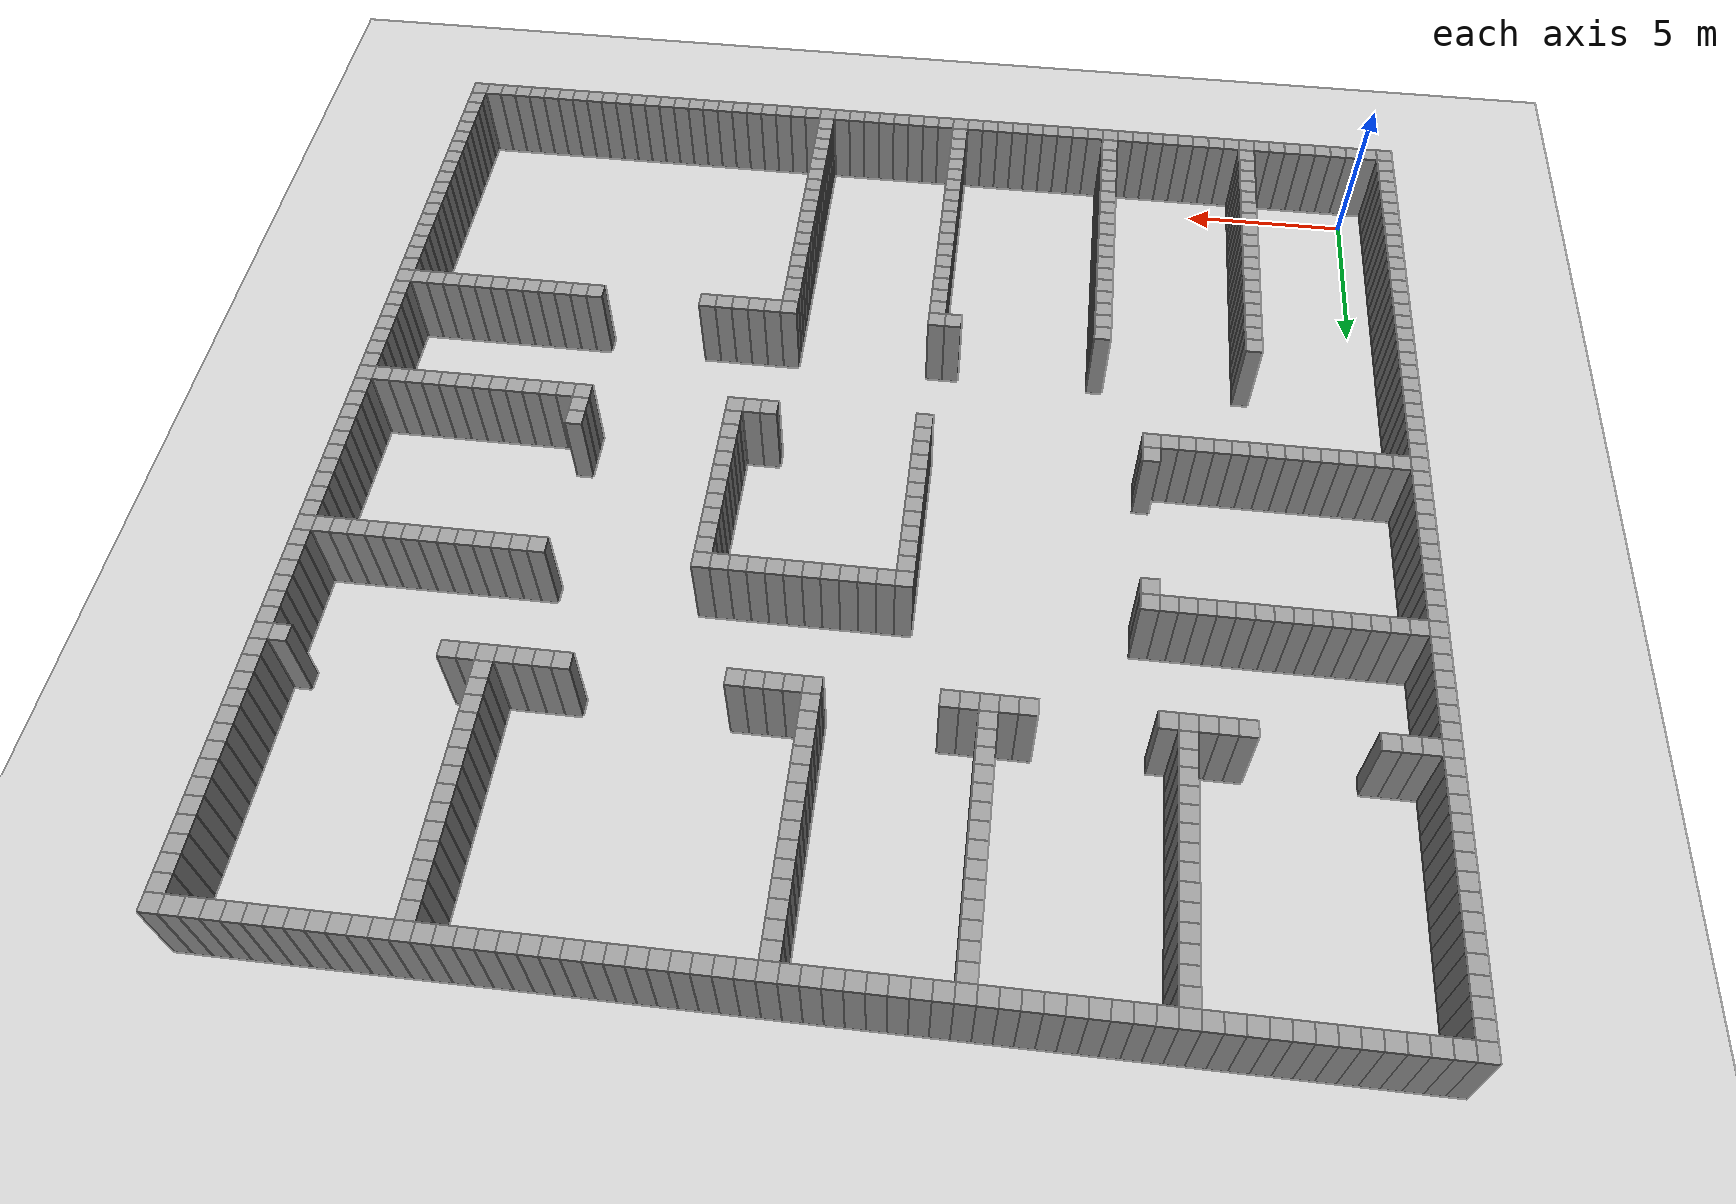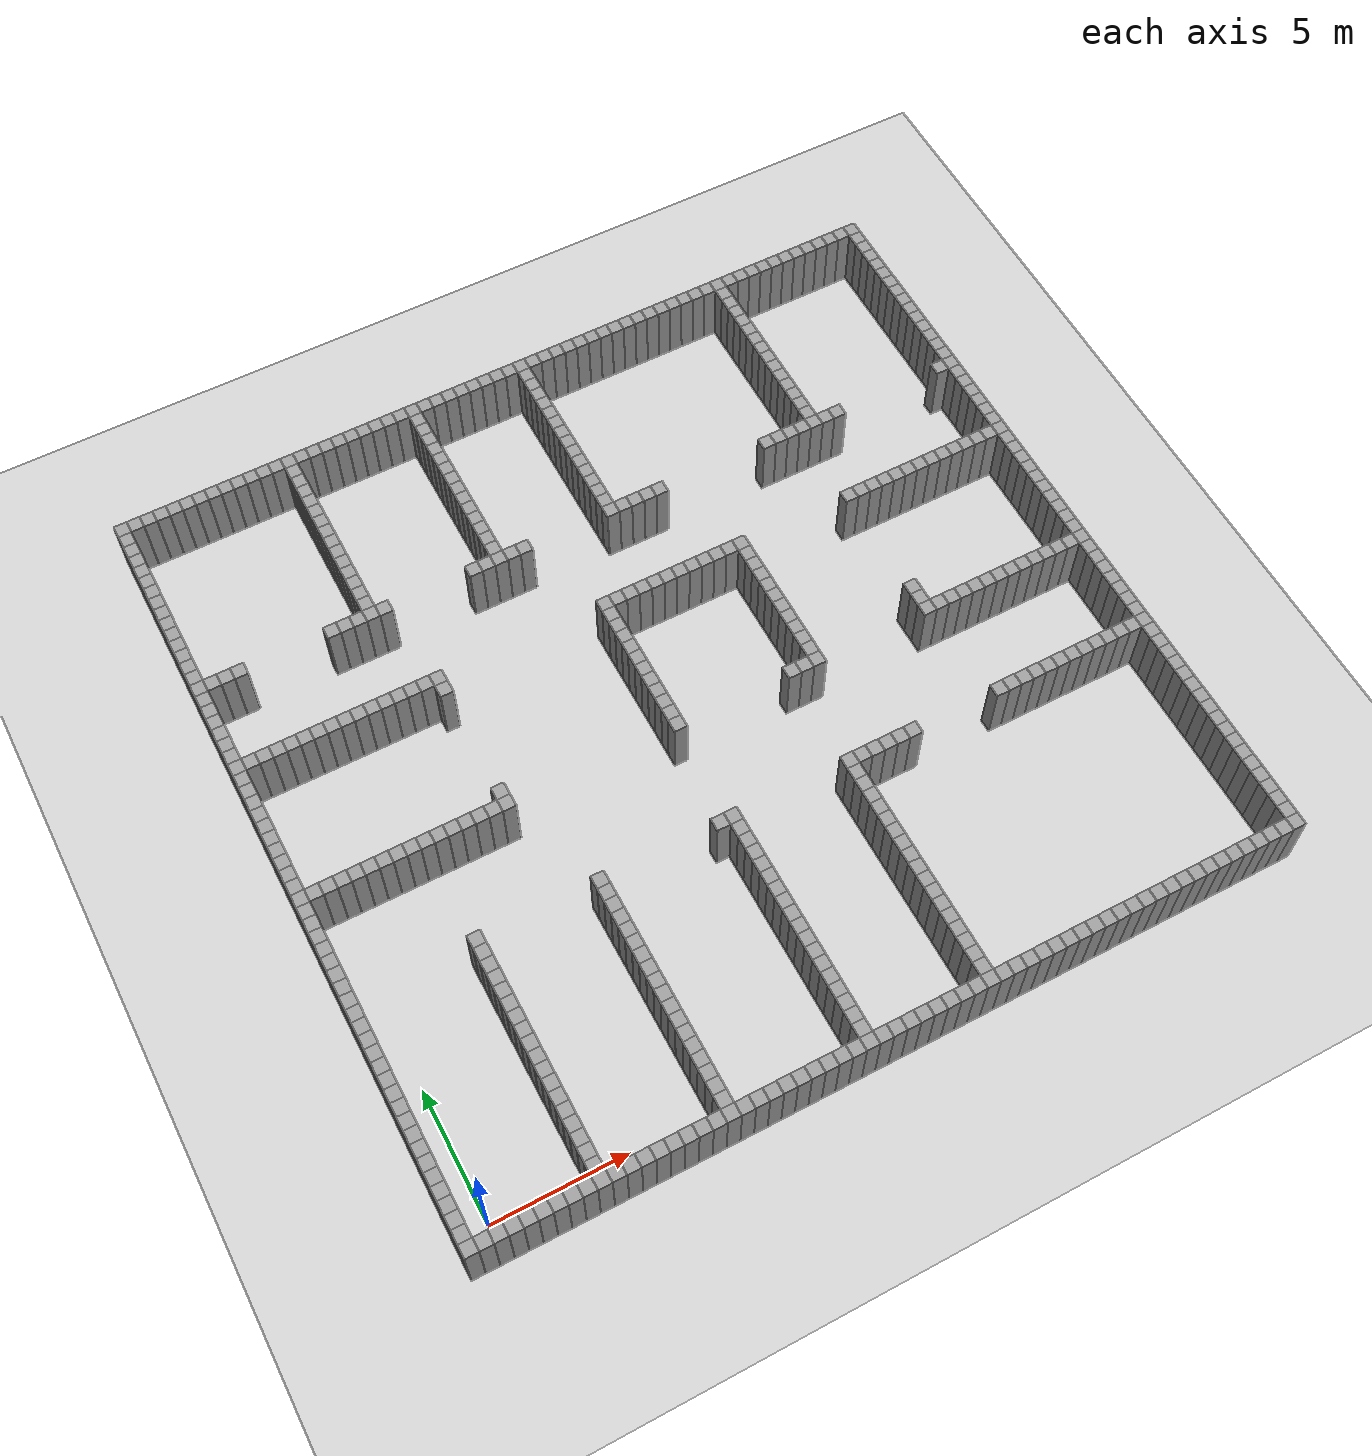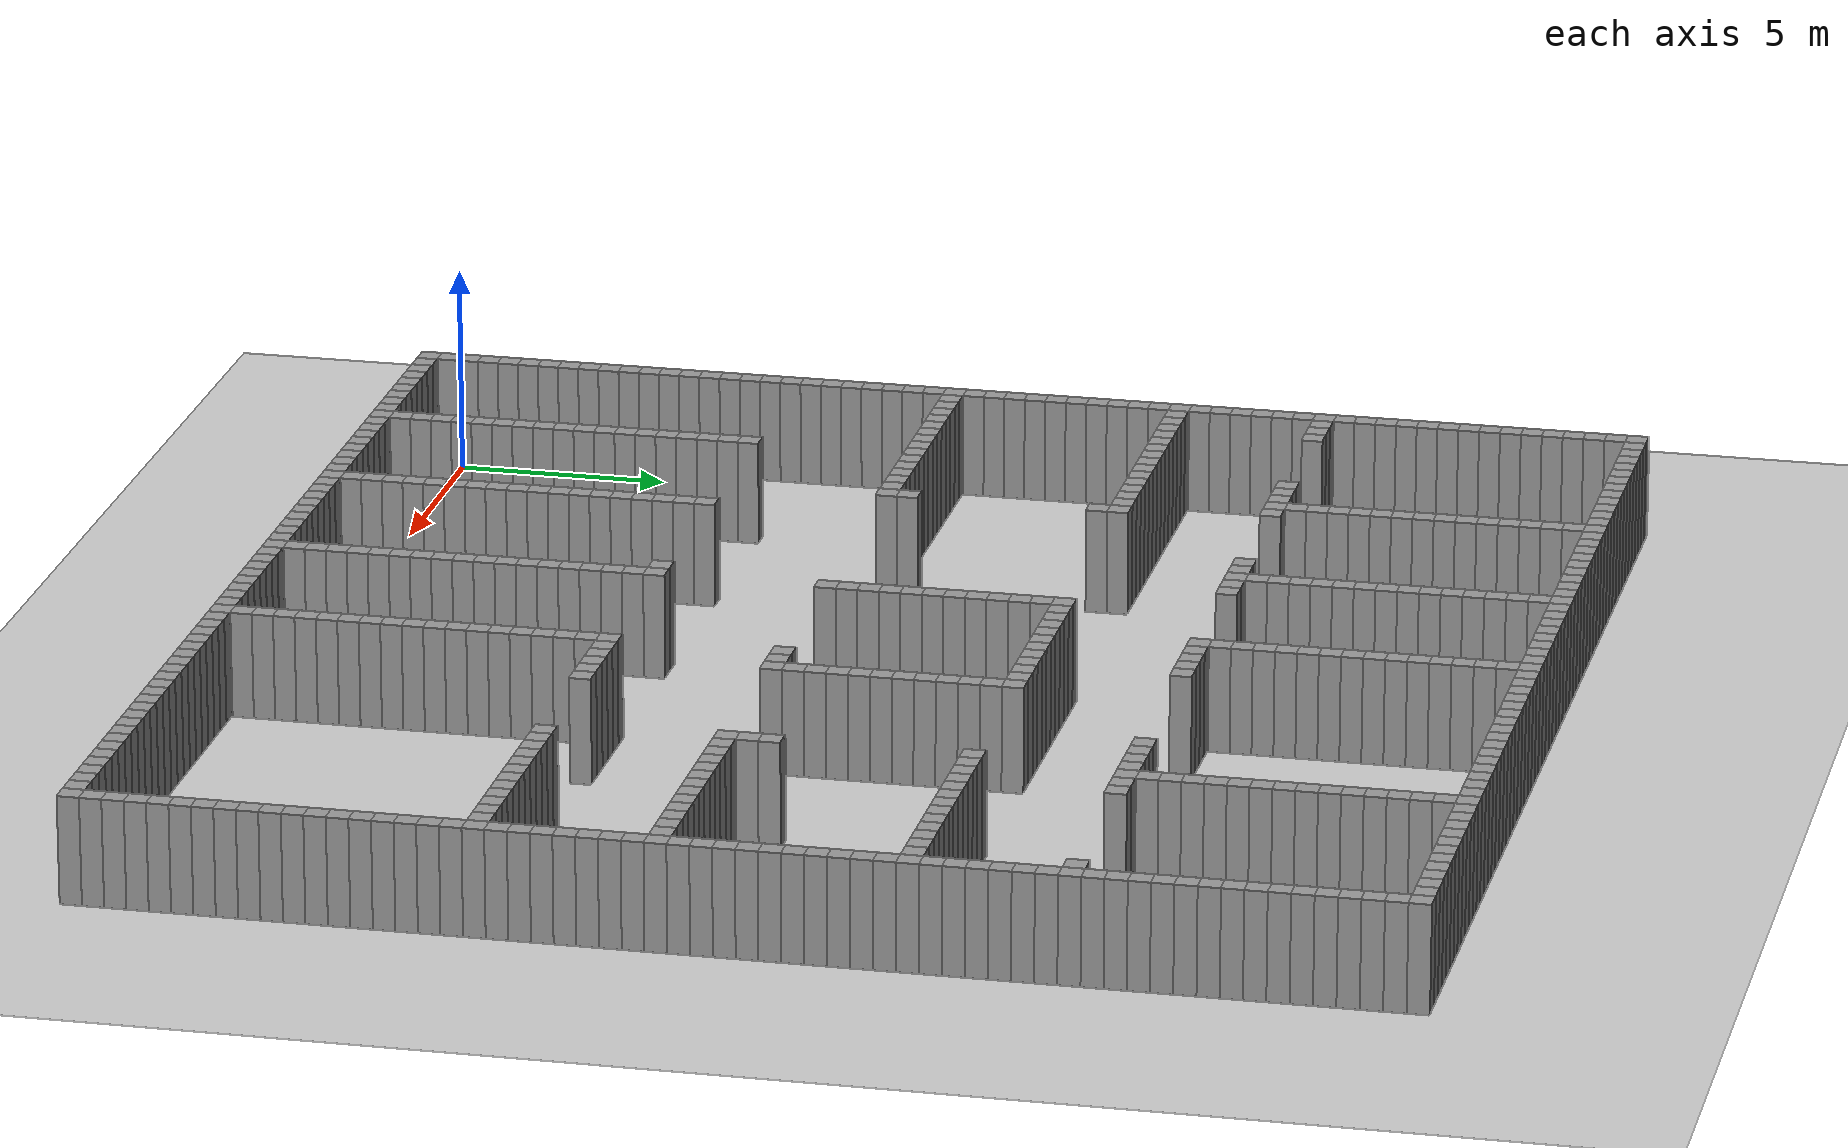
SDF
<sdf version="1.7">
 <world name="default">
  <light name="sun" type="directional">
   <pose>0 0 10 0 -0 0</pose>
   <diffuse>0.8 0.8 0.8 1</diffuse>
   <specular>0.2 0.2 0.2 1</specular>
   <attenuation>
    <range>1000</range>
    <constant>0.9</constant>
    <linear>0.01</linear>
    <quadratic>0.001</quadratic>
   </attenuation>
   <direction>-0.5 0.1 -0.9</direction>
   <spot><inner_angle>0</inner_angle><outer_angle>0</outer_angle><falloff>0</falloff></spot>
  </light>
  <model name="ground_plane">
   <static>1</static>
   <link name="link">
    <collision name="collision">
     <geometry><plane><normal>0 0 1</normal><size>100 100</size></plane></geometry>
     <surface>
      <contact><collide_bitmask>65535</collide_bitmask></contact>
      <friction><ode><mu>100</mu><mu2>50</mu2></ode></friction>
     </surface>
    </collision>
    <visual name="visual">
     <cast_shadows>0</cast_shadows>
     <geometry><plane><normal>0 0 1</normal><size>100 100</size></plane></geometry>
     <material>
      <script><uri>file://media/materials/scripts/gazebo.material</uri><name>Gazebo/Grey</name></script>
     </material>
    </visual>
   </link>
  </model>
  <gravity>0 0 -9.8</gravity>
  <magnetic_field>6e-06 2.3e-05 -4.2e-05</magnetic_field>
  <atmosphere type="adiabatic"/>
  <physics type="ode">
   <max_step_size>0.001</max_step_size>
   <real_time_factor>1</real_time_factor>
   <real_time_update_rate>1000</real_time_update_rate>
  </physics>
  <scene><ambient>0.4 0.4 0.4 1</ambient><background>0.7 0.7 0.7 1</background><shadows>1</shadows></scene>
  <spherical_coordinates>
   <surface_model>EARTH_WGS84</surface_model>
   <latitude_deg>0</latitude_deg>
   <longitude_deg>0</longitude_deg>
   <elevation>0</elevation>
   <heading_deg>0</heading_deg>
  </spherical_coordinates>
  <model name="image1">
   <pose>-0.980925 -1.04264 0 0 -0 0</pose>
   <link name="Wall_0">
    <collision name="Wall_0_Collision">
     <geometry><box><size>0.5 0.5 2.5</size></box></geometry>
     <pose>0 0 1.25 0 -0 0</pose>
    </collision>
    <visual name="Wall_0_Visual">
     <pose>0 0 1.25 0 -0 0</pose>
     <geometry><box><size>0.5 0.5 2.5</size></box></geometry>
     <material>
      <script><uri>file://media/materials/scripts/gazebo.material</uri><name>Gazebo/Grey</name></script>
      <ambient>1 1 1 1</ambient>
     </material>
     <meta><layer>0</layer></meta>
    </visual>
   </link>
   <link name="Wall_1">
    <collision name="Wall_1_Collision">
     <geometry><box><size>0.5 0.5 2.5</size></box></geometry>
     <pose>0 0 1.25 0 -0 0</pose>
    </collision>
    <visual name="Wall_1_Visual">
     <pose>0 0 1.25 0 -0 0</pose>
     <geometry><box><size>0.5 0.5 2.5</size></box></geometry>
     <material>
      <script><uri>file://media/materials/scripts/gazebo.material</uri><name>Gazebo/Grey</name></script>
      <ambient>1 1 1 1</ambient>
     </material>
     <meta><layer>0</layer></meta>
    </visual>
    <pose>0 0.5 0 0 -0 0</pose>
   </link>
   <link name="Wall_2">
    <collision name="Wall_2_Collision">
     <geometry><box><size>0.5 0.5 2.5</size></box></geometry>
     <pose>0 0 1.25 0 -0 0</pose>
    </collision>
    <visual name="Wall_2_Visual">
     <pose>0 0 1.25 0 -0 0</pose>
     <geometry><box><size>0.5 0.5 2.5</size></box></geometry>
     <material>
      <script><uri>file://media/materials/scripts/gazebo.material</uri><name>Gazebo/Grey</name></script>
      <ambient>1 1 1 1</ambient>
     </material>
     <meta><layer>0</layer></meta>
    </visual>
    <pose>0 1 0 0 -0 0</pose>
   </link>
   <link name="Wall_3">
    <collision name="Wall_3_Collision">
     <geometry><box><size>0.5 0.5 2.5</size></box></geometry>
     <pose>0 0 1.25 0 -0 0</pose>
    </collision>
    <visual name="Wall_3_Visual">
     <pose>0 0 1.25 0 -0 0</pose>
     <geometry><box><size>0.5 0.5 2.5</size></box></geometry>
     <material>
      <script><uri>file://media/materials/scripts/gazebo.material</uri><name>Gazebo/Grey</name></script>
      <ambient>1 1 1 1</ambient>
     </material>
     <meta><layer>0</layer></meta>
    </visual>
    <pose>0 1.5 0 0 -0 0</pose>
   </link>
   <link name="Wall_4">
    <collision name="Wall_4_Collision">
     <geometry><box><size>0.5 0.5 2.5</size></box></geometry>
     <pose>0 0 1.25 0 -0 0</pose>
    </collision>
    <visual name="Wall_4_Visual">
     <pose>0 0 1.25 0 -0 0</pose>
     <geometry><box><size>0.5 0.5 2.5</size></box></geometry>
     <material>
      <script><uri>file://media/materials/scripts/gazebo.material</uri><name>Gazebo/Grey</name></script>
      <ambient>1 1 1 1</ambient>
     </material>
     <meta><layer>0</layer></meta>
    </visual>
    <pose>0 2 0 0 -0 0</pose>
   </link>
   <link name="Wall_5">
    <collision name="Wall_5_Collision">
     <geometry><box><size>0.5 0.5 2.5</size></box></geometry>
     <pose>0 0 1.25 0 -0 0</pose>
    </collision>
    <visual name="Wall_5_Visual">
     <pose>0 0 1.25 0 -0 0</pose>
     <geometry><box><size>0.5 0.5 2.5</size></box></geometry>
     <material>
      <script><uri>file://media/materials/scripts/gazebo.material</uri><name>Gazebo/Grey</name></script>
      <ambient>1 1 1 1</ambient>
     </material>
     <meta><layer>0</layer></meta>
    </visual>
    <pose>0 2.5 0 0 -0 0</pose>
   </link>
   <link name="Wall_6">
    <collision name="Wall_6_Collision">
     <geometry><box><size>0.5 0.5 2.5</size></box></geometry>
     <pose>0 0 1.25 0 -0 0</pose>
    </collision>
    <visual name="Wall_6_Visual">
     <pose>0 0 1.25 0 -0 0</pose>
     <geometry><box><size>0.5 0.5 2.5</size></box></geometry>
     <material>
      <script><uri>file://media/materials/scripts/gazebo.material</uri><name>Gazebo/Grey</name></script>
      <ambient>1 1 1 1</ambient>
     </material>
     <meta><layer>0</layer></meta>
    </visual>
    <pose>0 3 0 0 -0 0</pose>
   </link>
   <link name="Wall_7">
    <collision name="Wall_7_Collision">
     <geometry><box><size>0.5 0.5 2.5</size></box></geometry>
     <pose>0 0 1.25 0 -0 0</pose>
    </collision>
    <visual name="Wall_7_Visual">
     <pose>0 0 1.25 0 -0 0</pose>
     <geometry><box><size>0.5 0.5 2.5</size></box></geometry>
     <material>
      <script><uri>file://media/materials/scripts/gazebo.material</uri><name>Gazebo/Grey</name></script>
      <ambient>1 1 1 1</ambient>
     </material>
     <meta><layer>0</layer></meta>
    </visual>
    <pose>0 3.5 0 0 -0 0</pose>
   </link>
   <link name="Wall_8">
    <collision name="Wall_8_Collision">
     <geometry><box><size>0.5 0.5 2.5</size></box></geometry>
     <pose>0 0 1.25 0 -0 0</pose>
    </collision>
    <visual name="Wall_8_Visual">
     <pose>0 0 1.25 0 -0 0</pose>
     <geometry><box><size>0.5 0.5 2.5</size></box></geometry>
     <material>
      <script><uri>file://media/materials/scripts/gazebo.material</uri><name>Gazebo/Grey</name></script>
      <ambient>1 1 1 1</ambient>
     </material>
     <meta><layer>0</layer></meta>
    </visual>
    <pose>0 4 0 0 -0 0</pose>
   </link>
   <link name="Wall_9">
    <collision name="Wall_9_Collision">
     <geometry><box><size>0.5 0.5 2.5</size></box></geometry>
     <pose>0 0 1.25 0 -0 0</pose>
    </collision>
    <visual name="Wall_9_Visual">
     <pose>0 0 1.25 0 -0 0</pose>
     <geometry><box><size>0.5 0.5 2.5</size></box></geometry>
     <material>
      <script><uri>file://media/materials/scripts/gazebo.material</uri><name>Gazebo/Grey</name></script>
      <ambient>1 1 1 1</ambient>
     </material>
     <meta><layer>0</layer></meta>
    </visual>
    <pose>0 4.5 0 0 -0 0</pose>
   </link>
   <link name="Wall_10">
    <collision name="Wall_10_Collision">
     <geometry><box><size>0.5 0.5 2.5</size></box></geometry>
     <pose>0 0 1.25 0 -0 0</pose>
    </collision>
    <visual name="Wall_10_Visual">
     <pose>0 0 1.25 0 -0 0</pose>
     <geometry><box><size>0.5 0.5 2.5</size></box></geometry>
     <material>
      <script><uri>file://media/materials/scripts/gazebo.material</uri><name>Gazebo/Grey</name></script>
      <ambient>1 1 1 1</ambient>
     </material>
     <meta><layer>0</layer></meta>
    </visual>
    <pose>0 5 0 0 -0 0</pose>
   </link>
   <link name="Wall_11">
    <collision name="Wall_11_Collision">
     <geometry><box><size>0.5 0.5 2.5</size></box></geometry>
     <pose>0 0 1.25 0 -0 0</pose>
    </collision>
    <visual name="Wall_11_Visual">
     <pose>0 0 1.25 0 -0 0</pose>
     <geometry><box><size>0.5 0.5 2.5</size></box></geometry>
     <material>
      <script><uri>file://media/materials/scripts/gazebo.material</uri><name>Gazebo/Grey</name></script>
      <ambient>1 1 1 1</ambient>
     </material>
     <meta><layer>0</layer></meta>
    </visual>
    <pose>0 5.5 0 0 -0 0</pose>
   </link>
   <link name="Wall_12">
    <collision name="Wall_12_Collision">
     <geometry><box><size>0.5 0.5 2.5</size></box></geometry>
     <pose>0 0 1.25 0 -0 0</pose>
    </collision>
    <visual name="Wall_12_Visual">
     <pose>0 0 1.25 0 -0 0</pose>
     <geometry><box><size>0.5 0.5 2.5</size></box></geometry>
     <material>
      <script><uri>file://media/materials/scripts/gazebo.material</uri><name>Gazebo/Grey</name></script>
      <ambient>1 1 1 1</ambient>
     </material>
     <meta><layer>0</layer></meta>
    </visual>
    <pose>0 6 0 0 -0 0</pose>
   </link>
   <link name="Wall_13">
    <collision name="Wall_13_Collision">
     <geometry><box><size>0.5 0.5 2.5</size></box></geometry>
     <pose>0 0 1.25 0 -0 0</pose>
    </collision>
    <visual name="Wall_13_Visual">
     <pose>0 0 1.25 0 -0 0</pose>
     <geometry><box><size>0.5 0.5 2.5</size></box></geometry>
     <material>
      <script><uri>file://media/materials/scripts/gazebo.material</uri><name>Gazebo/Grey</name></script>
      <ambient>1 1 1 1</ambient>
     </material>
     <meta><layer>0</layer></meta>
    </visual>
    <pose>0 6.5 0 0 -0 0</pose>
   </link>
   <link name="Wall_14">
    <collision name="Wall_14_Collision">
     <geometry><box><size>0.5 0.5 2.5</size></box></geometry>
     <pose>0 0 1.25 0 -0 0</pose>
    </collision>
    <visual name="Wall_14_Visual">
     <pose>0 0 1.25 0 -0 0</pose>
     <geometry><box><size>0.5 0.5 2.5</size></box></geometry>
     <material>
      <script><uri>file://media/materials/scripts/gazebo.material</uri><name>Gazebo/Grey</name></script>
      <ambient>1 1 1 1</ambient>
     </material>
     <meta><layer>0</layer></meta>
    </visual>
    <pose>0 7 0 0 -0 0</pose>
   </link>
   <link name="Wall_15">
    <collision name="Wall_15_Collision">
     <geometry><box><size>0.5 0.5 2.5</size></box></geometry>
     <pose>0 0 1.25 0 -0 0</pose>
    </collision>
    <visual name="Wall_15_Visual">
     <pose>0 0 1.25 0 -0 0</pose>
     <geometry><box><size>0.5 0.5 2.5</size></box></geometry>
     <material>
      <script><uri>file://media/materials/scripts/gazebo.material</uri><name>Gazebo/Grey</name></script>
      <ambient>1 1 1 1</ambient>
     </material>
     <meta><layer>0</layer></meta>
    </visual>
    <pose>0 7.5 0 0 -0 0</pose>
   </link>
   <link name="Wall_16">
    <collision name="Wall_16_Collision">
     <geometry><box><size>0.5 0.5 2.5</size></box></geometry>
     <pose>0 0 1.25 0 -0 0</pose>
    </collision>
    <visual name="Wall_16_Visual">
     <pose>0 0 1.25 0 -0 0</pose>
     <geometry><box><size>0.5 0.5 2.5</size></box></geometry>
     <material>
      <script><uri>file://media/materials/scripts/gazebo.material</uri><name>Gazebo/Grey</name></script>
      <ambient>1 1 1 1</ambient>
     </material>
     <meta><layer>0</layer></meta>
    </visual>
    <pose>0 8 0 0 -0 0</pose>
   </link>
   <link name="Wall_17">
    <collision name="Wall_17_Collision">
     <geometry><box><size>0.5 0.5 2.5</size></box></geometry>
     <pose>0 0 1.25 0 -0 0</pose>
    </collision>
    <visual name="Wall_17_Visual">
     <pose>0 0 1.25 0 -0 0</pose>
     <geometry><box><size>0.5 0.5 2.5</size></box></geometry>
     <material>
      <script><uri>file://media/materials/scripts/gazebo.material</uri><name>Gazebo/Grey</name></script>
      <ambient>1 1 1 1</ambient>
     </material>
     <meta><layer>0</layer></meta>
    </visual>
    <pose>0 8.5 0 0 -0 0</pose>
   </link>
   <link name="Wall_18">
    <collision name="Wall_18_Collision">
     <geometry><box><size>0.5 0.5 2.5</size></box></geometry>
     <pose>0 0 1.25 0 -0 0</pose>
    </collision>
    <visual name="Wall_18_Visual">
     <pose>0 0 1.25 0 -0 0</pose>
     <geometry><box><size>0.5 0.5 2.5</size></box></geometry>
     <material>
      <script><uri>file://media/materials/scripts/gazebo.material</uri><name>Gazebo/Grey</name></script>
      <ambient>1 1 1 1</ambient>
     </material>
     <meta><layer>0</layer></meta>
    </visual>
    <pose>0 9 0 0 -0 0</pose>
   </link>
   <link name="Wall_19">
    <collision name="Wall_19_Collision">
     <geometry><box><size>0.5 0.5 2.5</size></box></geometry>
     <pose>0 0 1.25 0 -0 0</pose>
    </collision>
    <visual name="Wall_19_Visual">
     <pose>0 0 1.25 0 -0 0</pose>
     <geometry><box><size>0.5 0.5 2.5</size></box></geometry>
     <material>
      <script><uri>file://media/materials/scripts/gazebo.material</uri><name>Gazebo/Grey</name></script>
      <ambient>1 1 1 1</ambient>
     </material>
     <meta><layer>0</layer></meta>
    </visual>
    <pose>0 9.5 0 0 -0 0</pose>
   </link>
   <link name="Wall_20">
    <collision name="Wall_20_Collision">
     <geometry><box><size>0.5 0.5 2.5</size></box></geometry>
     <pose>0 0 1.25 0 -0 0</pose>
    </collision>
    <visual name="Wall_20_Visual">
     <pose>0 0 1.25 0 -0 0</pose>
     <geometry><box><size>0.5 0.5 2.5</size></box></geometry>
     <material>
      <script><uri>file://media/materials/scripts/gazebo.material</uri><name>Gazebo/Grey</name></script>
      <ambient>1 1 1 1</ambient>
     </material>
     <meta><layer>0</layer></meta>
    </visual>
    <pose>0 10 0 0 -0 0</pose>
   </link>
   <link name="Wall_21">
    <collision name="Wall_21_Collision">
     <geometry><box><size>0.5 0.5 2.5</size></box></geometry>
     <pose>0 0 1.25 0 -0 0</pose>
    </collision>
    <visual name="Wall_21_Visual">
     <pose>0 0 1.25 0 -0 0</pose>
     <geometry><box><size>0.5 0.5 2.5</size></box></geometry>
     <material>
      <script><uri>file://media/materials/scripts/gazebo.material</uri><name>Gazebo/Grey</name></script>
      <ambient>1 1 1 1</ambient>
     </material>
     <meta><layer>0</layer></meta>
    </visual>
    <pose>0 10.5 0 0 -0 0</pose>
   </link>
   <link name="Wall_22">
    <collision name="Wall_22_Collision">
     <geometry><box><size>0.5 0.5 2.5</size></box></geometry>
     <pose>0 0 1.25 0 -0 0</pose>
    </collision>
    <visual name="Wall_22_Visual">
     <pose>0 0 1.25 0 -0 0</pose>
     <geometry><box><size>0.5 0.5 2.5</size></box></geometry>
     <material>
      <script><uri>file://media/materials/scripts/gazebo.material</uri><name>Gazebo/Grey</name></script>
      <ambient>1 1 1 1</ambient>
     </material>
     <meta><layer>0</layer></meta>
    </visual>
    <pose>0 11 0 0 -0 0</pose>
   </link>
   <link name="Wall_23">
    <collision name="Wall_23_Collision">
     <geometry><box><size>0.5 0.5 2.5</size></box></geometry>
     <pose>0 0 1.25 0 -0 0</pose>
    </collision>
    <visual name="Wall_23_Visual">
     <pose>0 0 1.25 0 -0 0</pose>
     <geometry><box><size>0.5 0.5 2.5</size></box></geometry>
     <material>
      <script><uri>file://media/materials/scripts/gazebo.material</uri><name>Gazebo/Grey</name></script>
      <ambient>1 1 1 1</ambient>
     </material>
     <meta><layer>0</layer></meta>
    </visual>
    <pose>0 11.5 0 0 -0 0</pose>
   </link>
   <link name="Wall_24">
    <collision name="Wall_24_Collision">
     <geometry><box><size>0.5 0.5 2.5</size></box></geometry>
     <pose>0 0 1.25 0 -0 0</pose>
    </collision>
    <visual name="Wall_24_Visual">
     <pose>0 0 1.25 0 -0 0</pose>
     <geometry><box><size>0.5 0.5 2.5</size></box></geometry>
     <material>
      <script><uri>file://media/materials/scripts/gazebo.material</uri><name>Gazebo/Grey</name></script>
      <ambient>1 1 1 1</ambient>
     </material>
     <meta><layer>0</layer></meta>
    </visual>
    <pose>0 12 0 0 -0 0</pose>
   </link>
   <link name="Wall_25">
    <collision name="Wall_25_Collision">
     <geometry><box><size>0.5 0.5 2.5</size></box></geometry>
     <pose>0 0 1.25 0 -0 0</pose>
    </collision>
    <visual name="Wall_25_Visual">
     <pose>0 0 1.25 0 -0 0</pose>
     <geometry><box><size>0.5 0.5 2.5</size></box></geometry>
     <material>
      <script><uri>file://media/materials/scripts/gazebo.material</uri><name>Gazebo/Grey</name></script>
      <ambient>1 1 1 1</ambient>
     </material>
     <meta><layer>0</layer></meta>
    </visual>
    <pose>0 12.5 0 0 -0 0</pose>
   </link>
   <link name="Wall_26">
    <collision name="Wall_26_Collision">
     <geometry><box><size>0.5 0.5 2.5</size></box></geometry>
     <pose>0 0 1.25 0 -0 0</pose>
    </collision>
    <visual name="Wall_26_Visual">
     <pose>0 0 1.25 0 -0 0</pose>
     <geometry><box><size>0.5 0.5 2.5</size></box></geometry>
     <material>
      <script><uri>file://media/materials/scripts/gazebo.material</uri><name>Gazebo/Grey</name></script>
      <ambient>1 1 1 1</ambient>
     </material>
     <meta><layer>0</layer></meta>
    </visual>
    <pose>0 13 0 0 -0 0</pose>
   </link>
   <link name="Wall_27">
    <collision name="Wall_27_Collision">
     <geometry><box><size>0.5 0.5 2.5</size></box></geometry>
     <pose>0 0 1.25 0 -0 0</pose>
    </collision>
    <visual name="Wall_27_Visual">
     <pose>0 0 1.25 0 -0 0</pose>
     <geometry><box><size>0.5 0.5 2.5</size></box></geometry>
     <material>
      <script><uri>file://media/materials/scripts/gazebo.material</uri><name>Gazebo/Grey</name></script>
      <ambient>1 1 1 1</ambient>
     </material>
     <meta><layer>0</layer></meta>
    </visual>
    <pose>0 13.5 0 0 -0 0</pose>
   </link>
   <link name="Wall_28">
    <collision name="Wall_28_Collision">
     <geometry><box><size>0.5 0.5 2.5</size></box></geometry>
     <pose>0 0 1.25 0 -0 0</pose>
    </collision>
    <visual name="Wall_28_Visual">
     <pose>0 0 1.25 0 -0 0</pose>
     <geometry><box><size>0.5 0.5 2.5</size></box></geometry>
     <material>
      <script><uri>file://media/materials/scripts/gazebo.material</uri><name>Gazebo/Grey</name></script>
      <ambient>1 1 1 1</ambient>
     </material>
     <meta><layer>0</layer></meta>
    </visual>
    <pose>0 14 0 0 -0 0</pose>
   </link>
   <link name="Wall_29">
    <collision name="Wall_29_Collision">
     <geometry><box><size>0.5 0.5 2.5</size></box></geometry>
     <pose>0 0 1.25 0 -0 0</pose>
    </collision>
    <visual name="Wall_29_Visual">
     <pose>0 0 1.25 0 -0 0</pose>
     <geometry><box><size>0.5 0.5 2.5</size></box></geometry>
     <material>
      <script><uri>file://media/materials/scripts/gazebo.material</uri><name>Gazebo/Grey</name></script>
      <ambient>1 1 1 1</ambient>
     </material>
     <meta><layer>0</layer></meta>
    </visual>
    <pose>0 14.5 0 0 -0 0</pose>
   </link>
   <link name="Wall_30">
    <collision name="Wall_30_Collision">
     <geometry><box><size>0.5 0.5 2.5</size></box></geometry>
     <pose>0 0 1.25 0 -0 0</pose>
    </collision>
    <visual name="Wall_30_Visual">
     <pose>0 0 1.25 0 -0 0</pose>
     <geometry><box><size>0.5 0.5 2.5</size></box></geometry>
     <material>
      <script><uri>file://media/materials/scripts/gazebo.material</uri><name>Gazebo/Grey</name></script>
      <ambient>1 1 1 1</ambient>
     </material>
     <meta><layer>0</layer></meta>
    </visual>
    <pose>0 15 0 0 -0 0</pose>
   </link>
   <link name="Wall_31">
    <collision name="Wall_31_Collision">
     <geometry><box><size>0.5 0.5 2.5</size></box></geometry>
     <pose>0 0 1.25 0 -0 0</pose>
    </collision>
    <visual name="Wall_31_Visual">
     <pose>0 0 1.25 0 -0 0</pose>
     <geometry><box><size>0.5 0.5 2.5</size></box></geometry>
     <material>
      <script><uri>file://media/materials/scripts/gazebo.material</uri><name>Gazebo/Grey</name></script>
      <ambient>1 1 1 1</ambient>
     </material>
     <meta><layer>0</layer></meta>
    </visual>
    <pose>0 15.5 0 0 -0 0</pose>
   </link>
   <link name="Wall_32">
    <collision name="Wall_32_Collision">
     <geometry><box><size>0.5 0.5 2.5</size></box></geometry>
     <pose>0 0 1.25 0 -0 0</pose>
    </collision>
    <visual name="Wall_32_Visual">
     <pose>0 0 1.25 0 -0 0</pose>
     <geometry><box><size>0.5 0.5 2.5</size></box></geometry>
     <material>
      <script><uri>file://media/materials/scripts/gazebo.material</uri><name>Gazebo/Grey</name></script>
      <ambient>1 1 1 1</ambient>
     </material>
     <meta><layer>0</layer></meta>
    </visual>
    <pose>0 16 0 0 -0 0</pose>
   </link>
   <link name="Wall_33">
    <collision name="Wall_33_Collision">
     <geometry><box><size>0.5 0.5 2.5</size></box></geometry>
     <pose>0 0 1.25 0 -0 0</pose>
    </collision>
    <visual name="Wall_33_Visual">
     <pose>0 0 1.25 0 -0 0</pose>
     <geometry><box><size>0.5 0.5 2.5</size></box></geometry>
     <material>
      <script><uri>file://media/materials/scripts/gazebo.material</uri><name>Gazebo/Grey</name></script>
      <ambient>1 1 1 1</ambient>
     </material>
     <meta><layer>0</layer></meta>
    </visual>
    <pose>0 16.5 0 0 -0 0</pose>
   </link>
   <link name="Wall_34">
    <collision name="Wall_34_Collision">
     <geometry><box><size>0.5 0.5 2.5</size></box></geometry>
     <pose>0 0 1.25 0 -0 0</pose>
    </collision>
    <visual name="Wall_34_Visual">
     <pose>0 0 1.25 0 -0 0</pose>
     <geometry><box><size>0.5 0.5 2.5</size></box></geometry>
     <material>
      <script><uri>file://media/materials/scripts/gazebo.material</uri><name>Gazebo/Grey</name></script>
      <ambient>1 1 1 1</ambient>
     </material>
     <meta><layer>0</layer></meta>
    </visual>
    <pose>0 17 0 0 -0 0</pose>
   </link>
   <link name="Wall_35">
    <collision name="Wall_35_Collision">
     <geometry><box><size>0.5 0.5 2.5</size></box></geometry>
     <pose>0 0 1.25 0 -0 0</pose>
    </collision>
    <visual name="Wall_35_Visual">
     <pose>0 0 1.25 0 -0 0</pose>
     <geometry><box><size>0.5 0.5 2.5</size></box></geometry>
     <material>
      <script><uri>file://media/materials/scripts/gazebo.material</uri><name>Gazebo/Grey</name></script>
      <ambient>1 1 1 1</ambient>
     </material>
     <meta><layer>0</layer></meta>
    </visual>
    <pose>0 17.5 0 0 -0 0</pose>
   </link>
   <link name="Wall_36">
    <collision name="Wall_36_Collision">
     <geometry><box><size>0.5 0.5 2.5</size></box></geometry>
     <pose>0 0 1.25 0 -0 0</pose>
    </collision>
    <visual name="Wall_36_Visual">
     <pose>0 0 1.25 0 -0 0</pose>
     <geometry><box><size>0.5 0.5 2.5</size></box></geometry>
     <material>
      <script><uri>file://media/materials/scripts/gazebo.material</uri><name>Gazebo/Grey</name></script>
      <ambient>1 1 1 1</ambient>
     </material>
     <meta><layer>0</layer></meta>
    </visual>
    <pose>0 18 0 0 -0 0</pose>
   </link>
   <link name="Wall_37">
    <collision name="Wall_37_Collision">
     <geometry><box><size>0.5 0.5 2.5</size></box></geometry>
     <pose>0 0 1.25 0 -0 0</pose>
    </collision>
    <visual name="Wall_37_Visual">
     <pose>0 0 1.25 0 -0 0</pose>
     <geometry><box><size>0.5 0.5 2.5</size></box></geometry>
     <material>
      <script><uri>file://media/materials/scripts/gazebo.material</uri><name>Gazebo/Grey</name></script>
      <ambient>1 1 1 1</ambient>
     </material>
     <meta><layer>0</layer></meta>
    </visual>
    <pose>0 18.5 0 0 -0 0</pose>
   </link>
   <link name="Wall_38">
    <collision name="Wall_38_Collision">
     <geometry><box><size>0.5 0.5 2.5</size></box></geometry>
     <pose>0 0 1.25 0 -0 0</pose>
    </collision>
    <visual name="Wall_38_Visual">
     <pose>0 0 1.25 0 -0 0</pose>
     <geometry><box><size>0.5 0.5 2.5</size></box></geometry>
     <material>
      <script><uri>file://media/materials/scripts/gazebo.material</uri><name>Gazebo/Grey</name></script>
      <ambient>1 1 1 1</ambient>
     </material>
     <meta><layer>0</layer></meta>
    </visual>
    <pose>0 19 0 0 -0 0</pose>
   </link>
   <link name="Wall_39">
    <collision name="Wall_39_Collision">
     <geometry><box><size>0.5 0.5 2.5</size></box></geometry>
     <pose>0 0 1.25 0 -0 0</pose>
    </collision>
    <visual name="Wall_39_Visual">
     <pose>0 0 1.25 0 -0 0</pose>
     <geometry><box><size>0.5 0.5 2.5</size></box></geometry>
     <material>
      <script><uri>file://media/materials/scripts/gazebo.material</uri><name>Gazebo/Grey</name></script>
      <ambient>1 1 1 1</ambient>
     </material>
     <meta><layer>0</layer></meta>
    </visual>
    <pose>0 19.5 0 0 -0 0</pose>
   </link>
   <link name="Wall_40">
    <collision name="Wall_40_Collision">
     <geometry><box><size>0.5 0.5 2.5</size></box></geometry>
     <pose>0 0 1.25 0 -0 0</pose>
    </collision>
    <visual name="Wall_40_Visual">
     <pose>0 0 1.25 0 -0 0</pose>
     <geometry><box><size>0.5 0.5 2.5</size></box></geometry>
     <material>
      <script><uri>file://media/materials/scripts/gazebo.material</uri><name>Gazebo/Grey</name></script>
      <ambient>1 1 1 1</ambient>
     </material>
     <meta><layer>0</layer></meta>
    </visual>
    <pose>0 20 0 0 -0 0</pose>
   </link>
   <link name="Wall_41">
    <collision name="Wall_41_Collision">
     <geometry><box><size>0.5 0.5 2.5</size></box></geometry>
     <pose>0 0 1.25 0 -0 0</pose>
    </collision>
    <visual name="Wall_41_Visual">
     <pose>0 0 1.25 0 -0 0</pose>
     <geometry><box><size>0.5 0.5 2.5</size></box></geometry>
     <material>
      <script><uri>file://media/materials/scripts/gazebo.material</uri><name>Gazebo/Grey</name></script>
      <ambient>1 1 1 1</ambient>
     </material>
     <meta><layer>0</layer></meta>
    </visual>
    <pose>0 20.5 0 0 -0 0</pose>
   </link>
   <link name="Wall_42">
    <collision name="Wall_42_Collision">
     <geometry><box><size>0.5 0.5 2.5</size></box></geometry>
     <pose>0 0 1.25 0 -0 0</pose>
    </collision>
    <visual name="Wall_42_Visual">
     <pose>0 0 1.25 0 -0 0</pose>
     <geometry><box><size>0.5 0.5 2.5</size></box></geometry>
     <material>
      <script><uri>file://media/materials/scripts/gazebo.material</uri><name>Gazebo/Grey</name></script>
      <ambient>1 1 1 1</ambient>
     </material>
     <meta><layer>0</layer></meta>
    </visual>
    <pose>0 21 0 0 -0 0</pose>
   </link>
   <link name="Wall_43">
    <collision name="Wall_43_Collision">
     <geometry><box><size>0.5 0.5 2.5</size></box></geometry>
     <pose>0 0 1.25 0 -0 0</pose>
    </collision>
    <visual name="Wall_43_Visual">
     <pose>0 0 1.25 0 -0 0</pose>
     <geometry><box><size>0.5 0.5 2.5</size></box></geometry>
     <material>
      <script><uri>file://media/materials/scripts/gazebo.material</uri><name>Gazebo/Grey</name></script>
      <ambient>1 1 1 1</ambient>
     </material>
     <meta><layer>0</layer></meta>
    </visual>
    <pose>0 21.5 0 0 -0 0</pose>
   </link>
   <link name="Wall_44">
    <collision name="Wall_44_Collision">
     <geometry><box><size>0.5 0.5 2.5</size></box></geometry>
     <pose>0 0 1.25 0 -0 0</pose>
    </collision>
    <visual name="Wall_44_Visual">
     <pose>0 0 1.25 0 -0 0</pose>
     <geometry><box><size>0.5 0.5 2.5</size></box></geometry>
     <material>
      <script><uri>file://media/materials/scripts/gazebo.material</uri><name>Gazebo/Grey</name></script>
      <ambient>1 1 1 1</ambient>
     </material>
     <meta><layer>0</layer></meta>
    </visual>
    <pose>0 22 0 0 -0 0</pose>
   </link>
   <link name="Wall_45">
    <collision name="Wall_45_Collision">
     <geometry><box><size>0.5 0.5 2.5</size></box></geometry>
     <pose>0 0 1.25 0 -0 0</pose>
    </collision>
    <visual name="Wall_45_Visual">
     <pose>0 0 1.25 0 -0 0</pose>
     <geometry><box><size>0.5 0.5 2.5</size></box></geometry>
     <material>
      <script><uri>file://media/materials/scripts/gazebo.material</uri><name>Gazebo/Grey</name></script>
      <ambient>1 1 1 1</ambient>
     </material>
     <meta><layer>0</layer></meta>
    </visual>
    <pose>0 22.5 0 0 -0 0</pose>
   </link>
   <link name="Wall_46">
    <collision name="Wall_46_Collision">
     <geometry><box><size>0.5 0.5 2.5</size></box></geometry>
     <pose>0 0 1.25 0 -0 0</pose>
    </collision>
    <visual name="Wall_46_Visual">
     <pose>0 0 1.25 0 -0 0</pose>
     <geometry><box><size>0.5 0.5 2.5</size></box></geometry>
     <material>
      <script><uri>file://media/materials/scripts/gazebo.material</uri><name>Gazebo/Grey</name></script>
      <ambient>1 1 1 1</ambient>
     </material>
     <meta><layer>0</layer></meta>
    </visual>
    <pose>0 23 0 0 -0 0</pose>
   </link>
   <link name="Wall_47">
    <collision name="Wall_47_Collision">
     <geometry><box><size>0.5 0.5 2.5</size></box></geometry>
     <pose>0 0 1.25 0 -0 0</pose>
    </collision>
    <visual name="Wall_47_Visual">
     <pose>0 0 1.25 0 -0 0</pose>
     <geometry><box><size>0.5 0.5 2.5</size></box></geometry>
     <material>
      <script><uri>file://media/materials/scripts/gazebo.material</uri><name>Gazebo/Grey</name></script>
      <ambient>1 1 1 1</ambient>
     </material>
     <meta><layer>0</layer></meta>
    </visual>
    <pose>0 23.5 0 0 -0 0</pose>
   </link>
   <link name="Wall_48">
    <collision name="Wall_48_Collision">
     <geometry><box><size>0.5 0.5 2.5</size></box></geometry>
     <pose>0 0 1.25 0 -0 0</pose>
    </collision>
    <visual name="Wall_48_Visual">
     <pose>0 0 1.25 0 -0 0</pose>
     <geometry><box><size>0.5 0.5 2.5</size></box></geometry>
     <material>
      <script><uri>file://media/materials/scripts/gazebo.material</uri><name>Gazebo/Grey</name></script>
      <ambient>1 1 1 1</ambient>
     </material>
     <meta><layer>0</layer></meta>
    </visual>
    <pose>0 24 0 0 -0 0</pose>
   </link>
   <link name="Wall_49">
    <collision name="Wall_49_Collision">
     <geometry><box><size>0.5 0.5 2.5</size></box></geometry>
     <pose>0 0 1.25 0 -0 0</pose>
    </collision>
    <visual name="Wall_49_Visual">
     <pose>0 0 1.25 0 -0 0</pose>
     <geometry><box><size>0.5 0.5 2.5</size></box></geometry>
     <material>
      <script><uri>file://media/materials/scripts/gazebo.material</uri><name>Gazebo/Grey</name></script>
      <ambient>1 1 1 1</ambient>
     </material>
     <meta><layer>0</layer></meta>
    </visual>
    <pose>0 24.5 0 0 -0 0</pose>
   </link>
   <link name="Wall_50">
    <collision name="Wall_50_Collision">
     <geometry><box><size>0.5 0.5 2.5</size></box></geometry>
     <pose>0 0 1.25 0 -0 0</pose>
    </collision>
    <visual name="Wall_50_Visual">
     <pose>0 0 1.25 0 -0 0</pose>
     <geometry><box><size>0.5 0.5 2.5</size></box></geometry>
     <material>
      <script><uri>file://media/materials/scripts/gazebo.material</uri><name>Gazebo/Grey</name></script>
      <ambient>1 1 1 1</ambient>
     </material>
     <meta><layer>0</layer></meta>
    </visual>
    <pose>0 25 0 0 -0 0</pose>
   </link>
   <link name="Wall_51">
    <collision name="Wall_51_Collision">
     <geometry><box><size>0.5 0.5 2.5</size></box></geometry>
     <pose>0 0 1.25 0 -0 0</pose>
    </collision>
    <visual name="Wall_51_Visual">
     <pose>0 0 1.25 0 -0 0</pose>
     <geometry><box><size>0.5 0.5 2.5</size></box></geometry>
     <material>
      <script><uri>file://media/materials/scripts/gazebo.material</uri><name>Gazebo/Grey</name></script>
      <ambient>1 1 1 1</ambient>
     </material>
     <meta><layer>0</layer></meta>
    </visual>
    <pose>0 25.5 0 0 -0 0</pose>
   </link>
   <link name="Wall_52">
    <collision name="Wall_52_Collision">
     <geometry><box><size>0.5 0.5 2.5</size></box></geometry>
     <pose>0 0 1.25 0 -0 0</pose>
    </collision>
    <visual name="Wall_52_Visual">
     <pose>0 0 1.25 0 -0 0</pose>
     <geometry><box><size>0.5 0.5 2.5</size></box></geometry>
     <material>
      <script><uri>file://media/materials/scripts/gazebo.material</uri><name>Gazebo/Grey</name></script>
      <ambient>1 1 1 1</ambient>
     </material>
     <meta><layer>0</layer></meta>
    </visual>
    <pose>0 26 0 0 -0 0</pose>
   </link>
   <link name="Wall_53">
    <collision name="Wall_53_Collision">
     <geometry><box><size>0.5 0.5 2.5</size></box></geometry>
     <pose>0 0 1.25 0 -0 0</pose>
    </collision>
    <visual name="Wall_53_Visual">
     <pose>0 0 1.25 0 -0 0</pose>
     <geometry><box><size>0.5 0.5 2.5</size></box></geometry>
     <material>
      <script><uri>file://media/materials/scripts/gazebo.material</uri><name>Gazebo/Grey</name></script>
      <ambient>1 1 1 1</ambient>
     </material>
     <meta><layer>0</layer></meta>
    </visual>
    <pose>0 26.5 0 0 -0 0</pose>
   </link>
   <link name="Wall_54">
    <collision name="Wall_54_Collision">
     <geometry><box><size>0.5 0.5 2.5</size></box></geometry>
     <pose>0 0 1.25 0 -0 0</pose>
    </collision>
    <visual name="Wall_54_Visual">
     <pose>0 0 1.25 0 -0 0</pose>
     <geometry><box><size>0.5 0.5 2.5</size></box></geometry>
     <material>
      <script><uri>file://media/materials/scripts/gazebo.material</uri><name>Gazebo/Grey</name></script>
      <ambient>1 1 1 1</ambient>
     </material>
     <meta><layer>0</layer></meta>
    </visual>
    <pose>0 27 0 0 -0 0</pose>
   </link>
   <link name="Wall_55">
    <collision name="Wall_55_Collision">
     <geometry><box><size>0.5 0.5 2.5</size></box></geometry>
     <pose>0 0 1.25 0 -0 0</pose>
    </collision>
    <visual name="Wall_55_Visual">
     <pose>0 0 1.25 0 -0 0</pose>
     <geometry><box><size>0.5 0.5 2.5</size></box></geometry>
     <material>
      <script><uri>file://media/materials/scripts/gazebo.material</uri><name>Gazebo/Grey</name></script>
      <ambient>1 1 1 1</ambient>
     </material>
     <meta><layer>0</layer></meta>
    </visual>
    <pose>0 27.5 0 0 -0 0</pose>
   </link>
   <link name="Wall_56">
    <collision name="Wall_56_Collision">
     <geometry><box><size>0.5 0.5 2.5</size></box></geometry>
     <pose>0 0 1.25 0 -0 0</pose>
    </collision>
    <visual name="Wall_56_Visual">
     <pose>0 0 1.25 0 -0 0</pose>
     <geometry><box><size>0.5 0.5 2.5</size></box></geometry>
     <material>
      <script><uri>file://media/materials/scripts/gazebo.material</uri><name>Gazebo/Grey</name></script>
      <ambient>1 1 1 1</ambient>
     </material>
     <meta><layer>0</layer></meta>
    </visual>
    <pose>0 28 0 0 -0 0</pose>
   </link>
   <link name="Wall_57">
    <collision name="Wall_57_Collision">
     <geometry><box><size>0.5 0.5 2.5</size></box></geometry>
     <pose>0 0 1.25 0 -0 0</pose>
    </collision>
    <visual name="Wall_57_Visual">
     <pose>0 0 1.25 0 -0 0</pose>
     <geometry><box><size>0.5 0.5 2.5</size></box></geometry>
     <material>
      <script><uri>file://media/materials/scripts/gazebo.material</uri><name>Gazebo/Grey</name></script>
      <ambient>1 1 1 1</ambient>
     </material>
     <meta><layer>0</layer></meta>
    </visual>
    <pose>0 28.5 0 0 -0 0</pose>
   </link>
   <link name="Wall_58">
    <collision name="Wall_58_Collision">
     <geometry><box><size>0.5 0.5 2.5</size></box></geometry>
     <pose>0 0 1.25 0 -0 0</pose>
    </collision>
    <visual name="Wall_58_Visual">
     <pose>0 0 1.25 0 -0 0</pose>
     <geometry><box><size>0.5 0.5 2.5</size></box></geometry>
     <material>
      <script><uri>file://media/materials/scripts/gazebo.material</uri><name>Gazebo/Grey</name></script>
      <ambient>1 1 1 1</ambient>
     </material>
     <meta><layer>0</layer></meta>
    </visual>
    <pose>0 29 0 0 -0 0</pose>
   </link>
   <link name="Wall_59">
    <collision name="Wall_59_Collision">
     <geometry><box><size>0.5 0.5 2.5</size></box></geometry>
     <pose>0 0 1.25 0 -0 0</pose>
    </collision>
    <visual name="Wall_59_Visual">
     <pose>0 0 1.25 0 -0 0</pose>
     <geometry><box><size>0.5 0.5 2.5</size></box></geometry>
     <material>
      <script><uri>file://media/materials/scripts/gazebo.material</uri><name>Gazebo/Grey</name></script>
      <ambient>1 1 1 1</ambient>
     </material>
     <meta><layer>0</layer></meta>
    </visual>
    <pose>0 29.5 0 0 -0 0</pose>
   </link>
   <link name="Wall_60">
    <collision name="Wall_60_Collision">
     <geometry><box><size>0.5 0.5 2.5</size></box></geometry>
     <pose>0 0 1.25 0 -0 0</pose>
    </collision>
    <visual name="Wall_60_Visual">
     <pose>0 0 1.25 0 -0 0</pose>
     <geometry><box><size>0.5 0.5 2.5</size></box></geometry>
     <material>
      <script><uri>file://media/materials/scripts/gazebo.material</uri><name>Gazebo/Grey</name></script>
      <ambient>1 1 1 1</ambient>
     </material>
     <meta><layer>0</layer></meta>
    </visual>
    <pose>0.5 0 0 0 -0 0</pose>
   </link>
   <link name="Wall_61">
    <collision name="Wall_61_Collision">
     <geometry><box><size>0.5 0.5 2.5</size></box></geometry>
     <pose>0 0 1.25 0 -0 0</pose>
    </collision>
    <visual name="Wall_61_Visual">
     <pose>0 0 1.25 0 -0 0</pose>
     <geometry><box><size>0.5 0.5 2.5</size></box></geometry>
     <material>
      <script><uri>file://media/materials/scripts/gazebo.material</uri><name>Gazebo/Grey</name></script>
      <ambient>1 1 1 1</ambient>
     </material>
     <meta><layer>0</layer></meta>
    </visual>
    <pose>0.5 13 0 0 -0 0</pose>
   </link>
   <link name="Wall_62">
    <collision name="Wall_62_Collision">
     <geometry><box><size>0.5 0.5 2.5</size></box></geometry>
     <pose>0 0 1.25 0 -0 0</pose>
    </collision>
    <visual name="Wall_62_Visual">
     <pose>0 0 1.25 0 -0 0</pose>
     <geometry><box><size>0.5 0.5 2.5</size></box></geometry>
     <material>
      <script><uri>file://media/materials/scripts/gazebo.material</uri><name>Gazebo/Grey</name></script>
      <ambient>1 1 1 1</ambient>
     </material>
     <meta><layer>0</layer></meta>
    </visual>
    <pose>0.5 18.5 0 0 -0 0</pose>
   </link>
   <link name="Wall_63">
    <collision name="Wall_63_Collision">
     <geometry><box><size>0.5 0.5 2.5</size></box></geometry>
     <pose>0 0 1.25 0 -0 0</pose>
    </collision>
    <visual name="Wall_63_Visual">
     <pose>0 0 1.25 0 -0 0</pose>
     <geometry><box><size>0.5 0.5 2.5</size></box></geometry>
     <material>
      <script><uri>file://media/materials/scripts/gazebo.material</uri><name>Gazebo/Grey</name></script>
      <ambient>1 1 1 1</ambient>
     </material>
     <meta><layer>0</layer></meta>
    </visual>
    <pose>0.5 22 0 0 -0 0</pose>
   </link>
   <link name="Wall_64">
    <collision name="Wall_64_Collision">
     <geometry><box><size>0.5 0.5 2.5</size></box></geometry>
     <pose>0 0 1.25 0 -0 0</pose>
    </collision>
    <visual name="Wall_64_Visual">
     <pose>0 0 1.25 0 -0 0</pose>
     <geometry><box><size>0.5 0.5 2.5</size></box></geometry>
     <material>
      <script><uri>file://media/materials/scripts/gazebo.material</uri><name>Gazebo/Grey</name></script>
      <ambient>1 1 1 1</ambient>
     </material>
     <meta><layer>0</layer></meta>
    </visual>
    <pose>0.5 29.5 0 0 -0 0</pose>
   </link>
   <link name="Wall_65">
    <collision name="Wall_65_Collision">
     <geometry><box><size>0.5 0.5 2.5</size></box></geometry>
     <pose>0 0 1.25 0 -0 0</pose>
    </collision>
    <visual name="Wall_65_Visual">
     <pose>0 0 1.25 0 -0 0</pose>
     <geometry><box><size>0.5 0.5 2.5</size></box></geometry>
     <material>
      <script><uri>file://media/materials/scripts/gazebo.material</uri><name>Gazebo/Grey</name></script>
      <ambient>1 1 1 1</ambient>
     </material>
     <meta><layer>0</layer></meta>
    </visual>
    <pose>1 0 0 0 -0 0</pose>
   </link>
   <link name="Wall_66">
    <collision name="Wall_66_Collision">
     <geometry><box><size>0.5 0.5 2.5</size></box></geometry>
     <pose>0 0 1.25 0 -0 0</pose>
    </collision>
    <visual name="Wall_66_Visual">
     <pose>0 0 1.25 0 -0 0</pose>
     <geometry><box><size>0.5 0.5 2.5</size></box></geometry>
     <material>
      <script><uri>file://media/materials/scripts/gazebo.material</uri><name>Gazebo/Grey</name></script>
      <ambient>1 1 1 1</ambient>
     </material>
     <meta><layer>0</layer></meta>
    </visual>
    <pose>1 13 0 0 -0 0</pose>
   </link>
   <link name="Wall_67">
    <collision name="Wall_67_Collision">
     <geometry><box><size>0.5 0.5 2.5</size></box></geometry>
     <pose>0 0 1.25 0 -0 0</pose>
    </collision>
    <visual name="Wall_67_Visual">
     <pose>0 0 1.25 0 -0 0</pose>
     <geometry><box><size>0.5 0.5 2.5</size></box></geometry>
     <material>
      <script><uri>file://media/materials/scripts/gazebo.material</uri><name>Gazebo/Grey</name></script>
      <ambient>1 1 1 1</ambient>
     </material>
     <meta><layer>0</layer></meta>
    </visual>
    <pose>1 18.5 0 0 -0 0</pose>
   </link>
   <link name="Wall_68">
    <collision name="Wall_68_Collision">
     <geometry><box><size>0.5 0.5 2.5</size></box></geometry>
     <pose>0 0 1.25 0 -0 0</pose>
    </collision>
    <visual name="Wall_68_Visual">
     <pose>0 0 1.25 0 -0 0</pose>
     <geometry><box><size>0.5 0.5 2.5</size></box></geometry>
     <material>
      <script><uri>file://media/materials/scripts/gazebo.material</uri><name>Gazebo/Grey</name></script>
      <ambient>1 1 1 1</ambient>
     </material>
     <meta><layer>0</layer></meta>
    </visual>
    <pose>1 22 0 0 -0 0</pose>
   </link>
   <link name="Wall_69">
    <collision name="Wall_69_Collision">
     <geometry><box><size>0.5 0.5 2.5</size></box></geometry>
     <pose>0 0 1.25 0 -0 0</pose>
    </collision>
    <visual name="Wall_69_Visual">
     <pose>0 0 1.25 0 -0 0</pose>
     <geometry><box><size>0.5 0.5 2.5</size></box></geometry>
     <material>
      <script><uri>file://media/materials/scripts/gazebo.material</uri><name>Gazebo/Grey</name></script>
      <ambient>1 1 1 1</ambient>
     </material>
     <meta><layer>0</layer></meta>
    </visual>
    <pose>1 29.5 0 0 -0 0</pose>
   </link>
   <link name="Wall_70">
    <collision name="Wall_70_Collision">
     <geometry><box><size>0.5 0.5 2.5</size></box></geometry>
     <pose>0 0 1.25 0 -0 0</pose>
    </collision>
    <visual name="Wall_70_Visual">
     <pose>0 0 1.25 0 -0 0</pose>
     <geometry><box><size>0.5 0.5 2.5</size></box></geometry>
     <material>
      <script><uri>file://media/materials/scripts/gazebo.material</uri><name>Gazebo/Grey</name></script>
      <ambient>1 1 1 1</ambient>
     </material>
     <meta><layer>0</layer></meta>
    </visual>
    <pose>1.5 0 0 0 -0 0</pose>
   </link>
   <link name="Wall_71">
    <collision name="Wall_71_Collision">
     <geometry><box><size>0.5 0.5 2.5</size></box></geometry>
     <pose>0 0 1.25 0 -0 0</pose>
    </collision>
    <visual name="Wall_71_Visual">
     <pose>0 0 1.25 0 -0 0</pose>
     <geometry><box><size>0.5 0.5 2.5</size></box></geometry>
     <material>
      <script><uri>file://media/materials/scripts/gazebo.material</uri><name>Gazebo/Grey</name></script>
      <ambient>1 1 1 1</ambient>
     </material>
     <meta><layer>0</layer></meta>
    </visual>
    <pose>1.5 13 0 0 -0 0</pose>
   </link>
   <link name="Wall_72">
    <collision name="Wall_72_Collision">
     <geometry><box><size>0.5 0.5 2.5</size></box></geometry>
     <pose>0 0 1.25 0 -0 0</pose>
    </collision>
    <visual name="Wall_72_Visual">
     <pose>0 0 1.25 0 -0 0</pose>
     <geometry><box><size>0.5 0.5 2.5</size></box></geometry>
     <material>
      <script><uri>file://media/materials/scripts/gazebo.material</uri><name>Gazebo/Grey</name></script>
      <ambient>1 1 1 1</ambient>
     </material>
     <meta><layer>0</layer></meta>
    </visual>
    <pose>1.5 18.5 0 0 -0 0</pose>
   </link>
   <link name="Wall_73">
    <collision name="Wall_73_Collision">
     <geometry><box><size>0.5 0.5 2.5</size></box></geometry>
     <pose>0 0 1.25 0 -0 0</pose>
    </collision>
    <visual name="Wall_73_Visual">
     <pose>0 0 1.25 0 -0 0</pose>
     <geometry><box><size>0.5 0.5 2.5</size></box></geometry>
     <material>
      <script><uri>file://media/materials/scripts/gazebo.material</uri><name>Gazebo/Grey</name></script>
      <ambient>1 1 1 1</ambient>
     </material>
     <meta><layer>0</layer></meta>
    </visual>
    <pose>1.5 22 0 0 -0 0</pose>
   </link>
   <link name="Wall_74">
    <collision name="Wall_74_Collision">
     <geometry><box><size>0.5 0.5 2.5</size></box></geometry>
     <pose>0 0 1.25 0 -0 0</pose>
    </collision>
    <visual name="Wall_74_Visual">
     <pose>0 0 1.25 0 -0 0</pose>
     <geometry><box><size>0.5 0.5 2.5</size></box></geometry>
     <material>
      <script><uri>file://media/materials/scripts/gazebo.material</uri><name>Gazebo/Grey</name></script>
      <ambient>1 1 1 1</ambient>
     </material>
     <meta><layer>0</layer></meta>
    </visual>
    <pose>1.5 29.5 0 0 -0 0</pose>
   </link>
   <link name="Wall_75">
    <collision name="Wall_75_Collision">
     <geometry><box><size>0.5 0.5 2.5</size></box></geometry>
     <pose>0 0 1.25 0 -0 0</pose>
    </collision>
    <visual name="Wall_75_Visual">
     <pose>0 0 1.25 0 -0 0</pose>
     <geometry><box><size>0.5 0.5 2.5</size></box></geometry>
     <material>
      <script><uri>file://media/materials/scripts/gazebo.material</uri><name>Gazebo/Grey</name></script>
      <ambient>1 1 1 1</ambient>
     </material>
     <meta><layer>0</layer></meta>
    </visual>
    <pose>2 0 0 0 -0 0</pose>
   </link>
   <link name="Wall_76">
    <collision name="Wall_76_Collision">
     <geometry><box><size>0.5 0.5 2.5</size></box></geometry>
     <pose>0 0 1.25 0 -0 0</pose>
    </collision>
    <visual name="Wall_76_Visual">
     <pose>0 0 1.25 0 -0 0</pose>
     <geometry><box><size>0.5 0.5 2.5</size></box></geometry>
     <material>
      <script><uri>file://media/materials/scripts/gazebo.material</uri><name>Gazebo/Grey</name></script>
      <ambient>1 1 1 1</ambient>
     </material>
     <meta><layer>0</layer></meta>
    </visual>
    <pose>2 13 0 0 -0 0</pose>
   </link>
   <link name="Wall_77">
    <collision name="Wall_77_Collision">
     <geometry><box><size>0.5 0.5 2.5</size></box></geometry>
     <pose>0 0 1.25 0 -0 0</pose>
    </collision>
    <visual name="Wall_77_Visual">
     <pose>0 0 1.25 0 -0 0</pose>
     <geometry><box><size>0.5 0.5 2.5</size></box></geometry>
     <material>
      <script><uri>file://media/materials/scripts/gazebo.material</uri><name>Gazebo/Grey</name></script>
      <ambient>1 1 1 1</ambient>
     </material>
     <meta><layer>0</layer></meta>
    </visual>
    <pose>2 18.5 0 0 -0 0</pose>
   </link>
   <link name="Wall_78">
    <collision name="Wall_78_Collision">
     <geometry><box><size>0.5 0.5 2.5</size></box></geometry>
     <pose>0 0 1.25 0 -0 0</pose>
    </collision>
    <visual name="Wall_78_Visual">
     <pose>0 0 1.25 0 -0 0</pose>
     <geometry><box><size>0.5 0.5 2.5</size></box></geometry>
     <material>
      <script><uri>file://media/materials/scripts/gazebo.material</uri><name>Gazebo/Grey</name></script>
      <ambient>1 1 1 1</ambient>
     </material>
     <meta><layer>0</layer></meta>
    </visual>
    <pose>2 29.5 0 0 -0 0</pose>
   </link>
   <link name="Wall_79">
    <collision name="Wall_79_Collision">
     <geometry><box><size>0.5 0.5 2.5</size></box></geometry>
     <pose>0 0 1.25 0 -0 0</pose>
    </collision>
    <visual name="Wall_79_Visual">
     <pose>0 0 1.25 0 -0 0</pose>
     <geometry><box><size>0.5 0.5 2.5</size></box></geometry>
     <material>
      <script><uri>file://media/materials/scripts/gazebo.material</uri><name>Gazebo/Grey</name></script>
      <ambient>1 1 1 1</ambient>
     </material>
     <meta><layer>0</layer></meta>
    </visual>
    <pose>2.5 0 0 0 -0 0</pose>
   </link>
   <link name="Wall_80">
    <collision name="Wall_80_Collision">
     <geometry><box><size>0.5 0.5 2.5</size></box></geometry>
     <pose>0 0 1.25 0 -0 0</pose>
    </collision>
    <visual name="Wall_80_Visual">
     <pose>0 0 1.25 0 -0 0</pose>
     <geometry><box><size>0.5 0.5 2.5</size></box></geometry>
     <material>
      <script><uri>file://media/materials/scripts/gazebo.material</uri><name>Gazebo/Grey</name></script>
      <ambient>1 1 1 1</ambient>
     </material>
     <meta><layer>0</layer></meta>
    </visual>
    <pose>2.5 13 0 0 -0 0</pose>
   </link>
   <link name="Wall_81">
    <collision name="Wall_81_Collision">
     <geometry><box><size>0.5 0.5 2.5</size></box></geometry>
     <pose>0 0 1.25 0 -0 0</pose>
    </collision>
    <visual name="Wall_81_Visual">
     <pose>0 0 1.25 0 -0 0</pose>
     <geometry><box><size>0.5 0.5 2.5</size></box></geometry>
     <material>
      <script><uri>file://media/materials/scripts/gazebo.material</uri><name>Gazebo/Grey</name></script>
      <ambient>1 1 1 1</ambient>
     </material>
     <meta><layer>0</layer></meta>
    </visual>
    <pose>2.5 18.5 0 0 -0 0</pose>
   </link>
   <link name="Wall_82">
    <collision name="Wall_82_Collision">
     <geometry><box><size>0.5 0.5 2.5</size></box></geometry>
     <pose>0 0 1.25 0 -0 0</pose>
    </collision>
    <visual name="Wall_82_Visual">
     <pose>0 0 1.25 0 -0 0</pose>
     <geometry><box><size>0.5 0.5 2.5</size></box></geometry>
     <material>
      <script><uri>file://media/materials/scripts/gazebo.material</uri><name>Gazebo/Grey</name></script>
      <ambient>1 1 1 1</ambient>
     </material>
     <meta><layer>0</layer></meta>
    </visual>
    <pose>2.5 29.5 0 0 -0 0</pose>
   </link>
   <link name="Wall_83">
    <collision name="Wall_83_Collision">
     <geometry><box><size>0.5 0.5 2.5</size></box></geometry>
     <pose>0 0 1.25 0 -0 0</pose>
    </collision>
    <visual name="Wall_83_Visual">
     <pose>0 0 1.25 0 -0 0</pose>
     <geometry><box><size>0.5 0.5 2.5</size></box></geometry>
     <material>
      <script><uri>file://media/materials/scripts/gazebo.material</uri><name>Gazebo/Grey</name></script>
      <ambient>1 1 1 1</ambient>
     </material>
     <meta><layer>0</layer></meta>
    </visual>
    <pose>3 0 0 0 -0 0</pose>
   </link>
   <link name="Wall_84">
    <collision name="Wall_84_Collision">
     <geometry><box><size>0.5 0.5 2.5</size></box></geometry>
     <pose>0 0 1.25 0 -0 0</pose>
    </collision>
    <visual name="Wall_84_Visual">
     <pose>0 0 1.25 0 -0 0</pose>
     <geometry><box><size>0.5 0.5 2.5</size></box></geometry>
     <material>
      <script><uri>file://media/materials/scripts/gazebo.material</uri><name>Gazebo/Grey</name></script>
      <ambient>1 1 1 1</ambient>
     </material>
     <meta><layer>0</layer></meta>
    </visual>
    <pose>3 13 0 0 -0 0</pose>
   </link>
   <link name="Wall_85">
    <collision name="Wall_85_Collision">
     <geometry><box><size>0.5 0.5 2.5</size></box></geometry>
     <pose>0 0 1.25 0 -0 0</pose>
    </collision>
    <visual name="Wall_85_Visual">
     <pose>0 0 1.25 0 -0 0</pose>
     <geometry><box><size>0.5 0.5 2.5</size></box></geometry>
     <material>
      <script><uri>file://media/materials/scripts/gazebo.material</uri><name>Gazebo/Grey</name></script>
      <ambient>1 1 1 1</ambient>
     </material>
     <meta><layer>0</layer></meta>
    </visual>
    <pose>3 18.5 0 0 -0 0</pose>
   </link>
   <link name="Wall_86">
    <collision name="Wall_86_Collision">
     <geometry><box><size>0.5 0.5 2.5</size></box></geometry>
     <pose>0 0 1.25 0 -0 0</pose>
    </collision>
    <visual name="Wall_86_Visual">
     <pose>0 0 1.25 0 -0 0</pose>
     <geometry><box><size>0.5 0.5 2.5</size></box></geometry>
     <material>
      <script><uri>file://media/materials/scripts/gazebo.material</uri><name>Gazebo/Grey</name></script>
      <ambient>1 1 1 1</ambient>
     </material>
     <meta><layer>0</layer></meta>
    </visual>
    <pose>3 29.5 0 0 -0 0</pose>
   </link>
   <link name="Wall_87">
    <collision name="Wall_87_Collision">
     <geometry><box><size>0.5 0.5 2.5</size></box></geometry>
     <pose>0 0 1.25 0 -0 0</pose>
    </collision>
    <visual name="Wall_87_Visual">
     <pose>0 0 1.25 0 -0 0</pose>
     <geometry><box><size>0.5 0.5 2.5</size></box></geometry>
     <material>
      <script><uri>file://media/materials/scripts/gazebo.material</uri><name>Gazebo/Grey</name></script>
      <ambient>1 1 1 1</ambient>
     </material>
     <meta><layer>0</layer></meta>
    </visual>
    <pose>3.5 0 0 0 -0 0</pose>
   </link>
   <link name="Wall_88">
    <collision name="Wall_88_Collision">
     <geometry><box><size>0.5 0.5 2.5</size></box></geometry>
     <pose>0 0 1.25 0 -0 0</pose>
    </collision>
    <visual name="Wall_88_Visual">
     <pose>0 0 1.25 0 -0 0</pose>
     <geometry><box><size>0.5 0.5 2.5</size></box></geometry>
     <material>
      <script><uri>file://media/materials/scripts/gazebo.material</uri><name>Gazebo/Grey</name></script>
      <ambient>1 1 1 1</ambient>
     </material>
     <meta><layer>0</layer></meta>
    </visual>
    <pose>3.5 13 0 0 -0 0</pose>
   </link>
   <link name="Wall_89">
    <collision name="Wall_89_Collision">
     <geometry><box><size>0.5 0.5 2.5</size></box></geometry>
     <pose>0 0 1.25 0 -0 0</pose>
    </collision>
    <visual name="Wall_89_Visual">
     <pose>0 0 1.25 0 -0 0</pose>
     <geometry><box><size>0.5 0.5 2.5</size></box></geometry>
     <material>
      <script><uri>file://media/materials/scripts/gazebo.material</uri><name>Gazebo/Grey</name></script>
      <ambient>1 1 1 1</ambient>
     </material>
     <meta><layer>0</layer></meta>
    </visual>
    <pose>3.5 18.5 0 0 -0 0</pose>
   </link>
   <link name="Wall_90">
    <collision name="Wall_90_Collision">
     <geometry><box><size>0.5 0.5 2.5</size></box></geometry>
     <pose>0 0 1.25 0 -0 0</pose>
    </collision>
    <visual name="Wall_90_Visual">
     <pose>0 0 1.25 0 -0 0</pose>
     <geometry><box><size>0.5 0.5 2.5</size></box></geometry>
     <material>
      <script><uri>file://media/materials/scripts/gazebo.material</uri><name>Gazebo/Grey</name></script>
      <ambient>1 1 1 1</ambient>
     </material>
     <meta><layer>0</layer></meta>
    </visual>
    <pose>3.5 29.5 0 0 -0 0</pose>
   </link>
   <link name="Wall_91">
    <collision name="Wall_91_Collision">
     <geometry><box><size>0.5 0.5 2.5</size></box></geometry>
     <pose>0 0 1.25 0 -0 0</pose>
    </collision>
    <visual name="Wall_91_Visual">
     <pose>0 0 1.25 0 -0 0</pose>
     <geometry><box><size>0.5 0.5 2.5</size></box></geometry>
     <material>
      <script><uri>file://media/materials/scripts/gazebo.material</uri><name>Gazebo/Grey</name></script>
      <ambient>1 1 1 1</ambient>
     </material>
     <meta><layer>0</layer></meta>
    </visual>
    <pose>4 0 0 0 -0 0</pose>
   </link>
   <link name="Wall_92">
    <collision name="Wall_92_Collision">
     <geometry><box><size>0.5 0.5 2.5</size></box></geometry>
     <pose>0 0 1.25 0 -0 0</pose>
    </collision>
    <visual name="Wall_92_Visual">
     <pose>0 0 1.25 0 -0 0</pose>
     <geometry><box><size>0.5 0.5 2.5</size></box></geometry>
     <material>
      <script><uri>file://media/materials/scripts/gazebo.material</uri><name>Gazebo/Grey</name></script>
      <ambient>1 1 1 1</ambient>
     </material>
     <meta><layer>0</layer></meta>
    </visual>
    <pose>4 13 0 0 -0 0</pose>
   </link>
   <link name="Wall_93">
    <collision name="Wall_93_Collision">
     <geometry><box><size>0.5 0.5 2.5</size></box></geometry>
     <pose>0 0 1.25 0 -0 0</pose>
    </collision>
    <visual name="Wall_93_Visual">
     <pose>0 0 1.25 0 -0 0</pose>
     <geometry><box><size>0.5 0.5 2.5</size></box></geometry>
     <material>
      <script><uri>file://media/materials/scripts/gazebo.material</uri><name>Gazebo/Grey</name></script>
      <ambient>1 1 1 1</ambient>
     </material>
     <meta><layer>0</layer></meta>
    </visual>
    <pose>4 18.5 0 0 -0 0</pose>
   </link>
   <link name="Wall_94">
    <collision name="Wall_94_Collision">
     <geometry><box><size>0.5 0.5 2.5</size></box></geometry>
     <pose>0 0 1.25 0 -0 0</pose>
    </collision>
    <visual name="Wall_94_Visual">
     <pose>0 0 1.25 0 -0 0</pose>
     <geometry><box><size>0.5 0.5 2.5</size></box></geometry>
     <material>
      <script><uri>file://media/materials/scripts/gazebo.material</uri><name>Gazebo/Grey</name></script>
      <ambient>1 1 1 1</ambient>
     </material>
     <meta><layer>0</layer></meta>
    </visual>
    <pose>4 29.5 0 0 -0 0</pose>
   </link>
   <link name="Wall_95">
    <collision name="Wall_95_Collision">
     <geometry><box><size>0.5 0.5 2.5</size></box></geometry>
     <pose>0 0 1.25 0 -0 0</pose>
    </collision>
    <visual name="Wall_95_Visual">
     <pose>0 0 1.25 0 -0 0</pose>
     <geometry><box><size>0.5 0.5 2.5</size></box></geometry>
     <material>
      <script><uri>file://media/materials/scripts/gazebo.material</uri><name>Gazebo/Grey</name></script>
      <ambient>1 1 1 1</ambient>
     </material>
     <meta><layer>0</layer></meta>
    </visual>
    <pose>4.5 0 0 0 -0 0</pose>
   </link>
   <link name="Wall_96">
    <collision name="Wall_96_Collision">
     <geometry><box><size>0.5 0.5 2.5</size></box></geometry>
     <pose>0 0 1.25 0 -0 0</pose>
    </collision>
    <visual name="Wall_96_Visual">
     <pose>0 0 1.25 0 -0 0</pose>
     <geometry><box><size>0.5 0.5 2.5</size></box></geometry>
     <material>
      <script><uri>file://media/materials/scripts/gazebo.material</uri><name>Gazebo/Grey</name></script>
      <ambient>1 1 1 1</ambient>
     </material>
     <meta><layer>0</layer></meta>
    </visual>
    <pose>4.5 0.5 0 0 -0 0</pose>
   </link>
   <link name="Wall_97">
    <collision name="Wall_97_Collision">
     <geometry><box><size>0.5 0.5 2.5</size></box></geometry>
     <pose>0 0 1.25 0 -0 0</pose>
    </collision>
    <visual name="Wall_97_Visual">
     <pose>0 0 1.25 0 -0 0</pose>
     <geometry><box><size>0.5 0.5 2.5</size></box></geometry>
     <material>
      <script><uri>file://media/materials/scripts/gazebo.material</uri><name>Gazebo/Grey</name></script>
      <ambient>1 1 1 1</ambient>
     </material>
     <meta><layer>0</layer></meta>
    </visual>
    <pose>4.5 1 0 0 -0 0</pose>
   </link>
   <link name="Wall_98">
    <collision name="Wall_98_Collision">
     <geometry><box><size>0.5 0.5 2.5</size></box></geometry>
     <pose>0 0 1.25 0 -0 0</pose>
    </collision>
    <visual name="Wall_98_Visual">
     <pose>0 0 1.25 0 -0 0</pose>
     <geometry><box><size>0.5 0.5 2.5</size></box></geometry>
     <material>
      <script><uri>file://media/materials/scripts/gazebo.material</uri><name>Gazebo/Grey</name></script>
      <ambient>1 1 1 1</ambient>
     </material>
     <meta><layer>0</layer></meta>
    </visual>
    <pose>4.5 1.5 0 0 -0 0</pose>
   </link>
   <link name="Wall_99">
    <collision name="Wall_99_Collision">
     <geometry><box><size>0.5 0.5 2.5</size></box></geometry>
     <pose>0 0 1.25 0 -0 0</pose>
    </collision>
    <visual name="Wall_99_Visual">
     <pose>0 0 1.25 0 -0 0</pose>
     <geometry><box><size>0.5 0.5 2.5</size></box></geometry>
     <material>
      <script><uri>file://media/materials/scripts/gazebo.material</uri><name>Gazebo/Grey</name></script>
      <ambient>1 1 1 1</ambient>
     </material>
     <meta><layer>0</layer></meta>
    </visual>
    <pose>4.5 2 0 0 -0 0</pose>
   </link>
   <link name="Wall_100">
    <collision name="Wall_100_Collision">
     <geometry><box><size>0.5 0.5 2.5</size></box></geometry>
     <pose>0 0 1.25 0 -0 0</pose>
    </collision>
    <visual name="Wall_100_Visual">
     <pose>0 0 1.25 0 -0 0</pose>
     <geometry><box><size>0.5 0.5 2.5</size></box></geometry>
     <material>
      <script><uri>file://media/materials/scripts/gazebo.material</uri><name>Gazebo/Grey</name></script>
      <ambient>1 1 1 1</ambient>
     </material>
     <meta><layer>0</layer></meta>
    </visual>
    <pose>4.5 2.5 0 0 -0 0</pose>
   </link>
   <link name="Wall_101">
    <collision name="Wall_101_Collision">
     <geometry><box><size>0.5 0.5 2.5</size></box></geometry>
     <pose>0 0 1.25 0 -0 0</pose>
    </collision>
    <visual name="Wall_101_Visual">
     <pose>0 0 1.25 0 -0 0</pose>
     <geometry><box><size>0.5 0.5 2.5</size></box></geometry>
     <material>
      <script><uri>file://media/materials/scripts/gazebo.material</uri><name>Gazebo/Grey</name></script>
      <ambient>1 1 1 1</ambient>
     </material>
     <meta><layer>0</layer></meta>
    </visual>
    <pose>4.5 3 0 0 -0 0</pose>
   </link>
   <link name="Wall_102">
    <collision name="Wall_102_Collision">
     <geometry><box><size>0.5 0.5 2.5</size></box></geometry>
     <pose>0 0 1.25 0 -0 0</pose>
    </collision>
    <visual name="Wall_102_Visual">
     <pose>0 0 1.25 0 -0 0</pose>
     <geometry><box><size>0.5 0.5 2.5</size></box></geometry>
     <material>
      <script><uri>file://media/materials/scripts/gazebo.material</uri><name>Gazebo/Grey</name></script>
      <ambient>1 1 1 1</ambient>
     </material>
     <meta><layer>0</layer></meta>
    </visual>
    <pose>4.5 3.5 0 0 -0 0</pose>
   </link>
   <link name="Wall_103">
    <collision name="Wall_103_Collision">
     <geometry><box><size>0.5 0.5 2.5</size></box></geometry>
     <pose>0 0 1.25 0 -0 0</pose>
    </collision>
    <visual name="Wall_103_Visual">
     <pose>0 0 1.25 0 -0 0</pose>
     <geometry><box><size>0.5 0.5 2.5</size></box></geometry>
     <material>
      <script><uri>file://media/materials/scripts/gazebo.material</uri><name>Gazebo/Grey</name></script>
      <ambient>1 1 1 1</ambient>
     </material>
     <meta><layer>0</layer></meta>
    </visual>
    <pose>4.5 4 0 0 -0 0</pose>
   </link>
   <link name="Wall_104">
    <collision name="Wall_104_Collision">
     <geometry><box><size>0.5 0.5 2.5</size></box></geometry>
     <pose>0 0 1.25 0 -0 0</pose>
    </collision>
    <visual name="Wall_104_Visual">
     <pose>0 0 1.25 0 -0 0</pose>
     <geometry><box><size>0.5 0.5 2.5</size></box></geometry>
     <material>
      <script><uri>file://media/materials/scripts/gazebo.material</uri><name>Gazebo/Grey</name></script>
      <ambient>1 1 1 1</ambient>
     </material>
     <meta><layer>0</layer></meta>
    </visual>
    <pose>4.5 4.5 0 0 -0 0</pose>
   </link>
   <link name="Wall_105">
    <collision name="Wall_105_Collision">
     <geometry><box><size>0.5 0.5 2.5</size></box></geometry>
     <pose>0 0 1.25 0 -0 0</pose>
    </collision>
    <visual name="Wall_105_Visual">
     <pose>0 0 1.25 0 -0 0</pose>
     <geometry><box><size>0.5 0.5 2.5</size></box></geometry>
     <material>
      <script><uri>file://media/materials/scripts/gazebo.material</uri><name>Gazebo/Grey</name></script>
      <ambient>1 1 1 1</ambient>
     </material>
     <meta><layer>0</layer></meta>
    </visual>
    <pose>4.5 5 0 0 -0 0</pose>
   </link>
   <link name="Wall_106">
    <collision name="Wall_106_Collision">
     <geometry><box><size>0.5 0.5 2.5</size></box></geometry>
     <pose>0 0 1.25 0 -0 0</pose>
    </collision>
    <visual name="Wall_106_Visual">
     <pose>0 0 1.25 0 -0 0</pose>
     <geometry><box><size>0.5 0.5 2.5</size></box></geometry>
     <material>
      <script><uri>file://media/materials/scripts/gazebo.material</uri><name>Gazebo/Grey</name></script>
      <ambient>1 1 1 1</ambient>
     </material>
     <meta><layer>0</layer></meta>
    </visual>
    <pose>4.5 5.5 0 0 -0 0</pose>
   </link>
   <link name="Wall_107">
    <collision name="Wall_107_Collision">
     <geometry><box><size>0.5 0.5 2.5</size></box></geometry>
     <pose>0 0 1.25 0 -0 0</pose>
    </collision>
    <visual name="Wall_107_Visual">
     <pose>0 0 1.25 0 -0 0</pose>
     <geometry><box><size>0.5 0.5 2.5</size></box></geometry>
     <material>
      <script><uri>file://media/materials/scripts/gazebo.material</uri><name>Gazebo/Grey</name></script>
      <ambient>1 1 1 1</ambient>
     </material>
     <meta><layer>0</layer></meta>
    </visual>
    <pose>4.5 6 0 0 -0 0</pose>
   </link>
   <link name="Wall_108">
    <collision name="Wall_108_Collision">
     <geometry><box><size>0.5 0.5 2.5</size></box></geometry>
     <pose>0 0 1.25 0 -0 0</pose>
    </collision>
    <visual name="Wall_108_Visual">
     <pose>0 0 1.25 0 -0 0</pose>
     <geometry><box><size>0.5 0.5 2.5</size></box></geometry>
     <material>
      <script><uri>file://media/materials/scripts/gazebo.material</uri><name>Gazebo/Grey</name></script>
      <ambient>1 1 1 1</ambient>
     </material>
     <meta><layer>0</layer></meta>
    </visual>
    <pose>4.5 6.5 0 0 -0 0</pose>
   </link>
   <link name="Wall_109">
    <collision name="Wall_109_Collision">
     <geometry><box><size>0.5 0.5 2.5</size></box></geometry>
     <pose>0 0 1.25 0 -0 0</pose>
    </collision>
    <visual name="Wall_109_Visual">
     <pose>0 0 1.25 0 -0 0</pose>
     <geometry><box><size>0.5 0.5 2.5</size></box></geometry>
     <material>
      <script><uri>file://media/materials/scripts/gazebo.material</uri><name>Gazebo/Grey</name></script>
      <ambient>1 1 1 1</ambient>
     </material>
     <meta><layer>0</layer></meta>
    </visual>
    <pose>4.5 7 0 0 -0 0</pose>
   </link>
   <link name="Wall_110">
    <collision name="Wall_110_Collision">
     <geometry><box><size>0.5 0.5 2.5</size></box></geometry>
     <pose>0 0 1.25 0 -0 0</pose>
    </collision>
    <visual name="Wall_110_Visual">
     <pose>0 0 1.25 0 -0 0</pose>
     <geometry><box><size>0.5 0.5 2.5</size></box></geometry>
     <material>
      <script><uri>file://media/materials/scripts/gazebo.material</uri><name>Gazebo/Grey</name></script>
      <ambient>1 1 1 1</ambient>
     </material>
     <meta><layer>0</layer></meta>
    </visual>
    <pose>4.5 7.5 0 0 -0 0</pose>
   </link>
   <link name="Wall_111">
    <collision name="Wall_111_Collision">
     <geometry><box><size>0.5 0.5 2.5</size></box></geometry>
     <pose>0 0 1.25 0 -0 0</pose>
    </collision>
    <visual name="Wall_111_Visual">
     <pose>0 0 1.25 0 -0 0</pose>
     <geometry><box><size>0.5 0.5 2.5</size></box></geometry>
     <material>
      <script><uri>file://media/materials/scripts/gazebo.material</uri><name>Gazebo/Grey</name></script>
      <ambient>1 1 1 1</ambient>
     </material>
     <meta><layer>0</layer></meta>
    </visual>
    <pose>4.5 8 0 0 -0 0</pose>
   </link>
   <link name="Wall_112">
    <collision name="Wall_112_Collision">
     <geometry><box><size>0.5 0.5 2.5</size></box></geometry>
     <pose>0 0 1.25 0 -0 0</pose>
    </collision>
    <visual name="Wall_112_Visual">
     <pose>0 0 1.25 0 -0 0</pose>
     <geometry><box><size>0.5 0.5 2.5</size></box></geometry>
     <material>
      <script><uri>file://media/materials/scripts/gazebo.material</uri><name>Gazebo/Grey</name></script>
      <ambient>1 1 1 1</ambient>
     </material>
     <meta><layer>0</layer></meta>
    </visual>
    <pose>4.5 8.5 0 0 -0 0</pose>
   </link>
   <link name="Wall_113">
    <collision name="Wall_113_Collision">
     <geometry><box><size>0.5 0.5 2.5</size></box></geometry>
     <pose>0 0 1.25 0 -0 0</pose>
    </collision>
    <visual name="Wall_113_Visual">
     <pose>0 0 1.25 0 -0 0</pose>
     <geometry><box><size>0.5 0.5 2.5</size></box></geometry>
     <material>
      <script><uri>file://media/materials/scripts/gazebo.material</uri><name>Gazebo/Grey</name></script>
      <ambient>1 1 1 1</ambient>
     </material>
     <meta><layer>0</layer></meta>
    </visual>
    <pose>4.5 9 0 0 -0 0</pose>
   </link>
   <link name="Wall_114">
    <collision name="Wall_114_Collision">
     <geometry><box><size>0.5 0.5 2.5</size></box></geometry>
     <pose>0 0 1.25 0 -0 0</pose>
    </collision>
    <visual name="Wall_114_Visual">
     <pose>0 0 1.25 0 -0 0</pose>
     <geometry><box><size>0.5 0.5 2.5</size></box></geometry>
     <material>
      <script><uri>file://media/materials/scripts/gazebo.material</uri><name>Gazebo/Grey</name></script>
      <ambient>1 1 1 1</ambient>
     </material>
     <meta><layer>0</layer></meta>
    </visual>
    <pose>4.5 13 0 0 -0 0</pose>
   </link>
   <link name="Wall_115">
    <collision name="Wall_115_Collision">
     <geometry><box><size>0.5 0.5 2.5</size></box></geometry>
     <pose>0 0 1.25 0 -0 0</pose>
    </collision>
    <visual name="Wall_115_Visual">
     <pose>0 0 1.25 0 -0 0</pose>
     <geometry><box><size>0.5 0.5 2.5</size></box></geometry>
     <material>
      <script><uri>file://media/materials/scripts/gazebo.material</uri><name>Gazebo/Grey</name></script>
      <ambient>1 1 1 1</ambient>
     </material>
     <meta><layer>0</layer></meta>
    </visual>
    <pose>4.5 18.5 0 0 -0 0</pose>
   </link>
   <link name="Wall_116">
    <collision name="Wall_116_Collision">
     <geometry><box><size>0.5 0.5 2.5</size></box></geometry>
     <pose>0 0 1.25 0 -0 0</pose>
    </collision>
    <visual name="Wall_116_Visual">
     <pose>0 0 1.25 0 -0 0</pose>
     <geometry><box><size>0.5 0.5 2.5</size></box></geometry>
     <material>
      <script><uri>file://media/materials/scripts/gazebo.material</uri><name>Gazebo/Grey</name></script>
      <ambient>1 1 1 1</ambient>
     </material>
     <meta><layer>0</layer></meta>
    </visual>
    <pose>4.5 29.5 0 0 -0 0</pose>
   </link>
   <link name="Wall_117">
    <collision name="Wall_117_Collision">
     <geometry><box><size>0.5 0.5 2.5</size></box></geometry>
     <pose>0 0 1.25 0 -0 0</pose>
    </collision>
    <visual name="Wall_117_Visual">
     <pose>0 0 1.25 0 -0 0</pose>
     <geometry><box><size>0.5 0.5 2.5</size></box></geometry>
     <material>
      <script><uri>file://media/materials/scripts/gazebo.material</uri><name>Gazebo/Grey</name></script>
      <ambient>1 1 1 1</ambient>
     </material>
     <meta><layer>0</layer></meta>
    </visual>
    <pose>5 0 0 0 -0 0</pose>
   </link>
   <link name="Wall_118">
    <collision name="Wall_118_Collision">
     <geometry><box><size>0.5 0.5 2.5</size></box></geometry>
     <pose>0 0 1.25 0 -0 0</pose>
    </collision>
    <visual name="Wall_118_Visual">
     <pose>0 0 1.25 0 -0 0</pose>
     <geometry><box><size>0.5 0.5 2.5</size></box></geometry>
     <material>
      <script><uri>file://media/materials/scripts/gazebo.material</uri><name>Gazebo/Grey</name></script>
      <ambient>1 1 1 1</ambient>
     </material>
     <meta><layer>0</layer></meta>
    </visual>
    <pose>5 13 0 0 -0 0</pose>
   </link>
   <link name="Wall_119">
    <collision name="Wall_119_Collision">
     <geometry><box><size>0.5 0.5 2.5</size></box></geometry>
     <pose>0 0 1.25 0 -0 0</pose>
    </collision>
    <visual name="Wall_119_Visual">
     <pose>0 0 1.25 0 -0 0</pose>
     <geometry><box><size>0.5 0.5 2.5</size></box></geometry>
     <material>
      <script><uri>file://media/materials/scripts/gazebo.material</uri><name>Gazebo/Grey</name></script>
      <ambient>1 1 1 1</ambient>
     </material>
     <meta><layer>0</layer></meta>
    </visual>
    <pose>5 18.5 0 0 -0 0</pose>
   </link>
   <link name="Wall_120">
    <collision name="Wall_120_Collision">
     <geometry><box><size>0.5 0.5 2.5</size></box></geometry>
     <pose>0 0 1.25 0 -0 0</pose>
    </collision>
    <visual name="Wall_120_Visual">
     <pose>0 0 1.25 0 -0 0</pose>
     <geometry><box><size>0.5 0.5 2.5</size></box></geometry>
     <material>
      <script><uri>file://media/materials/scripts/gazebo.material</uri><name>Gazebo/Grey</name></script>
      <ambient>1 1 1 1</ambient>
     </material>
     <meta><layer>0</layer></meta>
    </visual>
    <pose>5 22 0 0 -0 0</pose>
   </link>
   <link name="Wall_121">
    <collision name="Wall_121_Collision">
     <geometry><box><size>0.5 0.5 2.5</size></box></geometry>
     <pose>0 0 1.25 0 -0 0</pose>
    </collision>
    <visual name="Wall_121_Visual">
     <pose>0 0 1.25 0 -0 0</pose>
     <geometry><box><size>0.5 0.5 2.5</size></box></geometry>
     <material>
      <script><uri>file://media/materials/scripts/gazebo.material</uri><name>Gazebo/Grey</name></script>
      <ambient>1 1 1 1</ambient>
     </material>
     <meta><layer>0</layer></meta>
    </visual>
    <pose>5 29.5 0 0 -0 0</pose>
   </link>
   <link name="Wall_122">
    <collision name="Wall_122_Collision">
     <geometry><box><size>0.5 0.5 2.5</size></box></geometry>
     <pose>0 0 1.25 0 -0 0</pose>
    </collision>
    <visual name="Wall_122_Visual">
     <pose>0 0 1.25 0 -0 0</pose>
     <geometry><box><size>0.5 0.5 2.5</size></box></geometry>
     <material>
      <script><uri>file://media/materials/scripts/gazebo.material</uri><name>Gazebo/Grey</name></script>
      <ambient>1 1 1 1</ambient>
     </material>
     <meta><layer>0</layer></meta>
    </visual>
    <pose>5.5 0 0 0 -0 0</pose>
   </link>
   <link name="Wall_123">
    <collision name="Wall_123_Collision">
     <geometry><box><size>0.5 0.5 2.5</size></box></geometry>
     <pose>0 0 1.25 0 -0 0</pose>
    </collision>
    <visual name="Wall_123_Visual">
     <pose>0 0 1.25 0 -0 0</pose>
     <geometry><box><size>0.5 0.5 2.5</size></box></geometry>
     <material>
      <script><uri>file://media/materials/scripts/gazebo.material</uri><name>Gazebo/Grey</name></script>
      <ambient>1 1 1 1</ambient>
     </material>
     <meta><layer>0</layer></meta>
    </visual>
    <pose>5.5 13 0 0 -0 0</pose>
   </link>
   <link name="Wall_124">
    <collision name="Wall_124_Collision">
     <geometry><box><size>0.5 0.5 2.5</size></box></geometry>
     <pose>0 0 1.25 0 -0 0</pose>
    </collision>
    <visual name="Wall_124_Visual">
     <pose>0 0 1.25 0 -0 0</pose>
     <geometry><box><size>0.5 0.5 2.5</size></box></geometry>
     <material>
      <script><uri>file://media/materials/scripts/gazebo.material</uri><name>Gazebo/Grey</name></script>
      <ambient>1 1 1 1</ambient>
     </material>
     <meta><layer>0</layer></meta>
    </visual>
    <pose>5.5 18.5 0 0 -0 0</pose>
   </link>
   <link name="Wall_125">
    <collision name="Wall_125_Collision">
     <geometry><box><size>0.5 0.5 2.5</size></box></geometry>
     <pose>0 0 1.25 0 -0 0</pose>
    </collision>
    <visual name="Wall_125_Visual">
     <pose>0 0 1.25 0 -0 0</pose>
     <geometry><box><size>0.5 0.5 2.5</size></box></geometry>
     <material>
      <script><uri>file://media/materials/scripts/gazebo.material</uri><name>Gazebo/Grey</name></script>
      <ambient>1 1 1 1</ambient>
     </material>
     <meta><layer>0</layer></meta>
    </visual>
    <pose>5.5 22 0 0 -0 0</pose>
   </link>
   <link name="Wall_126">
    <collision name="Wall_126_Collision">
     <geometry><box><size>0.5 0.5 2.5</size></box></geometry>
     <pose>0 0 1.25 0 -0 0</pose>
    </collision>
    <visual name="Wall_126_Visual">
     <pose>0 0 1.25 0 -0 0</pose>
     <geometry><box><size>0.5 0.5 2.5</size></box></geometry>
     <material>
      <script><uri>file://media/materials/scripts/gazebo.material</uri><name>Gazebo/Grey</name></script>
      <ambient>1 1 1 1</ambient>
     </material>
     <meta><layer>0</layer></meta>
    </visual>
    <pose>5.5 29.5 0 0 -0 0</pose>
   </link>
   <link name="Wall_127">
    <collision name="Wall_127_Collision">
     <geometry><box><size>0.5 0.5 2.5</size></box></geometry>
     <pose>0 0 1.25 0 -0 0</pose>
    </collision>
    <visual name="Wall_127_Visual">
     <pose>0 0 1.25 0 -0 0</pose>
     <geometry><box><size>0.5 0.5 2.5</size></box></geometry>
     <material>
      <script><uri>file://media/materials/scripts/gazebo.material</uri><name>Gazebo/Grey</name></script>
      <ambient>1 1 1 1</ambient>
     </material>
     <meta><layer>0</layer></meta>
    </visual>
    <pose>6 0 0 0 -0 0</pose>
   </link>
   <link name="Wall_128">
    <collision name="Wall_128_Collision">
     <geometry><box><size>0.5 0.5 2.5</size></box></geometry>
     <pose>0 0 1.25 0 -0 0</pose>
    </collision>
    <visual name="Wall_128_Visual">
     <pose>0 0 1.25 0 -0 0</pose>
     <geometry><box><size>0.5 0.5 2.5</size></box></geometry>
     <material>
      <script><uri>file://media/materials/scripts/gazebo.material</uri><name>Gazebo/Grey</name></script>
      <ambient>1 1 1 1</ambient>
     </material>
     <meta><layer>0</layer></meta>
    </visual>
    <pose>6 13 0 0 -0 0</pose>
   </link>
   <link name="Wall_129">
    <collision name="Wall_129_Collision">
     <geometry><box><size>0.5 0.5 2.5</size></box></geometry>
     <pose>0 0 1.25 0 -0 0</pose>
    </collision>
    <visual name="Wall_129_Visual">
     <pose>0 0 1.25 0 -0 0</pose>
     <geometry><box><size>0.5 0.5 2.5</size></box></geometry>
     <material>
      <script><uri>file://media/materials/scripts/gazebo.material</uri><name>Gazebo/Grey</name></script>
      <ambient>1 1 1 1</ambient>
     </material>
     <meta><layer>0</layer></meta>
    </visual>
    <pose>6 18.5 0 0 -0 0</pose>
   </link>
   <link name="Wall_130">
    <collision name="Wall_130_Collision">
     <geometry><box><size>0.5 0.5 2.5</size></box></geometry>
     <pose>0 0 1.25 0 -0 0</pose>
    </collision>
    <visual name="Wall_130_Visual">
     <pose>0 0 1.25 0 -0 0</pose>
     <geometry><box><size>0.5 0.5 2.5</size></box></geometry>
     <material>
      <script><uri>file://media/materials/scripts/gazebo.material</uri><name>Gazebo/Grey</name></script>
      <ambient>1 1 1 1</ambient>
     </material>
     <meta><layer>0</layer></meta>
    </visual>
    <pose>6 22 0 0 -0 0</pose>
   </link>
   <link name="Wall_131">
    <collision name="Wall_131_Collision">
     <geometry><box><size>0.5 0.5 2.5</size></box></geometry>
     <pose>0 0 1.25 0 -0 0</pose>
    </collision>
    <visual name="Wall_131_Visual">
     <pose>0 0 1.25 0 -0 0</pose>
     <geometry><box><size>0.5 0.5 2.5</size></box></geometry>
     <material>
      <script><uri>file://media/materials/scripts/gazebo.material</uri><name>Gazebo/Grey</name></script>
      <ambient>1 1 1 1</ambient>
     </material>
     <meta><layer>0</layer></meta>
    </visual>
    <pose>6 29.5 0 0 -0 0</pose>
   </link>
   <link name="Wall_132">
    <collision name="Wall_132_Collision">
     <geometry><box><size>0.5 0.5 2.5</size></box></geometry>
     <pose>0 0 1.25 0 -0 0</pose>
    </collision>
    <visual name="Wall_132_Visual">
     <pose>0 0 1.25 0 -0 0</pose>
     <geometry><box><size>0.5 0.5 2.5</size></box></geometry>
     <material>
      <script><uri>file://media/materials/scripts/gazebo.material</uri><name>Gazebo/Grey</name></script>
      <ambient>1 1 1 1</ambient>
     </material>
     <meta><layer>0</layer></meta>
    </visual>
    <pose>6.5 0 0 0 -0 0</pose>
   </link>
   <link name="Wall_133">
    <collision name="Wall_133_Collision">
     <geometry><box><size>0.5 0.5 2.5</size></box></geometry>
     <pose>0 0 1.25 0 -0 0</pose>
    </collision>
    <visual name="Wall_133_Visual">
     <pose>0 0 1.25 0 -0 0</pose>
     <geometry><box><size>0.5 0.5 2.5</size></box></geometry>
     <material>
      <script><uri>file://media/materials/scripts/gazebo.material</uri><name>Gazebo/Grey</name></script>
      <ambient>1 1 1 1</ambient>
     </material>
     <meta><layer>0</layer></meta>
    </visual>
    <pose>6.5 13 0 0 -0 0</pose>
   </link>
   <link name="Wall_134">
    <collision name="Wall_134_Collision">
     <geometry><box><size>0.5 0.5 2.5</size></box></geometry>
     <pose>0 0 1.25 0 -0 0</pose>
    </collision>
    <visual name="Wall_134_Visual">
     <pose>0 0 1.25 0 -0 0</pose>
     <geometry><box><size>0.5 0.5 2.5</size></box></geometry>
     <material>
      <script><uri>file://media/materials/scripts/gazebo.material</uri><name>Gazebo/Grey</name></script>
      <ambient>1 1 1 1</ambient>
     </material>
     <meta><layer>0</layer></meta>
    </visual>
    <pose>6.5 18.5 0 0 -0 0</pose>
   </link>
   <link name="Wall_135">
    <collision name="Wall_135_Collision">
     <geometry><box><size>0.5 0.5 2.5</size></box></geometry>
     <pose>0 0 1.25 0 -0 0</pose>
    </collision>
    <visual name="Wall_135_Visual">
     <pose>0 0 1.25 0 -0 0</pose>
     <geometry><box><size>0.5 0.5 2.5</size></box></geometry>
     <material>
      <script><uri>file://media/materials/scripts/gazebo.material</uri><name>Gazebo/Grey</name></script>
      <ambient>1 1 1 1</ambient>
     </material>
     <meta><layer>0</layer></meta>
    </visual>
    <pose>6.5 22 0 0 -0 0</pose>
   </link>
   <link name="Wall_136">
    <collision name="Wall_136_Collision">
     <geometry><box><size>0.5 0.5 2.5</size></box></geometry>
     <pose>0 0 1.25 0 -0 0</pose>
    </collision>
    <visual name="Wall_136_Visual">
     <pose>0 0 1.25 0 -0 0</pose>
     <geometry><box><size>0.5 0.5 2.5</size></box></geometry>
     <material>
      <script><uri>file://media/materials/scripts/gazebo.material</uri><name>Gazebo/Grey</name></script>
      <ambient>1 1 1 1</ambient>
     </material>
     <meta><layer>0</layer></meta>
    </visual>
    <pose>6.5 22.5 0 0 -0 0</pose>
   </link>
   <link name="Wall_137">
    <collision name="Wall_137_Collision">
     <geometry><box><size>0.5 0.5 2.5</size></box></geometry>
     <pose>0 0 1.25 0 -0 0</pose>
    </collision>
    <visual name="Wall_137_Visual">
     <pose>0 0 1.25 0 -0 0</pose>
     <geometry><box><size>0.5 0.5 2.5</size></box></geometry>
     <material>
      <script><uri>file://media/materials/scripts/gazebo.material</uri><name>Gazebo/Grey</name></script>
      <ambient>1 1 1 1</ambient>
     </material>
     <meta><layer>0</layer></meta>
    </visual>
    <pose>6.5 23 0 0 -0 0</pose>
   </link>
   <link name="Wall_138">
    <collision name="Wall_138_Collision">
     <geometry><box><size>0.5 0.5 2.5</size></box></geometry>
     <pose>0 0 1.25 0 -0 0</pose>
    </collision>
    <visual name="Wall_138_Visual">
     <pose>0 0 1.25 0 -0 0</pose>
     <geometry><box><size>0.5 0.5 2.5</size></box></geometry>
     <material>
      <script><uri>file://media/materials/scripts/gazebo.material</uri><name>Gazebo/Grey</name></script>
      <ambient>1 1 1 1</ambient>
     </material>
     <meta><layer>0</layer></meta>
    </visual>
    <pose>6.5 23.5 0 0 -0 0</pose>
   </link>
   <link name="Wall_139">
    <collision name="Wall_139_Collision">
     <geometry><box><size>0.5 0.5 2.5</size></box></geometry>
     <pose>0 0 1.25 0 -0 0</pose>
    </collision>
    <visual name="Wall_139_Visual">
     <pose>0 0 1.25 0 -0 0</pose>
     <geometry><box><size>0.5 0.5 2.5</size></box></geometry>
     <material>
      <script><uri>file://media/materials/scripts/gazebo.material</uri><name>Gazebo/Grey</name></script>
      <ambient>1 1 1 1</ambient>
     </material>
     <meta><layer>0</layer></meta>
    </visual>
    <pose>6.5 24 0 0 -0 0</pose>
   </link>
   <link name="Wall_140">
    <collision name="Wall_140_Collision">
     <geometry><box><size>0.5 0.5 2.5</size></box></geometry>
     <pose>0 0 1.25 0 -0 0</pose>
    </collision>
    <visual name="Wall_140_Visual">
     <pose>0 0 1.25 0 -0 0</pose>
     <geometry><box><size>0.5 0.5 2.5</size></box></geometry>
     <material>
      <script><uri>file://media/materials/scripts/gazebo.material</uri><name>Gazebo/Grey</name></script>
      <ambient>1 1 1 1</ambient>
     </material>
     <meta><layer>0</layer></meta>
    </visual>
    <pose>6.5 24.5 0 0 -0 0</pose>
   </link>
   <link name="Wall_141">
    <collision name="Wall_141_Collision">
     <geometry><box><size>0.5 0.5 2.5</size></box></geometry>
     <pose>0 0 1.25 0 -0 0</pose>
    </collision>
    <visual name="Wall_141_Visual">
     <pose>0 0 1.25 0 -0 0</pose>
     <geometry><box><size>0.5 0.5 2.5</size></box></geometry>
     <material>
      <script><uri>file://media/materials/scripts/gazebo.material</uri><name>Gazebo/Grey</name></script>
      <ambient>1 1 1 1</ambient>
     </material>
     <meta><layer>0</layer></meta>
    </visual>
    <pose>6.5 25 0 0 -0 0</pose>
   </link>
   <link name="Wall_142">
    <collision name="Wall_142_Collision">
     <geometry><box><size>0.5 0.5 2.5</size></box></geometry>
     <pose>0 0 1.25 0 -0 0</pose>
    </collision>
    <visual name="Wall_142_Visual">
     <pose>0 0 1.25 0 -0 0</pose>
     <geometry><box><size>0.5 0.5 2.5</size></box></geometry>
     <material>
      <script><uri>file://media/materials/scripts/gazebo.material</uri><name>Gazebo/Grey</name></script>
      <ambient>1 1 1 1</ambient>
     </material>
     <meta><layer>0</layer></meta>
    </visual>
    <pose>6.5 25.5 0 0 -0 0</pose>
   </link>
   <link name="Wall_143">
    <collision name="Wall_143_Collision">
     <geometry><box><size>0.5 0.5 2.5</size></box></geometry>
     <pose>0 0 1.25 0 -0 0</pose>
    </collision>
    <visual name="Wall_143_Visual">
     <pose>0 0 1.25 0 -0 0</pose>
     <geometry><box><size>0.5 0.5 2.5</size></box></geometry>
     <material>
      <script><uri>file://media/materials/scripts/gazebo.material</uri><name>Gazebo/Grey</name></script>
      <ambient>1 1 1 1</ambient>
     </material>
     <meta><layer>0</layer></meta>
    </visual>
    <pose>6.5 26 0 0 -0 0</pose>
   </link>
   <link name="Wall_144">
    <collision name="Wall_144_Collision">
     <geometry><box><size>0.5 0.5 2.5</size></box></geometry>
     <pose>0 0 1.25 0 -0 0</pose>
    </collision>
    <visual name="Wall_144_Visual">
     <pose>0 0 1.25 0 -0 0</pose>
     <geometry><box><size>0.5 0.5 2.5</size></box></geometry>
     <material>
      <script><uri>file://media/materials/scripts/gazebo.material</uri><name>Gazebo/Grey</name></script>
      <ambient>1 1 1 1</ambient>
     </material>
     <meta><layer>0</layer></meta>
    </visual>
    <pose>6.5 26.5 0 0 -0 0</pose>
   </link>
   <link name="Wall_145">
    <collision name="Wall_145_Collision">
     <geometry><box><size>0.5 0.5 2.5</size></box></geometry>
     <pose>0 0 1.25 0 -0 0</pose>
    </collision>
    <visual name="Wall_145_Visual">
     <pose>0 0 1.25 0 -0 0</pose>
     <geometry><box><size>0.5 0.5 2.5</size></box></geometry>
     <material>
      <script><uri>file://media/materials/scripts/gazebo.material</uri><name>Gazebo/Grey</name></script>
      <ambient>1 1 1 1</ambient>
     </material>
     <meta><layer>0</layer></meta>
    </visual>
    <pose>6.5 27 0 0 -0 0</pose>
   </link>
   <link name="Wall_146">
    <collision name="Wall_146_Collision">
     <geometry><box><size>0.5 0.5 2.5</size></box></geometry>
     <pose>0 0 1.25 0 -0 0</pose>
    </collision>
    <visual name="Wall_146_Visual">
     <pose>0 0 1.25 0 -0 0</pose>
     <geometry><box><size>0.5 0.5 2.5</size></box></geometry>
     <material>
      <script><uri>file://media/materials/scripts/gazebo.material</uri><name>Gazebo/Grey</name></script>
      <ambient>1 1 1 1</ambient>
     </material>
     <meta><layer>0</layer></meta>
    </visual>
    <pose>6.5 27.5 0 0 -0 0</pose>
   </link>
   <link name="Wall_147">
    <collision name="Wall_147_Collision">
     <geometry><box><size>0.5 0.5 2.5</size></box></geometry>
     <pose>0 0 1.25 0 -0 0</pose>
    </collision>
    <visual name="Wall_147_Visual">
     <pose>0 0 1.25 0 -0 0</pose>
     <geometry><box><size>0.5 0.5 2.5</size></box></geometry>
     <material>
      <script><uri>file://media/materials/scripts/gazebo.material</uri><name>Gazebo/Grey</name></script>
      <ambient>1 1 1 1</ambient>
     </material>
     <meta><layer>0</layer></meta>
    </visual>
    <pose>6.5 28 0 0 -0 0</pose>
   </link>
   <link name="Wall_148">
    <collision name="Wall_148_Collision">
     <geometry><box><size>0.5 0.5 2.5</size></box></geometry>
     <pose>0 0 1.25 0 -0 0</pose>
    </collision>
    <visual name="Wall_148_Visual">
     <pose>0 0 1.25 0 -0 0</pose>
     <geometry><box><size>0.5 0.5 2.5</size></box></geometry>
     <material>
      <script><uri>file://media/materials/scripts/gazebo.material</uri><name>Gazebo/Grey</name></script>
      <ambient>1 1 1 1</ambient>
     </material>
     <meta><layer>0</layer></meta>
    </visual>
    <pose>6.5 28.5 0 0 -0 0</pose>
   </link>
   <link name="Wall_149">
    <collision name="Wall_149_Collision">
     <geometry><box><size>0.5 0.5 2.5</size></box></geometry>
     <pose>0 0 1.25 0 -0 0</pose>
    </collision>
    <visual name="Wall_149_Visual">
     <pose>0 0 1.25 0 -0 0</pose>
     <geometry><box><size>0.5 0.5 2.5</size></box></geometry>
     <material>
      <script><uri>file://media/materials/scripts/gazebo.material</uri><name>Gazebo/Grey</name></script>
      <ambient>1 1 1 1</ambient>
     </material>
     <meta><layer>0</layer></meta>
    </visual>
    <pose>6.5 29 0 0 -0 0</pose>
   </link>
   <link name="Wall_150">
    <collision name="Wall_150_Collision">
     <geometry><box><size>0.5 0.5 2.5</size></box></geometry>
     <pose>0 0 1.25 0 -0 0</pose>
    </collision>
    <visual name="Wall_150_Visual">
     <pose>0 0 1.25 0 -0 0</pose>
     <geometry><box><size>0.5 0.5 2.5</size></box></geometry>
     <material>
      <script><uri>file://media/materials/scripts/gazebo.material</uri><name>Gazebo/Grey</name></script>
      <ambient>1 1 1 1</ambient>
     </material>
     <meta><layer>0</layer></meta>
    </visual>
    <pose>6.5 29.5 0 0 -0 0</pose>
   </link>
   <link name="Wall_151">
    <collision name="Wall_151_Collision">
     <geometry><box><size>0.5 0.5 2.5</size></box></geometry>
     <pose>0 0 1.25 0 -0 0</pose>
    </collision>
    <visual name="Wall_151_Visual">
     <pose>0 0 1.25 0 -0 0</pose>
     <geometry><box><size>0.5 0.5 2.5</size></box></geometry>
     <material>
      <script><uri>file://media/materials/scripts/gazebo.material</uri><name>Gazebo/Grey</name></script>
      <ambient>1 1 1 1</ambient>
     </material>
     <meta><layer>0</layer></meta>
    </visual>
    <pose>7 0 0 0 -0 0</pose>
   </link>
   <link name="Wall_152">
    <collision name="Wall_152_Collision">
     <geometry><box><size>0.5 0.5 2.5</size></box></geometry>
     <pose>0 0 1.25 0 -0 0</pose>
    </collision>
    <visual name="Wall_152_Visual">
     <pose>0 0 1.25 0 -0 0</pose>
     <geometry><box><size>0.5 0.5 2.5</size></box></geometry>
     <material>
      <script><uri>file://media/materials/scripts/gazebo.material</uri><name>Gazebo/Grey</name></script>
      <ambient>1 1 1 1</ambient>
     </material>
     <meta><layer>0</layer></meta>
    </visual>
    <pose>7 13 0 0 -0 0</pose>
   </link>
   <link name="Wall_153">
    <collision name="Wall_153_Collision">
     <geometry><box><size>0.5 0.5 2.5</size></box></geometry>
     <pose>0 0 1.25 0 -0 0</pose>
    </collision>
    <visual name="Wall_153_Visual">
     <pose>0 0 1.25 0 -0 0</pose>
     <geometry><box><size>0.5 0.5 2.5</size></box></geometry>
     <material>
      <script><uri>file://media/materials/scripts/gazebo.material</uri><name>Gazebo/Grey</name></script>
      <ambient>1 1 1 1</ambient>
     </material>
     <meta><layer>0</layer></meta>
    </visual>
    <pose>7 18.5 0 0 -0 0</pose>
   </link>
   <link name="Wall_154">
    <collision name="Wall_154_Collision">
     <geometry><box><size>0.5 0.5 2.5</size></box></geometry>
     <pose>0 0 1.25 0 -0 0</pose>
    </collision>
    <visual name="Wall_154_Visual">
     <pose>0 0 1.25 0 -0 0</pose>
     <geometry><box><size>0.5 0.5 2.5</size></box></geometry>
     <material>
      <script><uri>file://media/materials/scripts/gazebo.material</uri><name>Gazebo/Grey</name></script>
      <ambient>1 1 1 1</ambient>
     </material>
     <meta><layer>0</layer></meta>
    </visual>
    <pose>7 22 0 0 -0 0</pose>
   </link>
   <link name="Wall_155">
    <collision name="Wall_155_Collision">
     <geometry><box><size>0.5 0.5 2.5</size></box></geometry>
     <pose>0 0 1.25 0 -0 0</pose>
    </collision>
    <visual name="Wall_155_Visual">
     <pose>0 0 1.25 0 -0 0</pose>
     <geometry><box><size>0.5 0.5 2.5</size></box></geometry>
     <material>
      <script><uri>file://media/materials/scripts/gazebo.material</uri><name>Gazebo/Grey</name></script>
      <ambient>1 1 1 1</ambient>
     </material>
     <meta><layer>0</layer></meta>
    </visual>
    <pose>7 29.5 0 0 -0 0</pose>
   </link>
   <link name="Wall_156">
    <collision name="Wall_156_Collision">
     <geometry><box><size>0.5 0.5 2.5</size></box></geometry>
     <pose>0 0 1.25 0 -0 0</pose>
    </collision>
    <visual name="Wall_156_Visual">
     <pose>0 0 1.25 0 -0 0</pose>
     <geometry><box><size>0.5 0.5 2.5</size></box></geometry>
     <material>
      <script><uri>file://media/materials/scripts/gazebo.material</uri><name>Gazebo/Grey</name></script>
      <ambient>1 1 1 1</ambient>
     </material>
     <meta><layer>0</layer></meta>
    </visual>
    <pose>7.5 0 0 0 -0 0</pose>
   </link>
   <link name="Wall_157">
    <collision name="Wall_157_Collision">
     <geometry><box><size>0.5 0.5 2.5</size></box></geometry>
     <pose>0 0 1.25 0 -0 0</pose>
    </collision>
    <visual name="Wall_157_Visual">
     <pose>0 0 1.25 0 -0 0</pose>
     <geometry><box><size>0.5 0.5 2.5</size></box></geometry>
     <material>
      <script><uri>file://media/materials/scripts/gazebo.material</uri><name>Gazebo/Grey</name></script>
      <ambient>1 1 1 1</ambient>
     </material>
     <meta><layer>0</layer></meta>
    </visual>
    <pose>7.5 13 0 0 -0 0</pose>
   </link>
   <link name="Wall_158">
    <collision name="Wall_158_Collision">
     <geometry><box><size>0.5 0.5 2.5</size></box></geometry>
     <pose>0 0 1.25 0 -0 0</pose>
    </collision>
    <visual name="Wall_158_Visual">
     <pose>0 0 1.25 0 -0 0</pose>
     <geometry><box><size>0.5 0.5 2.5</size></box></geometry>
     <material>
      <script><uri>file://media/materials/scripts/gazebo.material</uri><name>Gazebo/Grey</name></script>
      <ambient>1 1 1 1</ambient>
     </material>
     <meta><layer>0</layer></meta>
    </visual>
    <pose>7.5 13.5 0 0 -0 0</pose>
   </link>
   <link name="Wall_159">
    <collision name="Wall_159_Collision">
     <geometry><box><size>0.5 0.5 2.5</size></box></geometry>
     <pose>0 0 1.25 0 -0 0</pose>
    </collision>
    <visual name="Wall_159_Visual">
     <pose>0 0 1.25 0 -0 0</pose>
     <geometry><box><size>0.5 0.5 2.5</size></box></geometry>
     <material>
      <script><uri>file://media/materials/scripts/gazebo.material</uri><name>Gazebo/Grey</name></script>
      <ambient>1 1 1 1</ambient>
     </material>
     <meta><layer>0</layer></meta>
    </visual>
    <pose>7.5 18 0 0 -0 0</pose>
   </link>
   <link name="Wall_160">
    <collision name="Wall_160_Collision">
     <geometry><box><size>0.5 0.5 2.5</size></box></geometry>
     <pose>0 0 1.25 0 -0 0</pose>
    </collision>
    <visual name="Wall_160_Visual">
     <pose>0 0 1.25 0 -0 0</pose>
     <geometry><box><size>0.5 0.5 2.5</size></box></geometry>
     <material>
      <script><uri>file://media/materials/scripts/gazebo.material</uri><name>Gazebo/Grey</name></script>
      <ambient>1 1 1 1</ambient>
     </material>
     <meta><layer>0</layer></meta>
    </visual>
    <pose>7.5 18.5 0 0 -0 0</pose>
   </link>
   <link name="Wall_161">
    <collision name="Wall_161_Collision">
     <geometry><box><size>0.5 0.5 2.5</size></box></geometry>
     <pose>0 0 1.25 0 -0 0</pose>
    </collision>
    <visual name="Wall_161_Visual">
     <pose>0 0 1.25 0 -0 0</pose>
     <geometry><box><size>0.5 0.5 2.5</size></box></geometry>
     <material>
      <script><uri>file://media/materials/scripts/gazebo.material</uri><name>Gazebo/Grey</name></script>
      <ambient>1 1 1 1</ambient>
     </material>
     <meta><layer>0</layer></meta>
    </visual>
    <pose>7.5 29.5 0 0 -0 0</pose>
   </link>
   <link name="Wall_162">
    <collision name="Wall_162_Collision">
     <geometry><box><size>0.5 0.5 2.5</size></box></geometry>
     <pose>0 0 1.25 0 -0 0</pose>
    </collision>
    <visual name="Wall_162_Visual">
     <pose>0 0 1.25 0 -0 0</pose>
     <geometry><box><size>0.5 0.5 2.5</size></box></geometry>
     <material>
      <script><uri>file://media/materials/scripts/gazebo.material</uri><name>Gazebo/Grey</name></script>
      <ambient>1 1 1 1</ambient>
     </material>
     <meta><layer>0</layer></meta>
    </visual>
    <pose>8 0 0 0 -0 0</pose>
   </link>
   <link name="Wall_163">
    <collision name="Wall_163_Collision">
     <geometry><box><size>0.5 0.5 2.5</size></box></geometry>
     <pose>0 0 1.25 0 -0 0</pose>
    </collision>
    <visual name="Wall_163_Visual">
     <pose>0 0 1.25 0 -0 0</pose>
     <geometry><box><size>0.5 0.5 2.5</size></box></geometry>
     <material>
      <script><uri>file://media/materials/scripts/gazebo.material</uri><name>Gazebo/Grey</name></script>
      <ambient>1 1 1 1</ambient>
     </material>
     <meta><layer>0</layer></meta>
    </visual>
    <pose>8 29.5 0 0 -0 0</pose>
   </link>
   <link name="Wall_164">
    <collision name="Wall_164_Collision">
     <geometry><box><size>0.5 0.5 2.5</size></box></geometry>
     <pose>0 0 1.25 0 -0 0</pose>
    </collision>
    <visual name="Wall_164_Visual">
     <pose>0 0 1.25 0 -0 0</pose>
     <geometry><box><size>0.5 0.5 2.5</size></box></geometry>
     <material>
      <script><uri>file://media/materials/scripts/gazebo.material</uri><name>Gazebo/Grey</name></script>
      <ambient>1 1 1 1</ambient>
     </material>
     <meta><layer>0</layer></meta>
    </visual>
    <pose>8.5 0 0 0 -0 0</pose>
   </link>
   <link name="Wall_165">
    <collision name="Wall_165_Collision">
     <geometry><box><size>0.5 0.5 2.5</size></box></geometry>
     <pose>0 0 1.25 0 -0 0</pose>
    </collision>
    <visual name="Wall_165_Visual">
     <pose>0 0 1.25 0 -0 0</pose>
     <geometry><box><size>0.5 0.5 2.5</size></box></geometry>
     <material>
      <script><uri>file://media/materials/scripts/gazebo.material</uri><name>Gazebo/Grey</name></script>
      <ambient>1 1 1 1</ambient>
     </material>
     <meta><layer>0</layer></meta>
    </visual>
    <pose>8.5 29.5 0 0 -0 0</pose>
   </link>
   <link name="Wall_166">
    <collision name="Wall_166_Collision">
     <geometry><box><size>0.5 0.5 2.5</size></box></geometry>
     <pose>0 0 1.25 0 -0 0</pose>
    </collision>
    <visual name="Wall_166_Visual">
     <pose>0 0 1.25 0 -0 0</pose>
     <geometry><box><size>0.5 0.5 2.5</size></box></geometry>
     <material>
      <script><uri>file://media/materials/scripts/gazebo.material</uri><name>Gazebo/Grey</name></script>
      <ambient>1 1 1 1</ambient>
     </material>
     <meta><layer>0</layer></meta>
    </visual>
    <pose>9 0 0 0 -0 0</pose>
   </link>
   <link name="Wall_167">
    <collision name="Wall_167_Collision">
     <geometry><box><size>0.5 0.5 2.5</size></box></geometry>
     <pose>0 0 1.25 0 -0 0</pose>
    </collision>
    <visual name="Wall_167_Visual">
     <pose>0 0 1.25 0 -0 0</pose>
     <geometry><box><size>0.5 0.5 2.5</size></box></geometry>
     <material>
      <script><uri>file://media/materials/scripts/gazebo.material</uri><name>Gazebo/Grey</name></script>
      <ambient>1 1 1 1</ambient>
     </material>
     <meta><layer>0</layer></meta>
    </visual>
    <pose>9 0.5 0 0 -0 0</pose>
   </link>
   <link name="Wall_168">
    <collision name="Wall_168_Collision">
     <geometry><box><size>0.5 0.5 2.5</size></box></geometry>
     <pose>0 0 1.25 0 -0 0</pose>
    </collision>
    <visual name="Wall_168_Visual">
     <pose>0 0 1.25 0 -0 0</pose>
     <geometry><box><size>0.5 0.5 2.5</size></box></geometry>
     <material>
      <script><uri>file://media/materials/scripts/gazebo.material</uri><name>Gazebo/Grey</name></script>
      <ambient>1 1 1 1</ambient>
     </material>
     <meta><layer>0</layer></meta>
    </visual>
    <pose>9 1 0 0 -0 0</pose>
   </link>
   <link name="Wall_169">
    <collision name="Wall_169_Collision">
     <geometry><box><size>0.5 0.5 2.5</size></box></geometry>
     <pose>0 0 1.25 0 -0 0</pose>
    </collision>
    <visual name="Wall_169_Visual">
     <pose>0 0 1.25 0 -0 0</pose>
     <geometry><box><size>0.5 0.5 2.5</size></box></geometry>
     <material>
      <script><uri>file://media/materials/scripts/gazebo.material</uri><name>Gazebo/Grey</name></script>
      <ambient>1 1 1 1</ambient>
     </material>
     <meta><layer>0</layer></meta>
    </visual>
    <pose>9 1.5 0 0 -0 0</pose>
   </link>
   <link name="Wall_170">
    <collision name="Wall_170_Collision">
     <geometry><box><size>0.5 0.5 2.5</size></box></geometry>
     <pose>0 0 1.25 0 -0 0</pose>
    </collision>
    <visual name="Wall_170_Visual">
     <pose>0 0 1.25 0 -0 0</pose>
     <geometry><box><size>0.5 0.5 2.5</size></box></geometry>
     <material>
      <script><uri>file://media/materials/scripts/gazebo.material</uri><name>Gazebo/Grey</name></script>
      <ambient>1 1 1 1</ambient>
     </material>
     <meta><layer>0</layer></meta>
    </visual>
    <pose>9 2 0 0 -0 0</pose>
   </link>
   <link name="Wall_171">
    <collision name="Wall_171_Collision">
     <geometry><box><size>0.5 0.5 2.5</size></box></geometry>
     <pose>0 0 1.25 0 -0 0</pose>
    </collision>
    <visual name="Wall_171_Visual">
     <pose>0 0 1.25 0 -0 0</pose>
     <geometry><box><size>0.5 0.5 2.5</size></box></geometry>
     <material>
      <script><uri>file://media/materials/scripts/gazebo.material</uri><name>Gazebo/Grey</name></script>
      <ambient>1 1 1 1</ambient>
     </material>
     <meta><layer>0</layer></meta>
    </visual>
    <pose>9 2.5 0 0 -0 0</pose>
   </link>
   <link name="Wall_172">
    <collision name="Wall_172_Collision">
     <geometry><box><size>0.5 0.5 2.5</size></box></geometry>
     <pose>0 0 1.25 0 -0 0</pose>
    </collision>
    <visual name="Wall_172_Visual">
     <pose>0 0 1.25 0 -0 0</pose>
     <geometry><box><size>0.5 0.5 2.5</size></box></geometry>
     <material>
      <script><uri>file://media/materials/scripts/gazebo.material</uri><name>Gazebo/Grey</name></script>
      <ambient>1 1 1 1</ambient>
     </material>
     <meta><layer>0</layer></meta>
    </visual>
    <pose>9 3 0 0 -0 0</pose>
   </link>
   <link name="Wall_173">
    <collision name="Wall_173_Collision">
     <geometry><box><size>0.5 0.5 2.5</size></box></geometry>
     <pose>0 0 1.25 0 -0 0</pose>
    </collision>
    <visual name="Wall_173_Visual">
     <pose>0 0 1.25 0 -0 0</pose>
     <geometry><box><size>0.5 0.5 2.5</size></box></geometry>
     <material>
      <script><uri>file://media/materials/scripts/gazebo.material</uri><name>Gazebo/Grey</name></script>
      <ambient>1 1 1 1</ambient>
     </material>
     <meta><layer>0</layer></meta>
    </visual>
    <pose>9 3.5 0 0 -0 0</pose>
   </link>
   <link name="Wall_174">
    <collision name="Wall_174_Collision">
     <geometry><box><size>0.5 0.5 2.5</size></box></geometry>
     <pose>0 0 1.25 0 -0 0</pose>
    </collision>
    <visual name="Wall_174_Visual">
     <pose>0 0 1.25 0 -0 0</pose>
     <geometry><box><size>0.5 0.5 2.5</size></box></geometry>
     <material>
      <script><uri>file://media/materials/scripts/gazebo.material</uri><name>Gazebo/Grey</name></script>
      <ambient>1 1 1 1</ambient>
     </material>
     <meta><layer>0</layer></meta>
    </visual>
    <pose>9 4 0 0 -0 0</pose>
   </link>
   <link name="Wall_175">
    <collision name="Wall_175_Collision">
     <geometry><box><size>0.5 0.5 2.5</size></box></geometry>
     <pose>0 0 1.25 0 -0 0</pose>
    </collision>
    <visual name="Wall_175_Visual">
     <pose>0 0 1.25 0 -0 0</pose>
     <geometry><box><size>0.5 0.5 2.5</size></box></geometry>
     <material>
      <script><uri>file://media/materials/scripts/gazebo.material</uri><name>Gazebo/Grey</name></script>
      <ambient>1 1 1 1</ambient>
     </material>
     <meta><layer>0</layer></meta>
    </visual>
    <pose>9 4.5 0 0 -0 0</pose>
   </link>
   <link name="Wall_176">
    <collision name="Wall_176_Collision">
     <geometry><box><size>0.5 0.5 2.5</size></box></geometry>
     <pose>0 0 1.25 0 -0 0</pose>
    </collision>
    <visual name="Wall_176_Visual">
     <pose>0 0 1.25 0 -0 0</pose>
     <geometry><box><size>0.5 0.5 2.5</size></box></geometry>
     <material>
      <script><uri>file://media/materials/scripts/gazebo.material</uri><name>Gazebo/Grey</name></script>
      <ambient>1 1 1 1</ambient>
     </material>
     <meta><layer>0</layer></meta>
    </visual>
    <pose>9 5 0 0 -0 0</pose>
   </link>
   <link name="Wall_177">
    <collision name="Wall_177_Collision">
     <geometry><box><size>0.5 0.5 2.5</size></box></geometry>
     <pose>0 0 1.25 0 -0 0</pose>
    </collision>
    <visual name="Wall_177_Visual">
     <pose>0 0 1.25 0 -0 0</pose>
     <geometry><box><size>0.5 0.5 2.5</size></box></geometry>
     <material>
      <script><uri>file://media/materials/scripts/gazebo.material</uri><name>Gazebo/Grey</name></script>
      <ambient>1 1 1 1</ambient>
     </material>
     <meta><layer>0</layer></meta>
    </visual>
    <pose>9 5.5 0 0 -0 0</pose>
   </link>
   <link name="Wall_178">
    <collision name="Wall_178_Collision">
     <geometry><box><size>0.5 0.5 2.5</size></box></geometry>
     <pose>0 0 1.25 0 -0 0</pose>
    </collision>
    <visual name="Wall_178_Visual">
     <pose>0 0 1.25 0 -0 0</pose>
     <geometry><box><size>0.5 0.5 2.5</size></box></geometry>
     <material>
      <script><uri>file://media/materials/scripts/gazebo.material</uri><name>Gazebo/Grey</name></script>
      <ambient>1 1 1 1</ambient>
     </material>
     <meta><layer>0</layer></meta>
    </visual>
    <pose>9 6 0 0 -0 0</pose>
   </link>
   <link name="Wall_179">
    <collision name="Wall_179_Collision">
     <geometry><box><size>0.5 0.5 2.5</size></box></geometry>
     <pose>0 0 1.25 0 -0 0</pose>
    </collision>
    <visual name="Wall_179_Visual">
     <pose>0 0 1.25 0 -0 0</pose>
     <geometry><box><size>0.5 0.5 2.5</size></box></geometry>
     <material>
      <script><uri>file://media/materials/scripts/gazebo.material</uri><name>Gazebo/Grey</name></script>
      <ambient>1 1 1 1</ambient>
     </material>
     <meta><layer>0</layer></meta>
    </visual>
    <pose>9 6.5 0 0 -0 0</pose>
   </link>
   <link name="Wall_180">
    <collision name="Wall_180_Collision">
     <geometry><box><size>0.5 0.5 2.5</size></box></geometry>
     <pose>0 0 1.25 0 -0 0</pose>
    </collision>
    <visual name="Wall_180_Visual">
     <pose>0 0 1.25 0 -0 0</pose>
     <geometry><box><size>0.5 0.5 2.5</size></box></geometry>
     <material>
      <script><uri>file://media/materials/scripts/gazebo.material</uri><name>Gazebo/Grey</name></script>
      <ambient>1 1 1 1</ambient>
     </material>
     <meta><layer>0</layer></meta>
    </visual>
    <pose>9 7 0 0 -0 0</pose>
   </link>
   <link name="Wall_181">
    <collision name="Wall_181_Collision">
     <geometry><box><size>0.5 0.5 2.5</size></box></geometry>
     <pose>0 0 1.25 0 -0 0</pose>
    </collision>
    <visual name="Wall_181_Visual">
     <pose>0 0 1.25 0 -0 0</pose>
     <geometry><box><size>0.5 0.5 2.5</size></box></geometry>
     <material>
      <script><uri>file://media/materials/scripts/gazebo.material</uri><name>Gazebo/Grey</name></script>
      <ambient>1 1 1 1</ambient>
     </material>
     <meta><layer>0</layer></meta>
    </visual>
    <pose>9 7.5 0 0 -0 0</pose>
   </link>
   <link name="Wall_182">
    <collision name="Wall_182_Collision">
     <geometry><box><size>0.5 0.5 2.5</size></box></geometry>
     <pose>0 0 1.25 0 -0 0</pose>
    </collision>
    <visual name="Wall_182_Visual">
     <pose>0 0 1.25 0 -0 0</pose>
     <geometry><box><size>0.5 0.5 2.5</size></box></geometry>
     <material>
      <script><uri>file://media/materials/scripts/gazebo.material</uri><name>Gazebo/Grey</name></script>
      <ambient>1 1 1 1</ambient>
     </material>
     <meta><layer>0</layer></meta>
    </visual>
    <pose>9 8 0 0 -0 0</pose>
   </link>
   <link name="Wall_183">
    <collision name="Wall_183_Collision">
     <geometry><box><size>0.5 0.5 2.5</size></box></geometry>
     <pose>0 0 1.25 0 -0 0</pose>
    </collision>
    <visual name="Wall_183_Visual">
     <pose>0 0 1.25 0 -0 0</pose>
     <geometry><box><size>0.5 0.5 2.5</size></box></geometry>
     <material>
      <script><uri>file://media/materials/scripts/gazebo.material</uri><name>Gazebo/Grey</name></script>
      <ambient>1 1 1 1</ambient>
     </material>
     <meta><layer>0</layer></meta>
    </visual>
    <pose>9 8.5 0 0 -0 0</pose>
   </link>
   <link name="Wall_184">
    <collision name="Wall_184_Collision">
     <geometry><box><size>0.5 0.5 2.5</size></box></geometry>
     <pose>0 0 1.25 0 -0 0</pose>
    </collision>
    <visual name="Wall_184_Visual">
     <pose>0 0 1.25 0 -0 0</pose>
     <geometry><box><size>0.5 0.5 2.5</size></box></geometry>
     <material>
      <script><uri>file://media/materials/scripts/gazebo.material</uri><name>Gazebo/Grey</name></script>
      <ambient>1 1 1 1</ambient>
     </material>
     <meta><layer>0</layer></meta>
    </visual>
    <pose>9 9 0 0 -0 0</pose>
   </link>
   <link name="Wall_185">
    <collision name="Wall_185_Collision">
     <geometry><box><size>0.5 0.5 2.5</size></box></geometry>
     <pose>0 0 1.25 0 -0 0</pose>
    </collision>
    <visual name="Wall_185_Visual">
     <pose>0 0 1.25 0 -0 0</pose>
     <geometry><box><size>0.5 0.5 2.5</size></box></geometry>
     <material>
      <script><uri>file://media/materials/scripts/gazebo.material</uri><name>Gazebo/Grey</name></script>
      <ambient>1 1 1 1</ambient>
     </material>
     <meta><layer>0</layer></meta>
    </visual>
    <pose>9 29.5 0 0 -0 0</pose>
   </link>
   <link name="Wall_186">
    <collision name="Wall_186_Collision">
     <geometry><box><size>0.5 0.5 2.5</size></box></geometry>
     <pose>0 0 1.25 0 -0 0</pose>
    </collision>
    <visual name="Wall_186_Visual">
     <pose>0 0 1.25 0 -0 0</pose>
     <geometry><box><size>0.5 0.5 2.5</size></box></geometry>
     <material>
      <script><uri>file://media/materials/scripts/gazebo.material</uri><name>Gazebo/Grey</name></script>
      <ambient>1 1 1 1</ambient>
     </material>
     <meta><layer>0</layer></meta>
    </visual>
    <pose>9.5 0 0 0 -0 0</pose>
   </link>
   <link name="Wall_187">
    <collision name="Wall_187_Collision">
     <geometry><box><size>0.5 0.5 2.5</size></box></geometry>
     <pose>0 0 1.25 0 -0 0</pose>
    </collision>
    <visual name="Wall_187_Visual">
     <pose>0 0 1.25 0 -0 0</pose>
     <geometry><box><size>0.5 0.5 2.5</size></box></geometry>
     <material>
      <script><uri>file://media/materials/scripts/gazebo.material</uri><name>Gazebo/Grey</name></script>
      <ambient>1 1 1 1</ambient>
     </material>
     <meta><layer>0</layer></meta>
    </visual>
    <pose>9.5 29.5 0 0 -0 0</pose>
   </link>
   <link name="Wall_188">
    <collision name="Wall_188_Collision">
     <geometry><box><size>0.5 0.5 2.5</size></box></geometry>
     <pose>0 0 1.25 0 -0 0</pose>
    </collision>
    <visual name="Wall_188_Visual">
     <pose>0 0 1.25 0 -0 0</pose>
     <geometry><box><size>0.5 0.5 2.5</size></box></geometry>
     <material>
      <script><uri>file://media/materials/scripts/gazebo.material</uri><name>Gazebo/Grey</name></script>
      <ambient>1 1 1 1</ambient>
     </material>
     <meta><layer>0</layer></meta>
    </visual>
    <pose>10 0 0 0 -0 0</pose>
   </link>
   <link name="Wall_189">
    <collision name="Wall_189_Collision">
     <geometry><box><size>0.5 0.5 2.5</size></box></geometry>
     <pose>0 0 1.25 0 -0 0</pose>
    </collision>
    <visual name="Wall_189_Visual">
     <pose>0 0 1.25 0 -0 0</pose>
     <geometry><box><size>0.5 0.5 2.5</size></box></geometry>
     <material>
      <script><uri>file://media/materials/scripts/gazebo.material</uri><name>Gazebo/Grey</name></script>
      <ambient>1 1 1 1</ambient>
     </material>
     <meta><layer>0</layer></meta>
    </visual>
    <pose>10 29.5 0 0 -0 0</pose>
   </link>
   <link name="Wall_190">
    <collision name="Wall_190_Collision">
     <geometry><box><size>0.5 0.5 2.5</size></box></geometry>
     <pose>0 0 1.25 0 -0 0</pose>
    </collision>
    <visual name="Wall_190_Visual">
     <pose>0 0 1.25 0 -0 0</pose>
     <geometry><box><size>0.5 0.5 2.5</size></box></geometry>
     <material>
      <script><uri>file://media/materials/scripts/gazebo.material</uri><name>Gazebo/Grey</name></script>
      <ambient>1 1 1 1</ambient>
     </material>
     <meta><layer>0</layer></meta>
    </visual>
    <pose>10.5 0 0 0 -0 0</pose>
   </link>
   <link name="Wall_191">
    <collision name="Wall_191_Collision">
     <geometry><box><size>0.5 0.5 2.5</size></box></geometry>
     <pose>0 0 1.25 0 -0 0</pose>
    </collision>
    <visual name="Wall_191_Visual">
     <pose>0 0 1.25 0 -0 0</pose>
     <geometry><box><size>0.5 0.5 2.5</size></box></geometry>
     <material>
      <script><uri>file://media/materials/scripts/gazebo.material</uri><name>Gazebo/Grey</name></script>
      <ambient>1 1 1 1</ambient>
     </material>
     <meta><layer>0</layer></meta>
    </visual>
    <pose>10.5 22 0 0 -0 0</pose>
   </link>
   <link name="Wall_192">
    <collision name="Wall_192_Collision">
     <geometry><box><size>0.5 0.5 2.5</size></box></geometry>
     <pose>0 0 1.25 0 -0 0</pose>
    </collision>
    <visual name="Wall_192_Visual">
     <pose>0 0 1.25 0 -0 0</pose>
     <geometry><box><size>0.5 0.5 2.5</size></box></geometry>
     <material>
      <script><uri>file://media/materials/scripts/gazebo.material</uri><name>Gazebo/Grey</name></script>
      <ambient>1 1 1 1</ambient>
     </material>
     <meta><layer>0</layer></meta>
    </visual>
    <pose>10.5 29.5 0 0 -0 0</pose>
   </link>
   <link name="Wall_193">
    <collision name="Wall_193_Collision">
     <geometry><box><size>0.5 0.5 2.5</size></box></geometry>
     <pose>0 0 1.25 0 -0 0</pose>
    </collision>
    <visual name="Wall_193_Visual">
     <pose>0 0 1.25 0 -0 0</pose>
     <geometry><box><size>0.5 0.5 2.5</size></box></geometry>
     <material>
      <script><uri>file://media/materials/scripts/gazebo.material</uri><name>Gazebo/Grey</name></script>
      <ambient>1 1 1 1</ambient>
     </material>
     <meta><layer>0</layer></meta>
    </visual>
    <pose>11 0 0 0 -0 0</pose>
   </link>
   <link name="Wall_194">
    <collision name="Wall_194_Collision">
     <geometry><box><size>0.5 0.5 2.5</size></box></geometry>
     <pose>0 0 1.25 0 -0 0</pose>
    </collision>
    <visual name="Wall_194_Visual">
     <pose>0 0 1.25 0 -0 0</pose>
     <geometry><box><size>0.5 0.5 2.5</size></box></geometry>
     <material>
      <script><uri>file://media/materials/scripts/gazebo.material</uri><name>Gazebo/Grey</name></script>
      <ambient>1 1 1 1</ambient>
     </material>
     <meta><layer>0</layer></meta>
    </visual>
    <pose>11 22 0 0 -0 0</pose>
   </link>
   <link name="Wall_195">
    <collision name="Wall_195_Collision">
     <geometry><box><size>0.5 0.5 2.5</size></box></geometry>
     <pose>0 0 1.25 0 -0 0</pose>
    </collision>
    <visual name="Wall_195_Visual">
     <pose>0 0 1.25 0 -0 0</pose>
     <geometry><box><size>0.5 0.5 2.5</size></box></geometry>
     <material>
      <script><uri>file://media/materials/scripts/gazebo.material</uri><name>Gazebo/Grey</name></script>
      <ambient>1 1 1 1</ambient>
     </material>
     <meta><layer>0</layer></meta>
    </visual>
    <pose>11 29.5 0 0 -0 0</pose>
   </link>
   <link name="Wall_196">
    <collision name="Wall_196_Collision">
     <geometry><box><size>0.5 0.5 2.5</size></box></geometry>
     <pose>0 0 1.25 0 -0 0</pose>
    </collision>
    <visual name="Wall_196_Visual">
     <pose>0 0 1.25 0 -0 0</pose>
     <geometry><box><size>0.5 0.5 2.5</size></box></geometry>
     <material>
      <script><uri>file://media/materials/scripts/gazebo.material</uri><name>Gazebo/Grey</name></script>
      <ambient>1 1 1 1</ambient>
     </material>
     <meta><layer>0</layer></meta>
    </visual>
    <pose>11.5 0 0 0 -0 0</pose>
   </link>
   <link name="Wall_197">
    <collision name="Wall_197_Collision">
     <geometry><box><size>0.5 0.5 2.5</size></box></geometry>
     <pose>0 0 1.25 0 -0 0</pose>
    </collision>
    <visual name="Wall_197_Visual">
     <pose>0 0 1.25 0 -0 0</pose>
     <geometry><box><size>0.5 0.5 2.5</size></box></geometry>
     <material>
      <script><uri>file://media/materials/scripts/gazebo.material</uri><name>Gazebo/Grey</name></script>
      <ambient>1 1 1 1</ambient>
     </material>
     <meta><layer>0</layer></meta>
    </visual>
    <pose>11.5 22 0 0 -0 0</pose>
   </link>
   <link name="Wall_198">
    <collision name="Wall_198_Collision">
     <geometry><box><size>0.5 0.5 2.5</size></box></geometry>
     <pose>0 0 1.25 0 -0 0</pose>
    </collision>
    <visual name="Wall_198_Visual">
     <pose>0 0 1.25 0 -0 0</pose>
     <geometry><box><size>0.5 0.5 2.5</size></box></geometry>
     <material>
      <script><uri>file://media/materials/scripts/gazebo.material</uri><name>Gazebo/Grey</name></script>
      <ambient>1 1 1 1</ambient>
     </material>
     <meta><layer>0</layer></meta>
    </visual>
    <pose>11.5 22.5 0 0 -0 0</pose>
   </link>
   <link name="Wall_199">
    <collision name="Wall_199_Collision">
     <geometry><box><size>0.5 0.5 2.5</size></box></geometry>
     <pose>0 0 1.25 0 -0 0</pose>
    </collision>
    <visual name="Wall_199_Visual">
     <pose>0 0 1.25 0 -0 0</pose>
     <geometry><box><size>0.5 0.5 2.5</size></box></geometry>
     <material>
      <script><uri>file://media/materials/scripts/gazebo.material</uri><name>Gazebo/Grey</name></script>
      <ambient>1 1 1 1</ambient>
     </material>
     <meta><layer>0</layer></meta>
    </visual>
    <pose>11.5 23 0 0 -0 0</pose>
   </link>
   <link name="Wall_200">
    <collision name="Wall_200_Collision">
     <geometry><box><size>0.5 0.5 2.5</size></box></geometry>
     <pose>0 0 1.25 0 -0 0</pose>
    </collision>
    <visual name="Wall_200_Visual">
     <pose>0 0 1.25 0 -0 0</pose>
     <geometry><box><size>0.5 0.5 2.5</size></box></geometry>
     <material>
      <script><uri>file://media/materials/scripts/gazebo.material</uri><name>Gazebo/Grey</name></script>
      <ambient>1 1 1 1</ambient>
     </material>
     <meta><layer>0</layer></meta>
    </visual>
    <pose>11.5 23.5 0 0 -0 0</pose>
   </link>
   <link name="Wall_201">
    <collision name="Wall_201_Collision">
     <geometry><box><size>0.5 0.5 2.5</size></box></geometry>
     <pose>0 0 1.25 0 -0 0</pose>
    </collision>
    <visual name="Wall_201_Visual">
     <pose>0 0 1.25 0 -0 0</pose>
     <geometry><box><size>0.5 0.5 2.5</size></box></geometry>
     <material>
      <script><uri>file://media/materials/scripts/gazebo.material</uri><name>Gazebo/Grey</name></script>
      <ambient>1 1 1 1</ambient>
     </material>
     <meta><layer>0</layer></meta>
    </visual>
    <pose>11.5 24 0 0 -0 0</pose>
   </link>
   <link name="Wall_202">
    <collision name="Wall_202_Collision">
     <geometry><box><size>0.5 0.5 2.5</size></box></geometry>
     <pose>0 0 1.25 0 -0 0</pose>
    </collision>
    <visual name="Wall_202_Visual">
     <pose>0 0 1.25 0 -0 0</pose>
     <geometry><box><size>0.5 0.5 2.5</size></box></geometry>
     <material>
      <script><uri>file://media/materials/scripts/gazebo.material</uri><name>Gazebo/Grey</name></script>
      <ambient>1 1 1 1</ambient>
     </material>
     <meta><layer>0</layer></meta>
    </visual>
    <pose>11.5 24.5 0 0 -0 0</pose>
   </link>
   <link name="Wall_203">
    <collision name="Wall_203_Collision">
     <geometry><box><size>0.5 0.5 2.5</size></box></geometry>
     <pose>0 0 1.25 0 -0 0</pose>
    </collision>
    <visual name="Wall_203_Visual">
     <pose>0 0 1.25 0 -0 0</pose>
     <geometry><box><size>0.5 0.5 2.5</size></box></geometry>
     <material>
      <script><uri>file://media/materials/scripts/gazebo.material</uri><name>Gazebo/Grey</name></script>
      <ambient>1 1 1 1</ambient>
     </material>
     <meta><layer>0</layer></meta>
    </visual>
    <pose>11.5 25 0 0 -0 0</pose>
   </link>
   <link name="Wall_204">
    <collision name="Wall_204_Collision">
     <geometry><box><size>0.5 0.5 2.5</size></box></geometry>
     <pose>0 0 1.25 0 -0 0</pose>
    </collision>
    <visual name="Wall_204_Visual">
     <pose>0 0 1.25 0 -0 0</pose>
     <geometry><box><size>0.5 0.5 2.5</size></box></geometry>
     <material>
      <script><uri>file://media/materials/scripts/gazebo.material</uri><name>Gazebo/Grey</name></script>
      <ambient>1 1 1 1</ambient>
     </material>
     <meta><layer>0</layer></meta>
    </visual>
    <pose>11.5 25.5 0 0 -0 0</pose>
   </link>
   <link name="Wall_205">
    <collision name="Wall_205_Collision">
     <geometry><box><size>0.5 0.5 2.5</size></box></geometry>
     <pose>0 0 1.25 0 -0 0</pose>
    </collision>
    <visual name="Wall_205_Visual">
     <pose>0 0 1.25 0 -0 0</pose>
     <geometry><box><size>0.5 0.5 2.5</size></box></geometry>
     <material>
      <script><uri>file://media/materials/scripts/gazebo.material</uri><name>Gazebo/Grey</name></script>
      <ambient>1 1 1 1</ambient>
     </material>
     <meta><layer>0</layer></meta>
    </visual>
    <pose>11.5 26 0 0 -0 0</pose>
   </link>
   <link name="Wall_206">
    <collision name="Wall_206_Collision">
     <geometry><box><size>0.5 0.5 2.5</size></box></geometry>
     <pose>0 0 1.25 0 -0 0</pose>
    </collision>
    <visual name="Wall_206_Visual">
     <pose>0 0 1.25 0 -0 0</pose>
     <geometry><box><size>0.5 0.5 2.5</size></box></geometry>
     <material>
      <script><uri>file://media/materials/scripts/gazebo.material</uri><name>Gazebo/Grey</name></script>
      <ambient>1 1 1 1</ambient>
     </material>
     <meta><layer>0</layer></meta>
    </visual>
    <pose>11.5 26.5 0 0 -0 0</pose>
   </link>
   <link name="Wall_207">
    <collision name="Wall_207_Collision">
     <geometry><box><size>0.5 0.5 2.5</size></box></geometry>
     <pose>0 0 1.25 0 -0 0</pose>
    </collision>
    <visual name="Wall_207_Visual">
     <pose>0 0 1.25 0 -0 0</pose>
     <geometry><box><size>0.5 0.5 2.5</size></box></geometry>
     <material>
      <script><uri>file://media/materials/scripts/gazebo.material</uri><name>Gazebo/Grey</name></script>
      <ambient>1 1 1 1</ambient>
     </material>
     <meta><layer>0</layer></meta>
    </visual>
    <pose>11.5 27 0 0 -0 0</pose>
   </link>
   <link name="Wall_208">
    <collision name="Wall_208_Collision">
     <geometry><box><size>0.5 0.5 2.5</size></box></geometry>
     <pose>0 0 1.25 0 -0 0</pose>
    </collision>
    <visual name="Wall_208_Visual">
     <pose>0 0 1.25 0 -0 0</pose>
     <geometry><box><size>0.5 0.5 2.5</size></box></geometry>
     <material>
      <script><uri>file://media/materials/scripts/gazebo.material</uri><name>Gazebo/Grey</name></script>
      <ambient>1 1 1 1</ambient>
     </material>
     <meta><layer>0</layer></meta>
    </visual>
    <pose>11.5 27.5 0 0 -0 0</pose>
   </link>
   <link name="Wall_209">
    <collision name="Wall_209_Collision">
     <geometry><box><size>0.5 0.5 2.5</size></box></geometry>
     <pose>0 0 1.25 0 -0 0</pose>
    </collision>
    <visual name="Wall_209_Visual">
     <pose>0 0 1.25 0 -0 0</pose>
     <geometry><box><size>0.5 0.5 2.5</size></box></geometry>
     <material>
      <script><uri>file://media/materials/scripts/gazebo.material</uri><name>Gazebo/Grey</name></script>
      <ambient>1 1 1 1</ambient>
     </material>
     <meta><layer>0</layer></meta>
    </visual>
    <pose>11.5 28 0 0 -0 0</pose>
   </link>
   <link name="Wall_210">
    <collision name="Wall_210_Collision">
     <geometry><box><size>0.5 0.5 2.5</size></box></geometry>
     <pose>0 0 1.25 0 -0 0</pose>
    </collision>
    <visual name="Wall_210_Visual">
     <pose>0 0 1.25 0 -0 0</pose>
     <geometry><box><size>0.5 0.5 2.5</size></box></geometry>
     <material>
      <script><uri>file://media/materials/scripts/gazebo.material</uri><name>Gazebo/Grey</name></script>
      <ambient>1 1 1 1</ambient>
     </material>
     <meta><layer>0</layer></meta>
    </visual>
    <pose>11.5 28.5 0 0 -0 0</pose>
   </link>
   <link name="Wall_211">
    <collision name="Wall_211_Collision">
     <geometry><box><size>0.5 0.5 2.5</size></box></geometry>
     <pose>0 0 1.25 0 -0 0</pose>
    </collision>
    <visual name="Wall_211_Visual">
     <pose>0 0 1.25 0 -0 0</pose>
     <geometry><box><size>0.5 0.5 2.5</size></box></geometry>
     <material>
      <script><uri>file://media/materials/scripts/gazebo.material</uri><name>Gazebo/Grey</name></script>
      <ambient>1 1 1 1</ambient>
     </material>
     <meta><layer>0</layer></meta>
    </visual>
    <pose>11.5 29 0 0 -0 0</pose>
   </link>
   <link name="Wall_212">
    <collision name="Wall_212_Collision">
     <geometry><box><size>0.5 0.5 2.5</size></box></geometry>
     <pose>0 0 1.25 0 -0 0</pose>
    </collision>
    <visual name="Wall_212_Visual">
     <pose>0 0 1.25 0 -0 0</pose>
     <geometry><box><size>0.5 0.5 2.5</size></box></geometry>
     <material>
      <script><uri>file://media/materials/scripts/gazebo.material</uri><name>Gazebo/Grey</name></script>
      <ambient>1 1 1 1</ambient>
     </material>
     <meta><layer>0</layer></meta>
    </visual>
    <pose>11.5 29.5 0 0 -0 0</pose>
   </link>
   <link name="Wall_213">
    <collision name="Wall_213_Collision">
     <geometry><box><size>0.5 0.5 2.5</size></box></geometry>
     <pose>0 0 1.25 0 -0 0</pose>
    </collision>
    <visual name="Wall_213_Visual">
     <pose>0 0 1.25 0 -0 0</pose>
     <geometry><box><size>0.5 0.5 2.5</size></box></geometry>
     <material>
      <script><uri>file://media/materials/scripts/gazebo.material</uri><name>Gazebo/Grey</name></script>
      <ambient>1 1 1 1</ambient>
     </material>
     <meta><layer>0</layer></meta>
    </visual>
    <pose>12 0 0 0 -0 0</pose>
   </link>
   <link name="Wall_214">
    <collision name="Wall_214_Collision">
     <geometry><box><size>0.5 0.5 2.5</size></box></geometry>
     <pose>0 0 1.25 0 -0 0</pose>
    </collision>
    <visual name="Wall_214_Visual">
     <pose>0 0 1.25 0 -0 0</pose>
     <geometry><box><size>0.5 0.5 2.5</size></box></geometry>
     <material>
      <script><uri>file://media/materials/scripts/gazebo.material</uri><name>Gazebo/Grey</name></script>
      <ambient>1 1 1 1</ambient>
     </material>
     <meta><layer>0</layer></meta>
    </visual>
    <pose>12 22 0 0 -0 0</pose>
   </link>
   <link name="Wall_215">
    <collision name="Wall_215_Collision">
     <geometry><box><size>0.5 0.5 2.5</size></box></geometry>
     <pose>0 0 1.25 0 -0 0</pose>
    </collision>
    <visual name="Wall_215_Visual">
     <pose>0 0 1.25 0 -0 0</pose>
     <geometry><box><size>0.5 0.5 2.5</size></box></geometry>
     <material>
      <script><uri>file://media/materials/scripts/gazebo.material</uri><name>Gazebo/Grey</name></script>
      <ambient>1 1 1 1</ambient>
     </material>
     <meta><layer>0</layer></meta>
    </visual>
    <pose>12 29.5 0 0 -0 0</pose>
   </link>
   <link name="Wall_216">
    <collision name="Wall_216_Collision">
     <geometry><box><size>0.5 0.5 2.5</size></box></geometry>
     <pose>0 0 1.25 0 -0 0</pose>
    </collision>
    <visual name="Wall_216_Visual">
     <pose>0 0 1.25 0 -0 0</pose>
     <geometry><box><size>0.5 0.5 2.5</size></box></geometry>
     <material>
      <script><uri>file://media/materials/scripts/gazebo.material</uri><name>Gazebo/Grey</name></script>
      <ambient>1 1 1 1</ambient>
     </material>
     <meta><layer>0</layer></meta>
    </visual>
    <pose>12.5 0 0 0 -0 0</pose>
   </link>
   <link name="Wall_217">
    <collision name="Wall_217_Collision">
     <geometry><box><size>0.5 0.5 2.5</size></box></geometry>
     <pose>0 0 1.25 0 -0 0</pose>
    </collision>
    <visual name="Wall_217_Visual">
     <pose>0 0 1.25 0 -0 0</pose>
     <geometry><box><size>0.5 0.5 2.5</size></box></geometry>
     <material>
      <script><uri>file://media/materials/scripts/gazebo.material</uri><name>Gazebo/Grey</name></script>
      <ambient>1 1 1 1</ambient>
     </material>
     <meta><layer>0</layer></meta>
    </visual>
    <pose>12.5 22 0 0 -0 0</pose>
   </link>
   <link name="Wall_218">
    <collision name="Wall_218_Collision">
     <geometry><box><size>0.5 0.5 2.5</size></box></geometry>
     <pose>0 0 1.25 0 -0 0</pose>
    </collision>
    <visual name="Wall_218_Visual">
     <pose>0 0 1.25 0 -0 0</pose>
     <geometry><box><size>0.5 0.5 2.5</size></box></geometry>
     <material>
      <script><uri>file://media/materials/scripts/gazebo.material</uri><name>Gazebo/Grey</name></script>
      <ambient>1 1 1 1</ambient>
     </material>
     <meta><layer>0</layer></meta>
    </visual>
    <pose>12.5 29.5 0 0 -0 0</pose>
   </link>
   <link name="Wall_219">
    <collision name="Wall_219_Collision">
     <geometry><box><size>0.5 0.5 2.5</size></box></geometry>
     <pose>0 0 1.25 0 -0 0</pose>
    </collision>
    <visual name="Wall_219_Visual">
     <pose>0 0 1.25 0 -0 0</pose>
     <geometry><box><size>0.5 0.5 2.5</size></box></geometry>
     <material>
      <script><uri>file://media/materials/scripts/gazebo.material</uri><name>Gazebo/Grey</name></script>
      <ambient>1 1 1 1</ambient>
     </material>
     <meta><layer>0</layer></meta>
    </visual>
    <pose>13 0 0 0 -0 0</pose>
   </link>
   <link name="Wall_220">
    <collision name="Wall_220_Collision">
     <geometry><box><size>0.5 0.5 2.5</size></box></geometry>
     <pose>0 0 1.25 0 -0 0</pose>
    </collision>
    <visual name="Wall_220_Visual">
     <pose>0 0 1.25 0 -0 0</pose>
     <geometry><box><size>0.5 0.5 2.5</size></box></geometry>
     <material>
      <script><uri>file://media/materials/scripts/gazebo.material</uri><name>Gazebo/Grey</name></script>
      <ambient>1 1 1 1</ambient>
     </material>
     <meta><layer>0</layer></meta>
    </visual>
    <pose>13 29.5 0 0 -0 0</pose>
   </link>
   <link name="Wall_221">
    <collision name="Wall_221_Collision">
     <geometry><box><size>0.5 0.5 2.5</size></box></geometry>
     <pose>0 0 1.25 0 -0 0</pose>
    </collision>
    <visual name="Wall_221_Visual">
     <pose>0 0 1.25 0 -0 0</pose>
     <geometry><box><size>0.5 0.5 2.5</size></box></geometry>
     <material>
      <script><uri>file://media/materials/scripts/gazebo.material</uri><name>Gazebo/Grey</name></script>
      <ambient>1 1 1 1</ambient>
     </material>
     <meta><layer>0</layer></meta>
    </visual>
    <pose>13.5 0 0 0 -0 0</pose>
   </link>
   <link name="Wall_222">
    <collision name="Wall_222_Collision">
     <geometry><box><size>0.5 0.5 2.5</size></box></geometry>
     <pose>0 0 1.25 0 -0 0</pose>
    </collision>
    <visual name="Wall_222_Visual">
     <pose>0 0 1.25 0 -0 0</pose>
     <geometry><box><size>0.5 0.5 2.5</size></box></geometry>
     <material>
      <script><uri>file://media/materials/scripts/gazebo.material</uri><name>Gazebo/Grey</name></script>
      <ambient>1 1 1 1</ambient>
     </material>
     <meta><layer>0</layer></meta>
    </visual>
    <pose>13.5 9 0 0 -0 0</pose>
   </link>
   <link name="Wall_223">
    <collision name="Wall_223_Collision">
     <geometry><box><size>0.5 0.5 2.5</size></box></geometry>
     <pose>0 0 1.25 0 -0 0</pose>
    </collision>
    <visual name="Wall_223_Visual">
     <pose>0 0 1.25 0 -0 0</pose>
     <geometry><box><size>0.5 0.5 2.5</size></box></geometry>
     <material>
      <script><uri>file://media/materials/scripts/gazebo.material</uri><name>Gazebo/Grey</name></script>
      <ambient>1 1 1 1</ambient>
     </material>
     <meta><layer>0</layer></meta>
    </visual>
    <pose>13.5 29.5 0 0 -0 0</pose>
   </link>
   <link name="Wall_224">
    <collision name="Wall_224_Collision">
     <geometry><box><size>0.5 0.5 2.5</size></box></geometry>
     <pose>0 0 1.25 0 -0 0</pose>
    </collision>
    <visual name="Wall_224_Visual">
     <pose>0 0 1.25 0 -0 0</pose>
     <geometry><box><size>0.5 0.5 2.5</size></box></geometry>
     <material>
      <script><uri>file://media/materials/scripts/gazebo.material</uri><name>Gazebo/Grey</name></script>
      <ambient>1 1 1 1</ambient>
     </material>
     <meta><layer>0</layer></meta>
    </visual>
    <pose>14 0 0 0 -0 0</pose>
   </link>
   <link name="Wall_225">
    <collision name="Wall_225_Collision">
     <geometry><box><size>0.5 0.5 2.5</size></box></geometry>
     <pose>0 0 1.25 0 -0 0</pose>
    </collision>
    <visual name="Wall_225_Visual">
     <pose>0 0 1.25 0 -0 0</pose>
     <geometry><box><size>0.5 0.5 2.5</size></box></geometry>
     <material>
      <script><uri>file://media/materials/scripts/gazebo.material</uri><name>Gazebo/Grey</name></script>
      <ambient>1 1 1 1</ambient>
     </material>
     <meta><layer>0</layer></meta>
    </visual>
    <pose>14 0.5 0 0 -0 0</pose>
   </link>
   <link name="Wall_226">
    <collision name="Wall_226_Collision">
     <geometry><box><size>0.5 0.5 2.5</size></box></geometry>
     <pose>0 0 1.25 0 -0 0</pose>
    </collision>
    <visual name="Wall_226_Visual">
     <pose>0 0 1.25 0 -0 0</pose>
     <geometry><box><size>0.5 0.5 2.5</size></box></geometry>
     <material>
      <script><uri>file://media/materials/scripts/gazebo.material</uri><name>Gazebo/Grey</name></script>
      <ambient>1 1 1 1</ambient>
     </material>
     <meta><layer>0</layer></meta>
    </visual>
    <pose>14 1 0 0 -0 0</pose>
   </link>
   <link name="Wall_227">
    <collision name="Wall_227_Collision">
     <geometry><box><size>0.5 0.5 2.5</size></box></geometry>
     <pose>0 0 1.25 0 -0 0</pose>
    </collision>
    <visual name="Wall_227_Visual">
     <pose>0 0 1.25 0 -0 0</pose>
     <geometry><box><size>0.5 0.5 2.5</size></box></geometry>
     <material>
      <script><uri>file://media/materials/scripts/gazebo.material</uri><name>Gazebo/Grey</name></script>
      <ambient>1 1 1 1</ambient>
     </material>
     <meta><layer>0</layer></meta>
    </visual>
    <pose>14 1.5 0 0 -0 0</pose>
   </link>
   <link name="Wall_228">
    <collision name="Wall_228_Collision">
     <geometry><box><size>0.5 0.5 2.5</size></box></geometry>
     <pose>0 0 1.25 0 -0 0</pose>
    </collision>
    <visual name="Wall_228_Visual">
     <pose>0 0 1.25 0 -0 0</pose>
     <geometry><box><size>0.5 0.5 2.5</size></box></geometry>
     <material>
      <script><uri>file://media/materials/scripts/gazebo.material</uri><name>Gazebo/Grey</name></script>
      <ambient>1 1 1 1</ambient>
     </material>
     <meta><layer>0</layer></meta>
    </visual>
    <pose>14 2 0 0 -0 0</pose>
   </link>
   <link name="Wall_229">
    <collision name="Wall_229_Collision">
     <geometry><box><size>0.5 0.5 2.5</size></box></geometry>
     <pose>0 0 1.25 0 -0 0</pose>
    </collision>
    <visual name="Wall_229_Visual">
     <pose>0 0 1.25 0 -0 0</pose>
     <geometry><box><size>0.5 0.5 2.5</size></box></geometry>
     <material>
      <script><uri>file://media/materials/scripts/gazebo.material</uri><name>Gazebo/Grey</name></script>
      <ambient>1 1 1 1</ambient>
     </material>
     <meta><layer>0</layer></meta>
    </visual>
    <pose>14 2.5 0 0 -0 0</pose>
   </link>
   <link name="Wall_230">
    <collision name="Wall_230_Collision">
     <geometry><box><size>0.5 0.5 2.5</size></box></geometry>
     <pose>0 0 1.25 0 -0 0</pose>
    </collision>
    <visual name="Wall_230_Visual">
     <pose>0 0 1.25 0 -0 0</pose>
     <geometry><box><size>0.5 0.5 2.5</size></box></geometry>
     <material>
      <script><uri>file://media/materials/scripts/gazebo.material</uri><name>Gazebo/Grey</name></script>
      <ambient>1 1 1 1</ambient>
     </material>
     <meta><layer>0</layer></meta>
    </visual>
    <pose>14 3 0 0 -0 0</pose>
   </link>
   <link name="Wall_231">
    <collision name="Wall_231_Collision">
     <geometry><box><size>0.5 0.5 2.5</size></box></geometry>
     <pose>0 0 1.25 0 -0 0</pose>
    </collision>
    <visual name="Wall_231_Visual">
     <pose>0 0 1.25 0 -0 0</pose>
     <geometry><box><size>0.5 0.5 2.5</size></box></geometry>
     <material>
      <script><uri>file://media/materials/scripts/gazebo.material</uri><name>Gazebo/Grey</name></script>
      <ambient>1 1 1 1</ambient>
     </material>
     <meta><layer>0</layer></meta>
    </visual>
    <pose>14 3.5 0 0 -0 0</pose>
   </link>
   <link name="Wall_232">
    <collision name="Wall_232_Collision">
     <geometry><box><size>0.5 0.5 2.5</size></box></geometry>
     <pose>0 0 1.25 0 -0 0</pose>
    </collision>
    <visual name="Wall_232_Visual">
     <pose>0 0 1.25 0 -0 0</pose>
     <geometry><box><size>0.5 0.5 2.5</size></box></geometry>
     <material>
      <script><uri>file://media/materials/scripts/gazebo.material</uri><name>Gazebo/Grey</name></script>
      <ambient>1 1 1 1</ambient>
     </material>
     <meta><layer>0</layer></meta>
    </visual>
    <pose>14 4 0 0 -0 0</pose>
   </link>
   <link name="Wall_233">
    <collision name="Wall_233_Collision">
     <geometry><box><size>0.5 0.5 2.5</size></box></geometry>
     <pose>0 0 1.25 0 -0 0</pose>
    </collision>
    <visual name="Wall_233_Visual">
     <pose>0 0 1.25 0 -0 0</pose>
     <geometry><box><size>0.5 0.5 2.5</size></box></geometry>
     <material>
      <script><uri>file://media/materials/scripts/gazebo.material</uri><name>Gazebo/Grey</name></script>
      <ambient>1 1 1 1</ambient>
     </material>
     <meta><layer>0</layer></meta>
    </visual>
    <pose>14 4.5 0 0 -0 0</pose>
   </link>
   <link name="Wall_234">
    <collision name="Wall_234_Collision">
     <geometry><box><size>0.5 0.5 2.5</size></box></geometry>
     <pose>0 0 1.25 0 -0 0</pose>
    </collision>
    <visual name="Wall_234_Visual">
     <pose>0 0 1.25 0 -0 0</pose>
     <geometry><box><size>0.5 0.5 2.5</size></box></geometry>
     <material>
      <script><uri>file://media/materials/scripts/gazebo.material</uri><name>Gazebo/Grey</name></script>
      <ambient>1 1 1 1</ambient>
     </material>
     <meta><layer>0</layer></meta>
    </visual>
    <pose>14 5 0 0 -0 0</pose>
   </link>
   <link name="Wall_235">
    <collision name="Wall_235_Collision">
     <geometry><box><size>0.5 0.5 2.5</size></box></geometry>
     <pose>0 0 1.25 0 -0 0</pose>
    </collision>
    <visual name="Wall_235_Visual">
     <pose>0 0 1.25 0 -0 0</pose>
     <geometry><box><size>0.5 0.5 2.5</size></box></geometry>
     <material>
      <script><uri>file://media/materials/scripts/gazebo.material</uri><name>Gazebo/Grey</name></script>
      <ambient>1 1 1 1</ambient>
     </material>
     <meta><layer>0</layer></meta>
    </visual>
    <pose>14 5.5 0 0 -0 0</pose>
   </link>
   <link name="Wall_236">
    <collision name="Wall_236_Collision">
     <geometry><box><size>0.5 0.5 2.5</size></box></geometry>
     <pose>0 0 1.25 0 -0 0</pose>
    </collision>
    <visual name="Wall_236_Visual">
     <pose>0 0 1.25 0 -0 0</pose>
     <geometry><box><size>0.5 0.5 2.5</size></box></geometry>
     <material>
      <script><uri>file://media/materials/scripts/gazebo.material</uri><name>Gazebo/Grey</name></script>
      <ambient>1 1 1 1</ambient>
     </material>
     <meta><layer>0</layer></meta>
    </visual>
    <pose>14 6 0 0 -0 0</pose>
   </link>
   <link name="Wall_237">
    <collision name="Wall_237_Collision">
     <geometry><box><size>0.5 0.5 2.5</size></box></geometry>
     <pose>0 0 1.25 0 -0 0</pose>
    </collision>
    <visual name="Wall_237_Visual">
     <pose>0 0 1.25 0 -0 0</pose>
     <geometry><box><size>0.5 0.5 2.5</size></box></geometry>
     <material>
      <script><uri>file://media/materials/scripts/gazebo.material</uri><name>Gazebo/Grey</name></script>
      <ambient>1 1 1 1</ambient>
     </material>
     <meta><layer>0</layer></meta>
    </visual>
    <pose>14 6.5 0 0 -0 0</pose>
   </link>
   <link name="Wall_238">
    <collision name="Wall_238_Collision">
     <geometry><box><size>0.5 0.5 2.5</size></box></geometry>
     <pose>0 0 1.25 0 -0 0</pose>
    </collision>
    <visual name="Wall_238_Visual">
     <pose>0 0 1.25 0 -0 0</pose>
     <geometry><box><size>0.5 0.5 2.5</size></box></geometry>
     <material>
      <script><uri>file://media/materials/scripts/gazebo.material</uri><name>Gazebo/Grey</name></script>
      <ambient>1 1 1 1</ambient>
     </material>
     <meta><layer>0</layer></meta>
    </visual>
    <pose>14 7 0 0 -0 0</pose>
   </link>
   <link name="Wall_239">
    <collision name="Wall_239_Collision">
     <geometry><box><size>0.5 0.5 2.5</size></box></geometry>
     <pose>0 0 1.25 0 -0 0</pose>
    </collision>
    <visual name="Wall_239_Visual">
     <pose>0 0 1.25 0 -0 0</pose>
     <geometry><box><size>0.5 0.5 2.5</size></box></geometry>
     <material>
      <script><uri>file://media/materials/scripts/gazebo.material</uri><name>Gazebo/Grey</name></script>
      <ambient>1 1 1 1</ambient>
     </material>
     <meta><layer>0</layer></meta>
    </visual>
    <pose>14 7.5 0 0 -0 0</pose>
   </link>
   <link name="Wall_240">
    <collision name="Wall_240_Collision">
     <geometry><box><size>0.5 0.5 2.5</size></box></geometry>
     <pose>0 0 1.25 0 -0 0</pose>
    </collision>
    <visual name="Wall_240_Visual">
     <pose>0 0 1.25 0 -0 0</pose>
     <geometry><box><size>0.5 0.5 2.5</size></box></geometry>
     <material>
      <script><uri>file://media/materials/scripts/gazebo.material</uri><name>Gazebo/Grey</name></script>
      <ambient>1 1 1 1</ambient>
     </material>
     <meta><layer>0</layer></meta>
    </visual>
    <pose>14 8 0 0 -0 0</pose>
   </link>
   <link name="Wall_241">
    <collision name="Wall_241_Collision">
     <geometry><box><size>0.5 0.5 2.5</size></box></geometry>
     <pose>0 0 1.25 0 -0 0</pose>
    </collision>
    <visual name="Wall_241_Visual">
     <pose>0 0 1.25 0 -0 0</pose>
     <geometry><box><size>0.5 0.5 2.5</size></box></geometry>
     <material>
      <script><uri>file://media/materials/scripts/gazebo.material</uri><name>Gazebo/Grey</name></script>
      <ambient>1 1 1 1</ambient>
     </material>
     <meta><layer>0</layer></meta>
    </visual>
    <pose>14 8.5 0 0 -0 0</pose>
   </link>
   <link name="Wall_242">
    <collision name="Wall_242_Collision">
     <geometry><box><size>0.5 0.5 2.5</size></box></geometry>
     <pose>0 0 1.25 0 -0 0</pose>
    </collision>
    <visual name="Wall_242_Visual">
     <pose>0 0 1.25 0 -0 0</pose>
     <geometry><box><size>0.5 0.5 2.5</size></box></geometry>
     <material>
      <script><uri>file://media/materials/scripts/gazebo.material</uri><name>Gazebo/Grey</name></script>
      <ambient>1 1 1 1</ambient>
     </material>
     <meta><layer>0</layer></meta>
    </visual>
    <pose>14 9 0 0 -0 0</pose>
   </link>
   <link name="Wall_243">
    <collision name="Wall_243_Collision">
     <geometry><box><size>0.5 0.5 2.5</size></box></geometry>
     <pose>0 0 1.25 0 -0 0</pose>
    </collision>
    <visual name="Wall_243_Visual">
     <pose>0 0 1.25 0 -0 0</pose>
     <geometry><box><size>0.5 0.5 2.5</size></box></geometry>
     <material>
      <script><uri>file://media/materials/scripts/gazebo.material</uri><name>Gazebo/Grey</name></script>
      <ambient>1 1 1 1</ambient>
     </material>
     <meta><layer>0</layer></meta>
    </visual>
    <pose>14 13 0 0 -0 0</pose>
   </link>
   <link name="Wall_244">
    <collision name="Wall_244_Collision">
     <geometry><box><size>0.5 0.5 2.5</size></box></geometry>
     <pose>0 0 1.25 0 -0 0</pose>
    </collision>
    <visual name="Wall_244_Visual">
     <pose>0 0 1.25 0 -0 0</pose>
     <geometry><box><size>0.5 0.5 2.5</size></box></geometry>
     <material>
      <script><uri>file://media/materials/scripts/gazebo.material</uri><name>Gazebo/Grey</name></script>
      <ambient>1 1 1 1</ambient>
     </material>
     <meta><layer>0</layer></meta>
    </visual>
    <pose>14 13.5 0 0 -0 0</pose>
   </link>
   <link name="Wall_245">
    <collision name="Wall_245_Collision">
     <geometry><box><size>0.5 0.5 2.5</size></box></geometry>
     <pose>0 0 1.25 0 -0 0</pose>
    </collision>
    <visual name="Wall_245_Visual">
     <pose>0 0 1.25 0 -0 0</pose>
     <geometry><box><size>0.5 0.5 2.5</size></box></geometry>
     <material>
      <script><uri>file://media/materials/scripts/gazebo.material</uri><name>Gazebo/Grey</name></script>
      <ambient>1 1 1 1</ambient>
     </material>
     <meta><layer>0</layer></meta>
    </visual>
    <pose>14 14 0 0 -0 0</pose>
   </link>
   <link name="Wall_246">
    <collision name="Wall_246_Collision">
     <geometry><box><size>0.5 0.5 2.5</size></box></geometry>
     <pose>0 0 1.25 0 -0 0</pose>
    </collision>
    <visual name="Wall_246_Visual">
     <pose>0 0 1.25 0 -0 0</pose>
     <geometry><box><size>0.5 0.5 2.5</size></box></geometry>
     <material>
      <script><uri>file://media/materials/scripts/gazebo.material</uri><name>Gazebo/Grey</name></script>
      <ambient>1 1 1 1</ambient>
     </material>
     <meta><layer>0</layer></meta>
    </visual>
    <pose>14 14.5 0 0 -0 0</pose>
   </link>
   <link name="Wall_247">
    <collision name="Wall_247_Collision">
     <geometry><box><size>0.5 0.5 2.5</size></box></geometry>
     <pose>0 0 1.25 0 -0 0</pose>
    </collision>
    <visual name="Wall_247_Visual">
     <pose>0 0 1.25 0 -0 0</pose>
     <geometry><box><size>0.5 0.5 2.5</size></box></geometry>
     <material>
      <script><uri>file://media/materials/scripts/gazebo.material</uri><name>Gazebo/Grey</name></script>
      <ambient>1 1 1 1</ambient>
     </material>
     <meta><layer>0</layer></meta>
    </visual>
    <pose>14 15 0 0 -0 0</pose>
   </link>
   <link name="Wall_248">
    <collision name="Wall_248_Collision">
     <geometry><box><size>0.5 0.5 2.5</size></box></geometry>
     <pose>0 0 1.25 0 -0 0</pose>
    </collision>
    <visual name="Wall_248_Visual">
     <pose>0 0 1.25 0 -0 0</pose>
     <geometry><box><size>0.5 0.5 2.5</size></box></geometry>
     <material>
      <script><uri>file://media/materials/scripts/gazebo.material</uri><name>Gazebo/Grey</name></script>
      <ambient>1 1 1 1</ambient>
     </material>
     <meta><layer>0</layer></meta>
    </visual>
    <pose>14 15.5 0 0 -0 0</pose>
   </link>
   <link name="Wall_249">
    <collision name="Wall_249_Collision">
     <geometry><box><size>0.5 0.5 2.5</size></box></geometry>
     <pose>0 0 1.25 0 -0 0</pose>
    </collision>
    <visual name="Wall_249_Visual">
     <pose>0 0 1.25 0 -0 0</pose>
     <geometry><box><size>0.5 0.5 2.5</size></box></geometry>
     <material>
      <script><uri>file://media/materials/scripts/gazebo.material</uri><name>Gazebo/Grey</name></script>
      <ambient>1 1 1 1</ambient>
     </material>
     <meta><layer>0</layer></meta>
    </visual>
    <pose>14 16 0 0 -0 0</pose>
   </link>
   <link name="Wall_250">
    <collision name="Wall_250_Collision">
     <geometry><box><size>0.5 0.5 2.5</size></box></geometry>
     <pose>0 0 1.25 0 -0 0</pose>
    </collision>
    <visual name="Wall_250_Visual">
     <pose>0 0 1.25 0 -0 0</pose>
     <geometry><box><size>0.5 0.5 2.5</size></box></geometry>
     <material>
      <script><uri>file://media/materials/scripts/gazebo.material</uri><name>Gazebo/Grey</name></script>
      <ambient>1 1 1 1</ambient>
     </material>
     <meta><layer>0</layer></meta>
    </visual>
    <pose>14 16.5 0 0 -0 0</pose>
   </link>
   <link name="Wall_251">
    <collision name="Wall_251_Collision">
     <geometry><box><size>0.5 0.5 2.5</size></box></geometry>
     <pose>0 0 1.25 0 -0 0</pose>
    </collision>
    <visual name="Wall_251_Visual">
     <pose>0 0 1.25 0 -0 0</pose>
     <geometry><box><size>0.5 0.5 2.5</size></box></geometry>
     <material>
      <script><uri>file://media/materials/scripts/gazebo.material</uri><name>Gazebo/Grey</name></script>
      <ambient>1 1 1 1</ambient>
     </material>
     <meta><layer>0</layer></meta>
    </visual>
    <pose>14 17 0 0 -0 0</pose>
   </link>
   <link name="Wall_252">
    <collision name="Wall_252_Collision">
     <geometry><box><size>0.5 0.5 2.5</size></box></geometry>
     <pose>0 0 1.25 0 -0 0</pose>
    </collision>
    <visual name="Wall_252_Visual">
     <pose>0 0 1.25 0 -0 0</pose>
     <geometry><box><size>0.5 0.5 2.5</size></box></geometry>
     <material>
      <script><uri>file://media/materials/scripts/gazebo.material</uri><name>Gazebo/Grey</name></script>
      <ambient>1 1 1 1</ambient>
     </material>
     <meta><layer>0</layer></meta>
    </visual>
    <pose>14 17.5 0 0 -0 0</pose>
   </link>
   <link name="Wall_253">
    <collision name="Wall_253_Collision">
     <geometry><box><size>0.5 0.5 2.5</size></box></geometry>
     <pose>0 0 1.25 0 -0 0</pose>
    </collision>
    <visual name="Wall_253_Visual">
     <pose>0 0 1.25 0 -0 0</pose>
     <geometry><box><size>0.5 0.5 2.5</size></box></geometry>
     <material>
      <script><uri>file://media/materials/scripts/gazebo.material</uri><name>Gazebo/Grey</name></script>
      <ambient>1 1 1 1</ambient>
     </material>
     <meta><layer>0</layer></meta>
    </visual>
    <pose>14 18 0 0 -0 0</pose>
   </link>
   <link name="Wall_254">
    <collision name="Wall_254_Collision">
     <geometry><box><size>0.5 0.5 2.5</size></box></geometry>
     <pose>0 0 1.25 0 -0 0</pose>
    </collision>
    <visual name="Wall_254_Visual">
     <pose>0 0 1.25 0 -0 0</pose>
     <geometry><box><size>0.5 0.5 2.5</size></box></geometry>
     <material>
      <script><uri>file://media/materials/scripts/gazebo.material</uri><name>Gazebo/Grey</name></script>
      <ambient>1 1 1 1</ambient>
     </material>
     <meta><layer>0</layer></meta>
    </visual>
    <pose>14 18.5 0 0 -0 0</pose>
   </link>
   <link name="Wall_255">
    <collision name="Wall_255_Collision">
     <geometry><box><size>0.5 0.5 2.5</size></box></geometry>
     <pose>0 0 1.25 0 -0 0</pose>
    </collision>
    <visual name="Wall_255_Visual">
     <pose>0 0 1.25 0 -0 0</pose>
     <geometry><box><size>0.5 0.5 2.5</size></box></geometry>
     <material>
      <script><uri>file://media/materials/scripts/gazebo.material</uri><name>Gazebo/Grey</name></script>
      <ambient>1 1 1 1</ambient>
     </material>
     <meta><layer>0</layer></meta>
    </visual>
    <pose>14 29.5 0 0 -0 0</pose>
   </link>
   <link name="Wall_256">
    <collision name="Wall_256_Collision">
     <geometry><box><size>0.5 0.5 2.5</size></box></geometry>
     <pose>0 0 1.25 0 -0 0</pose>
    </collision>
    <visual name="Wall_256_Visual">
     <pose>0 0 1.25 0 -0 0</pose>
     <geometry><box><size>0.5 0.5 2.5</size></box></geometry>
     <material>
      <script><uri>file://media/materials/scripts/gazebo.material</uri><name>Gazebo/Grey</name></script>
      <ambient>1 1 1 1</ambient>
     </material>
     <meta><layer>0</layer></meta>
    </visual>
    <pose>14.5 0 0 0 -0 0</pose>
   </link>
   <link name="Wall_257">
    <collision name="Wall_257_Collision">
     <geometry><box><size>0.5 0.5 2.5</size></box></geometry>
     <pose>0 0 1.25 0 -0 0</pose>
    </collision>
    <visual name="Wall_257_Visual">
     <pose>0 0 1.25 0 -0 0</pose>
     <geometry><box><size>0.5 0.5 2.5</size></box></geometry>
     <material>
      <script><uri>file://media/materials/scripts/gazebo.material</uri><name>Gazebo/Grey</name></script>
      <ambient>1 1 1 1</ambient>
     </material>
     <meta><layer>0</layer></meta>
    </visual>
    <pose>14.5 18.5 0 0 -0 0</pose>
   </link>
   <link name="Wall_258">
    <collision name="Wall_258_Collision">
     <geometry><box><size>0.5 0.5 2.5</size></box></geometry>
     <pose>0 0 1.25 0 -0 0</pose>
    </collision>
    <visual name="Wall_258_Visual">
     <pose>0 0 1.25 0 -0 0</pose>
     <geometry><box><size>0.5 0.5 2.5</size></box></geometry>
     <material>
      <script><uri>file://media/materials/scripts/gazebo.material</uri><name>Gazebo/Grey</name></script>
      <ambient>1 1 1 1</ambient>
     </material>
     <meta><layer>0</layer></meta>
    </visual>
    <pose>14.5 29.5 0 0 -0 0</pose>
   </link>
   <link name="Wall_259">
    <collision name="Wall_259_Collision">
     <geometry><box><size>0.5 0.5 2.5</size></box></geometry>
     <pose>0 0 1.25 0 -0 0</pose>
    </collision>
    <visual name="Wall_259_Visual">
     <pose>0 0 1.25 0 -0 0</pose>
     <geometry><box><size>0.5 0.5 2.5</size></box></geometry>
     <material>
      <script><uri>file://media/materials/scripts/gazebo.material</uri><name>Gazebo/Grey</name></script>
      <ambient>1 1 1 1</ambient>
     </material>
     <meta><layer>0</layer></meta>
    </visual>
    <pose>15 0 0 0 -0 0</pose>
   </link>
   <link name="Wall_260">
    <collision name="Wall_260_Collision">
     <geometry><box><size>0.5 0.5 2.5</size></box></geometry>
     <pose>0 0 1.25 0 -0 0</pose>
    </collision>
    <visual name="Wall_260_Visual">
     <pose>0 0 1.25 0 -0 0</pose>
     <geometry><box><size>0.5 0.5 2.5</size></box></geometry>
     <material>
      <script><uri>file://media/materials/scripts/gazebo.material</uri><name>Gazebo/Grey</name></script>
      <ambient>1 1 1 1</ambient>
     </material>
     <meta><layer>0</layer></meta>
    </visual>
    <pose>15 18.5 0 0 -0 0</pose>
   </link>
   <link name="Wall_261">
    <collision name="Wall_261_Collision">
     <geometry><box><size>0.5 0.5 2.5</size></box></geometry>
     <pose>0 0 1.25 0 -0 0</pose>
    </collision>
    <visual name="Wall_261_Visual">
     <pose>0 0 1.25 0 -0 0</pose>
     <geometry><box><size>0.5 0.5 2.5</size></box></geometry>
     <material>
      <script><uri>file://media/materials/scripts/gazebo.material</uri><name>Gazebo/Grey</name></script>
      <ambient>1 1 1 1</ambient>
     </material>
     <meta><layer>0</layer></meta>
    </visual>
    <pose>15 29.5 0 0 -0 0</pose>
   </link>
   <link name="Wall_262">
    <collision name="Wall_262_Collision">
     <geometry><box><size>0.5 0.5 2.5</size></box></geometry>
     <pose>0 0 1.25 0 -0 0</pose>
    </collision>
    <visual name="Wall_262_Visual">
     <pose>0 0 1.25 0 -0 0</pose>
     <geometry><box><size>0.5 0.5 2.5</size></box></geometry>
     <material>
      <script><uri>file://media/materials/scripts/gazebo.material</uri><name>Gazebo/Grey</name></script>
      <ambient>1 1 1 1</ambient>
     </material>
     <meta><layer>0</layer></meta>
    </visual>
    <pose>15.5 0 0 0 -0 0</pose>
   </link>
   <link name="Wall_263">
    <collision name="Wall_263_Collision">
     <geometry><box><size>0.5 0.5 2.5</size></box></geometry>
     <pose>0 0 1.25 0 -0 0</pose>
    </collision>
    <visual name="Wall_263_Visual">
     <pose>0 0 1.25 0 -0 0</pose>
     <geometry><box><size>0.5 0.5 2.5</size></box></geometry>
     <material>
      <script><uri>file://media/materials/scripts/gazebo.material</uri><name>Gazebo/Grey</name></script>
      <ambient>1 1 1 1</ambient>
     </material>
     <meta><layer>0</layer></meta>
    </visual>
    <pose>15.5 18.5 0 0 -0 0</pose>
   </link>
   <link name="Wall_264">
    <collision name="Wall_264_Collision">
     <geometry><box><size>0.5 0.5 2.5</size></box></geometry>
     <pose>0 0 1.25 0 -0 0</pose>
    </collision>
    <visual name="Wall_264_Visual">
     <pose>0 0 1.25 0 -0 0</pose>
     <geometry><box><size>0.5 0.5 2.5</size></box></geometry>
     <material>
      <script><uri>file://media/materials/scripts/gazebo.material</uri><name>Gazebo/Grey</name></script>
      <ambient>1 1 1 1</ambient>
     </material>
     <meta><layer>0</layer></meta>
    </visual>
    <pose>15.5 29.5 0 0 -0 0</pose>
   </link>
   <link name="Wall_265">
    <collision name="Wall_265_Collision">
     <geometry><box><size>0.5 0.5 2.5</size></box></geometry>
     <pose>0 0 1.25 0 -0 0</pose>
    </collision>
    <visual name="Wall_265_Visual">
     <pose>0 0 1.25 0 -0 0</pose>
     <geometry><box><size>0.5 0.5 2.5</size></box></geometry>
     <material>
      <script><uri>file://media/materials/scripts/gazebo.material</uri><name>Gazebo/Grey</name></script>
      <ambient>1 1 1 1</ambient>
     </material>
     <meta><layer>0</layer></meta>
    </visual>
    <pose>16 0 0 0 -0 0</pose>
   </link>
   <link name="Wall_266">
    <collision name="Wall_266_Collision">
     <geometry><box><size>0.5 0.5 2.5</size></box></geometry>
     <pose>0 0 1.25 0 -0 0</pose>
    </collision>
    <visual name="Wall_266_Visual">
     <pose>0 0 1.25 0 -0 0</pose>
     <geometry><box><size>0.5 0.5 2.5</size></box></geometry>
     <material>
      <script><uri>file://media/materials/scripts/gazebo.material</uri><name>Gazebo/Grey</name></script>
      <ambient>1 1 1 1</ambient>
     </material>
     <meta><layer>0</layer></meta>
    </visual>
    <pose>16 18.5 0 0 -0 0</pose>
   </link>
   <link name="Wall_267">
    <collision name="Wall_267_Collision">
     <geometry><box><size>0.5 0.5 2.5</size></box></geometry>
     <pose>0 0 1.25 0 -0 0</pose>
    </collision>
    <visual name="Wall_267_Visual">
     <pose>0 0 1.25 0 -0 0</pose>
     <geometry><box><size>0.5 0.5 2.5</size></box></geometry>
     <material>
      <script><uri>file://media/materials/scripts/gazebo.material</uri><name>Gazebo/Grey</name></script>
      <ambient>1 1 1 1</ambient>
     </material>
     <meta><layer>0</layer></meta>
    </visual>
    <pose>16 22 0 0 -0 0</pose>
   </link>
   <link name="Wall_268">
    <collision name="Wall_268_Collision">
     <geometry><box><size>0.5 0.5 2.5</size></box></geometry>
     <pose>0 0 1.25 0 -0 0</pose>
    </collision>
    <visual name="Wall_268_Visual">
     <pose>0 0 1.25 0 -0 0</pose>
     <geometry><box><size>0.5 0.5 2.5</size></box></geometry>
     <material>
      <script><uri>file://media/materials/scripts/gazebo.material</uri><name>Gazebo/Grey</name></script>
      <ambient>1 1 1 1</ambient>
     </material>
     <meta><layer>0</layer></meta>
    </visual>
    <pose>16 22.5 0 0 -0 0</pose>
   </link>
   <link name="Wall_269">
    <collision name="Wall_269_Collision">
     <geometry><box><size>0.5 0.5 2.5</size></box></geometry>
     <pose>0 0 1.25 0 -0 0</pose>
    </collision>
    <visual name="Wall_269_Visual">
     <pose>0 0 1.25 0 -0 0</pose>
     <geometry><box><size>0.5 0.5 2.5</size></box></geometry>
     <material>
      <script><uri>file://media/materials/scripts/gazebo.material</uri><name>Gazebo/Grey</name></script>
      <ambient>1 1 1 1</ambient>
     </material>
     <meta><layer>0</layer></meta>
    </visual>
    <pose>16 23 0 0 -0 0</pose>
   </link>
   <link name="Wall_270">
    <collision name="Wall_270_Collision">
     <geometry><box><size>0.5 0.5 2.5</size></box></geometry>
     <pose>0 0 1.25 0 -0 0</pose>
    </collision>
    <visual name="Wall_270_Visual">
     <pose>0 0 1.25 0 -0 0</pose>
     <geometry><box><size>0.5 0.5 2.5</size></box></geometry>
     <material>
      <script><uri>file://media/materials/scripts/gazebo.material</uri><name>Gazebo/Grey</name></script>
      <ambient>1 1 1 1</ambient>
     </material>
     <meta><layer>0</layer></meta>
    </visual>
    <pose>16 23.5 0 0 -0 0</pose>
   </link>
   <link name="Wall_271">
    <collision name="Wall_271_Collision">
     <geometry><box><size>0.5 0.5 2.5</size></box></geometry>
     <pose>0 0 1.25 0 -0 0</pose>
    </collision>
    <visual name="Wall_271_Visual">
     <pose>0 0 1.25 0 -0 0</pose>
     <geometry><box><size>0.5 0.5 2.5</size></box></geometry>
     <material>
      <script><uri>file://media/materials/scripts/gazebo.material</uri><name>Gazebo/Grey</name></script>
      <ambient>1 1 1 1</ambient>
     </material>
     <meta><layer>0</layer></meta>
    </visual>
    <pose>16 24 0 0 -0 0</pose>
   </link>
   <link name="Wall_272">
    <collision name="Wall_272_Collision">
     <geometry><box><size>0.5 0.5 2.5</size></box></geometry>
     <pose>0 0 1.25 0 -0 0</pose>
    </collision>
    <visual name="Wall_272_Visual">
     <pose>0 0 1.25 0 -0 0</pose>
     <geometry><box><size>0.5 0.5 2.5</size></box></geometry>
     <material>
      <script><uri>file://media/materials/scripts/gazebo.material</uri><name>Gazebo/Grey</name></script>
      <ambient>1 1 1 1</ambient>
     </material>
     <meta><layer>0</layer></meta>
    </visual>
    <pose>16 24.5 0 0 -0 0</pose>
   </link>
   <link name="Wall_273">
    <collision name="Wall_273_Collision">
     <geometry><box><size>0.5 0.5 2.5</size></box></geometry>
     <pose>0 0 1.25 0 -0 0</pose>
    </collision>
    <visual name="Wall_273_Visual">
     <pose>0 0 1.25 0 -0 0</pose>
     <geometry><box><size>0.5 0.5 2.5</size></box></geometry>
     <material>
      <script><uri>file://media/materials/scripts/gazebo.material</uri><name>Gazebo/Grey</name></script>
      <ambient>1 1 1 1</ambient>
     </material>
     <meta><layer>0</layer></meta>
    </visual>
    <pose>16 25 0 0 -0 0</pose>
   </link>
   <link name="Wall_274">
    <collision name="Wall_274_Collision">
     <geometry><box><size>0.5 0.5 2.5</size></box></geometry>
     <pose>0 0 1.25 0 -0 0</pose>
    </collision>
    <visual name="Wall_274_Visual">
     <pose>0 0 1.25 0 -0 0</pose>
     <geometry><box><size>0.5 0.5 2.5</size></box></geometry>
     <material>
      <script><uri>file://media/materials/scripts/gazebo.material</uri><name>Gazebo/Grey</name></script>
      <ambient>1 1 1 1</ambient>
     </material>
     <meta><layer>0</layer></meta>
    </visual>
    <pose>16 25.5 0 0 -0 0</pose>
   </link>
   <link name="Wall_275">
    <collision name="Wall_275_Collision">
     <geometry><box><size>0.5 0.5 2.5</size></box></geometry>
     <pose>0 0 1.25 0 -0 0</pose>
    </collision>
    <visual name="Wall_275_Visual">
     <pose>0 0 1.25 0 -0 0</pose>
     <geometry><box><size>0.5 0.5 2.5</size></box></geometry>
     <material>
      <script><uri>file://media/materials/scripts/gazebo.material</uri><name>Gazebo/Grey</name></script>
      <ambient>1 1 1 1</ambient>
     </material>
     <meta><layer>0</layer></meta>
    </visual>
    <pose>16 26 0 0 -0 0</pose>
   </link>
   <link name="Wall_276">
    <collision name="Wall_276_Collision">
     <geometry><box><size>0.5 0.5 2.5</size></box></geometry>
     <pose>0 0 1.25 0 -0 0</pose>
    </collision>
    <visual name="Wall_276_Visual">
     <pose>0 0 1.25 0 -0 0</pose>
     <geometry><box><size>0.5 0.5 2.5</size></box></geometry>
     <material>
      <script><uri>file://media/materials/scripts/gazebo.material</uri><name>Gazebo/Grey</name></script>
      <ambient>1 1 1 1</ambient>
     </material>
     <meta><layer>0</layer></meta>
    </visual>
    <pose>16 26.5 0 0 -0 0</pose>
   </link>
   <link name="Wall_277">
    <collision name="Wall_277_Collision">
     <geometry><box><size>0.5 0.5 2.5</size></box></geometry>
     <pose>0 0 1.25 0 -0 0</pose>
    </collision>
    <visual name="Wall_277_Visual">
     <pose>0 0 1.25 0 -0 0</pose>
     <geometry><box><size>0.5 0.5 2.5</size></box></geometry>
     <material>
      <script><uri>file://media/materials/scripts/gazebo.material</uri><name>Gazebo/Grey</name></script>
      <ambient>1 1 1 1</ambient>
     </material>
     <meta><layer>0</layer></meta>
    </visual>
    <pose>16 27 0 0 -0 0</pose>
   </link>
   <link name="Wall_278">
    <collision name="Wall_278_Collision">
     <geometry><box><size>0.5 0.5 2.5</size></box></geometry>
     <pose>0 0 1.25 0 -0 0</pose>
    </collision>
    <visual name="Wall_278_Visual">
     <pose>0 0 1.25 0 -0 0</pose>
     <geometry><box><size>0.5 0.5 2.5</size></box></geometry>
     <material>
      <script><uri>file://media/materials/scripts/gazebo.material</uri><name>Gazebo/Grey</name></script>
      <ambient>1 1 1 1</ambient>
     </material>
     <meta><layer>0</layer></meta>
    </visual>
    <pose>16 27.5 0 0 -0 0</pose>
   </link>
   <link name="Wall_279">
    <collision name="Wall_279_Collision">
     <geometry><box><size>0.5 0.5 2.5</size></box></geometry>
     <pose>0 0 1.25 0 -0 0</pose>
    </collision>
    <visual name="Wall_279_Visual">
     <pose>0 0 1.25 0 -0 0</pose>
     <geometry><box><size>0.5 0.5 2.5</size></box></geometry>
     <material>
      <script><uri>file://media/materials/scripts/gazebo.material</uri><name>Gazebo/Grey</name></script>
      <ambient>1 1 1 1</ambient>
     </material>
     <meta><layer>0</layer></meta>
    </visual>
    <pose>16 28 0 0 -0 0</pose>
   </link>
   <link name="Wall_280">
    <collision name="Wall_280_Collision">
     <geometry><box><size>0.5 0.5 2.5</size></box></geometry>
     <pose>0 0 1.25 0 -0 0</pose>
    </collision>
    <visual name="Wall_280_Visual">
     <pose>0 0 1.25 0 -0 0</pose>
     <geometry><box><size>0.5 0.5 2.5</size></box></geometry>
     <material>
      <script><uri>file://media/materials/scripts/gazebo.material</uri><name>Gazebo/Grey</name></script>
      <ambient>1 1 1 1</ambient>
     </material>
     <meta><layer>0</layer></meta>
    </visual>
    <pose>16 28.5 0 0 -0 0</pose>
   </link>
   <link name="Wall_281">
    <collision name="Wall_281_Collision">
     <geometry><box><size>0.5 0.5 2.5</size></box></geometry>
     <pose>0 0 1.25 0 -0 0</pose>
    </collision>
    <visual name="Wall_281_Visual">
     <pose>0 0 1.25 0 -0 0</pose>
     <geometry><box><size>0.5 0.5 2.5</size></box></geometry>
     <material>
      <script><uri>file://media/materials/scripts/gazebo.material</uri><name>Gazebo/Grey</name></script>
      <ambient>1 1 1 1</ambient>
     </material>
     <meta><layer>0</layer></meta>
    </visual>
    <pose>16 29 0 0 -0 0</pose>
   </link>
   <link name="Wall_282">
    <collision name="Wall_282_Collision">
     <geometry><box><size>0.5 0.5 2.5</size></box></geometry>
     <pose>0 0 1.25 0 -0 0</pose>
    </collision>
    <visual name="Wall_282_Visual">
     <pose>0 0 1.25 0 -0 0</pose>
     <geometry><box><size>0.5 0.5 2.5</size></box></geometry>
     <material>
      <script><uri>file://media/materials/scripts/gazebo.material</uri><name>Gazebo/Grey</name></script>
      <ambient>1 1 1 1</ambient>
     </material>
     <meta><layer>0</layer></meta>
    </visual>
    <pose>16 29.5 0 0 -0 0</pose>
   </link>
   <link name="Wall_283">
    <collision name="Wall_283_Collision">
     <geometry><box><size>0.5 0.5 2.5</size></box></geometry>
     <pose>0 0 1.25 0 -0 0</pose>
    </collision>
    <visual name="Wall_283_Visual">
     <pose>0 0 1.25 0 -0 0</pose>
     <geometry><box><size>0.5 0.5 2.5</size></box></geometry>
     <material>
      <script><uri>file://media/materials/scripts/gazebo.material</uri><name>Gazebo/Grey</name></script>
      <ambient>1 1 1 1</ambient>
     </material>
     <meta><layer>0</layer></meta>
    </visual>
    <pose>16.5 0 0 0 -0 0</pose>
   </link>
   <link name="Wall_284">
    <collision name="Wall_284_Collision">
     <geometry><box><size>0.5 0.5 2.5</size></box></geometry>
     <pose>0 0 1.25 0 -0 0</pose>
    </collision>
    <visual name="Wall_284_Visual">
     <pose>0 0 1.25 0 -0 0</pose>
     <geometry><box><size>0.5 0.5 2.5</size></box></geometry>
     <material>
      <script><uri>file://media/materials/scripts/gazebo.material</uri><name>Gazebo/Grey</name></script>
      <ambient>1 1 1 1</ambient>
     </material>
     <meta><layer>0</layer></meta>
    </visual>
    <pose>16.5 18.5 0 0 -0 0</pose>
   </link>
   <link name="Wall_285">
    <collision name="Wall_285_Collision">
     <geometry><box><size>0.5 0.5 2.5</size></box></geometry>
     <pose>0 0 1.25 0 -0 0</pose>
    </collision>
    <visual name="Wall_285_Visual">
     <pose>0 0 1.25 0 -0 0</pose>
     <geometry><box><size>0.5 0.5 2.5</size></box></geometry>
     <material>
      <script><uri>file://media/materials/scripts/gazebo.material</uri><name>Gazebo/Grey</name></script>
      <ambient>1 1 1 1</ambient>
     </material>
     <meta><layer>0</layer></meta>
    </visual>
    <pose>16.5 22 0 0 -0 0</pose>
   </link>
   <link name="Wall_286">
    <collision name="Wall_286_Collision">
     <geometry><box><size>0.5 0.5 2.5</size></box></geometry>
     <pose>0 0 1.25 0 -0 0</pose>
    </collision>
    <visual name="Wall_286_Visual">
     <pose>0 0 1.25 0 -0 0</pose>
     <geometry><box><size>0.5 0.5 2.5</size></box></geometry>
     <material>
      <script><uri>file://media/materials/scripts/gazebo.material</uri><name>Gazebo/Grey</name></script>
      <ambient>1 1 1 1</ambient>
     </material>
     <meta><layer>0</layer></meta>
    </visual>
    <pose>16.5 29.5 0 0 -0 0</pose>
   </link>
   <link name="Wall_287">
    <collision name="Wall_287_Collision">
     <geometry><box><size>0.5 0.5 2.5</size></box></geometry>
     <pose>0 0 1.25 0 -0 0</pose>
    </collision>
    <visual name="Wall_287_Visual">
     <pose>0 0 1.25 0 -0 0</pose>
     <geometry><box><size>0.5 0.5 2.5</size></box></geometry>
     <material>
      <script><uri>file://media/materials/scripts/gazebo.material</uri><name>Gazebo/Grey</name></script>
      <ambient>1 1 1 1</ambient>
     </material>
     <meta><layer>0</layer></meta>
    </visual>
    <pose>17 0 0 0 -0 0</pose>
   </link>
   <link name="Wall_288">
    <collision name="Wall_288_Collision">
     <geometry><box><size>0.5 0.5 2.5</size></box></geometry>
     <pose>0 0 1.25 0 -0 0</pose>
    </collision>
    <visual name="Wall_288_Visual">
     <pose>0 0 1.25 0 -0 0</pose>
     <geometry><box><size>0.5 0.5 2.5</size></box></geometry>
     <material>
      <script><uri>file://media/materials/scripts/gazebo.material</uri><name>Gazebo/Grey</name></script>
      <ambient>1 1 1 1</ambient>
     </material>
     <meta><layer>0</layer></meta>
    </visual>
    <pose>17 18.5 0 0 -0 0</pose>
   </link>
   <link name="Wall_289">
    <collision name="Wall_289_Collision">
     <geometry><box><size>0.5 0.5 2.5</size></box></geometry>
     <pose>0 0 1.25 0 -0 0</pose>
    </collision>
    <visual name="Wall_289_Visual">
     <pose>0 0 1.25 0 -0 0</pose>
     <geometry><box><size>0.5 0.5 2.5</size></box></geometry>
     <material>
      <script><uri>file://media/materials/scripts/gazebo.material</uri><name>Gazebo/Grey</name></script>
      <ambient>1 1 1 1</ambient>
     </material>
     <meta><layer>0</layer></meta>
    </visual>
    <pose>17 22 0 0 -0 0</pose>
   </link>
   <link name="Wall_290">
    <collision name="Wall_290_Collision">
     <geometry><box><size>0.5 0.5 2.5</size></box></geometry>
     <pose>0 0 1.25 0 -0 0</pose>
    </collision>
    <visual name="Wall_290_Visual">
     <pose>0 0 1.25 0 -0 0</pose>
     <geometry><box><size>0.5 0.5 2.5</size></box></geometry>
     <material>
      <script><uri>file://media/materials/scripts/gazebo.material</uri><name>Gazebo/Grey</name></script>
      <ambient>1 1 1 1</ambient>
     </material>
     <meta><layer>0</layer></meta>
    </visual>
    <pose>17 29.5 0 0 -0 0</pose>
   </link>
   <link name="Wall_291">
    <collision name="Wall_291_Collision">
     <geometry><box><size>0.5 0.5 2.5</size></box></geometry>
     <pose>0 0 1.25 0 -0 0</pose>
    </collision>
    <visual name="Wall_291_Visual">
     <pose>0 0 1.25 0 -0 0</pose>
     <geometry><box><size>0.5 0.5 2.5</size></box></geometry>
     <material>
      <script><uri>file://media/materials/scripts/gazebo.material</uri><name>Gazebo/Grey</name></script>
      <ambient>1 1 1 1</ambient>
     </material>
     <meta><layer>0</layer></meta>
    </visual>
    <pose>17.5 0 0 0 -0 0</pose>
   </link>
   <link name="Wall_292">
    <collision name="Wall_292_Collision">
     <geometry><box><size>0.5 0.5 2.5</size></box></geometry>
     <pose>0 0 1.25 0 -0 0</pose>
    </collision>
    <visual name="Wall_292_Visual">
     <pose>0 0 1.25 0 -0 0</pose>
     <geometry><box><size>0.5 0.5 2.5</size></box></geometry>
     <material>
      <script><uri>file://media/materials/scripts/gazebo.material</uri><name>Gazebo/Grey</name></script>
      <ambient>1 1 1 1</ambient>
     </material>
     <meta><layer>0</layer></meta>
    </visual>
    <pose>17.5 18.5 0 0 -0 0</pose>
   </link>
   <link name="Wall_293">
    <collision name="Wall_293_Collision">
     <geometry><box><size>0.5 0.5 2.5</size></box></geometry>
     <pose>0 0 1.25 0 -0 0</pose>
    </collision>
    <visual name="Wall_293_Visual">
     <pose>0 0 1.25 0 -0 0</pose>
     <geometry><box><size>0.5 0.5 2.5</size></box></geometry>
     <material>
      <script><uri>file://media/materials/scripts/gazebo.material</uri><name>Gazebo/Grey</name></script>
      <ambient>1 1 1 1</ambient>
     </material>
     <meta><layer>0</layer></meta>
    </visual>
    <pose>17.5 22 0 0 -0 0</pose>
   </link>
   <link name="Wall_294">
    <collision name="Wall_294_Collision">
     <geometry><box><size>0.5 0.5 2.5</size></box></geometry>
     <pose>0 0 1.25 0 -0 0</pose>
    </collision>
    <visual name="Wall_294_Visual">
     <pose>0 0 1.25 0 -0 0</pose>
     <geometry><box><size>0.5 0.5 2.5</size></box></geometry>
     <material>
      <script><uri>file://media/materials/scripts/gazebo.material</uri><name>Gazebo/Grey</name></script>
      <ambient>1 1 1 1</ambient>
     </material>
     <meta><layer>0</layer></meta>
    </visual>
    <pose>17.5 29.5 0 0 -0 0</pose>
   </link>
   <link name="Wall_295">
    <collision name="Wall_295_Collision">
     <geometry><box><size>0.5 0.5 2.5</size></box></geometry>
     <pose>0 0 1.25 0 -0 0</pose>
    </collision>
    <visual name="Wall_295_Visual">
     <pose>0 0 1.25 0 -0 0</pose>
     <geometry><box><size>0.5 0.5 2.5</size></box></geometry>
     <material>
      <script><uri>file://media/materials/scripts/gazebo.material</uri><name>Gazebo/Grey</name></script>
      <ambient>1 1 1 1</ambient>
     </material>
     <meta><layer>0</layer></meta>
    </visual>
    <pose>18 0 0 0 -0 0</pose>
   </link>
   <link name="Wall_296">
    <collision name="Wall_296_Collision">
     <geometry><box><size>0.5 0.5 2.5</size></box></geometry>
     <pose>0 0 1.25 0 -0 0</pose>
    </collision>
    <visual name="Wall_296_Visual">
     <pose>0 0 1.25 0 -0 0</pose>
     <geometry><box><size>0.5 0.5 2.5</size></box></geometry>
     <material>
      <script><uri>file://media/materials/scripts/gazebo.material</uri><name>Gazebo/Grey</name></script>
      <ambient>1 1 1 1</ambient>
     </material>
     <meta><layer>0</layer></meta>
    </visual>
    <pose>18 18.5 0 0 -0 0</pose>
   </link>
   <link name="Wall_297">
    <collision name="Wall_297_Collision">
     <geometry><box><size>0.5 0.5 2.5</size></box></geometry>
     <pose>0 0 1.25 0 -0 0</pose>
    </collision>
    <visual name="Wall_297_Visual">
     <pose>0 0 1.25 0 -0 0</pose>
     <geometry><box><size>0.5 0.5 2.5</size></box></geometry>
     <material>
      <script><uri>file://media/materials/scripts/gazebo.material</uri><name>Gazebo/Grey</name></script>
      <ambient>1 1 1 1</ambient>
     </material>
     <meta><layer>0</layer></meta>
    </visual>
    <pose>18 22 0 0 -0 0</pose>
   </link>
   <link name="Wall_298">
    <collision name="Wall_298_Collision">
     <geometry><box><size>0.5 0.5 2.5</size></box></geometry>
     <pose>0 0 1.25 0 -0 0</pose>
    </collision>
    <visual name="Wall_298_Visual">
     <pose>0 0 1.25 0 -0 0</pose>
     <geometry><box><size>0.5 0.5 2.5</size></box></geometry>
     <material>
      <script><uri>file://media/materials/scripts/gazebo.material</uri><name>Gazebo/Grey</name></script>
      <ambient>1 1 1 1</ambient>
     </material>
     <meta><layer>0</layer></meta>
    </visual>
    <pose>18 29.5 0 0 -0 0</pose>
   </link>
   <link name="Wall_299">
    <collision name="Wall_299_Collision">
     <geometry><box><size>0.5 0.5 2.5</size></box></geometry>
     <pose>0 0 1.25 0 -0 0</pose>
    </collision>
    <visual name="Wall_299_Visual">
     <pose>0 0 1.25 0 -0 0</pose>
     <geometry><box><size>0.5 0.5 2.5</size></box></geometry>
     <material>
      <script><uri>file://media/materials/scripts/gazebo.material</uri><name>Gazebo/Grey</name></script>
      <ambient>1 1 1 1</ambient>
     </material>
     <meta><layer>0</layer></meta>
    </visual>
    <pose>18.5 0 0 0 -0 0</pose>
   </link>
   <link name="Wall_300">
    <collision name="Wall_300_Collision">
     <geometry><box><size>0.5 0.5 2.5</size></box></geometry>
     <pose>0 0 1.25 0 -0 0</pose>
    </collision>
    <visual name="Wall_300_Visual">
     <pose>0 0 1.25 0 -0 0</pose>
     <geometry><box><size>0.5 0.5 2.5</size></box></geometry>
     <material>
      <script><uri>file://media/materials/scripts/gazebo.material</uri><name>Gazebo/Grey</name></script>
      <ambient>1 1 1 1</ambient>
     </material>
     <meta><layer>0</layer></meta>
    </visual>
    <pose>18.5 0.5 0 0 -0 0</pose>
   </link>
   <link name="Wall_301">
    <collision name="Wall_301_Collision">
     <geometry><box><size>0.5 0.5 2.5</size></box></geometry>
     <pose>0 0 1.25 0 -0 0</pose>
    </collision>
    <visual name="Wall_301_Visual">
     <pose>0 0 1.25 0 -0 0</pose>
     <geometry><box><size>0.5 0.5 2.5</size></box></geometry>
     <material>
      <script><uri>file://media/materials/scripts/gazebo.material</uri><name>Gazebo/Grey</name></script>
      <ambient>1 1 1 1</ambient>
     </material>
     <meta><layer>0</layer></meta>
    </visual>
    <pose>18.5 1 0 0 -0 0</pose>
   </link>
   <link name="Wall_302">
    <collision name="Wall_302_Collision">
     <geometry><box><size>0.5 0.5 2.5</size></box></geometry>
     <pose>0 0 1.25 0 -0 0</pose>
    </collision>
    <visual name="Wall_302_Visual">
     <pose>0 0 1.25 0 -0 0</pose>
     <geometry><box><size>0.5 0.5 2.5</size></box></geometry>
     <material>
      <script><uri>file://media/materials/scripts/gazebo.material</uri><name>Gazebo/Grey</name></script>
      <ambient>1 1 1 1</ambient>
     </material>
     <meta><layer>0</layer></meta>
    </visual>
    <pose>18.5 1.5 0 0 -0 0</pose>
   </link>
   <link name="Wall_303">
    <collision name="Wall_303_Collision">
     <geometry><box><size>0.5 0.5 2.5</size></box></geometry>
     <pose>0 0 1.25 0 -0 0</pose>
    </collision>
    <visual name="Wall_303_Visual">
     <pose>0 0 1.25 0 -0 0</pose>
     <geometry><box><size>0.5 0.5 2.5</size></box></geometry>
     <material>
      <script><uri>file://media/materials/scripts/gazebo.material</uri><name>Gazebo/Grey</name></script>
      <ambient>1 1 1 1</ambient>
     </material>
     <meta><layer>0</layer></meta>
    </visual>
    <pose>18.5 2 0 0 -0 0</pose>
   </link>
   <link name="Wall_304">
    <collision name="Wall_304_Collision">
     <geometry><box><size>0.5 0.5 2.5</size></box></geometry>
     <pose>0 0 1.25 0 -0 0</pose>
    </collision>
    <visual name="Wall_304_Visual">
     <pose>0 0 1.25 0 -0 0</pose>
     <geometry><box><size>0.5 0.5 2.5</size></box></geometry>
     <material>
      <script><uri>file://media/materials/scripts/gazebo.material</uri><name>Gazebo/Grey</name></script>
      <ambient>1 1 1 1</ambient>
     </material>
     <meta><layer>0</layer></meta>
    </visual>
    <pose>18.5 2.5 0 0 -0 0</pose>
   </link>
   <link name="Wall_305">
    <collision name="Wall_305_Collision">
     <geometry><box><size>0.5 0.5 2.5</size></box></geometry>
     <pose>0 0 1.25 0 -0 0</pose>
    </collision>
    <visual name="Wall_305_Visual">
     <pose>0 0 1.25 0 -0 0</pose>
     <geometry><box><size>0.5 0.5 2.5</size></box></geometry>
     <material>
      <script><uri>file://media/materials/scripts/gazebo.material</uri><name>Gazebo/Grey</name></script>
      <ambient>1 1 1 1</ambient>
     </material>
     <meta><layer>0</layer></meta>
    </visual>
    <pose>18.5 3 0 0 -0 0</pose>
   </link>
   <link name="Wall_306">
    <collision name="Wall_306_Collision">
     <geometry><box><size>0.5 0.5 2.5</size></box></geometry>
     <pose>0 0 1.25 0 -0 0</pose>
    </collision>
    <visual name="Wall_306_Visual">
     <pose>0 0 1.25 0 -0 0</pose>
     <geometry><box><size>0.5 0.5 2.5</size></box></geometry>
     <material>
      <script><uri>file://media/materials/scripts/gazebo.material</uri><name>Gazebo/Grey</name></script>
      <ambient>1 1 1 1</ambient>
     </material>
     <meta><layer>0</layer></meta>
    </visual>
    <pose>18.5 3.5 0 0 -0 0</pose>
   </link>
   <link name="Wall_307">
    <collision name="Wall_307_Collision">
     <geometry><box><size>0.5 0.5 2.5</size></box></geometry>
     <pose>0 0 1.25 0 -0 0</pose>
    </collision>
    <visual name="Wall_307_Visual">
     <pose>0 0 1.25 0 -0 0</pose>
     <geometry><box><size>0.5 0.5 2.5</size></box></geometry>
     <material>
      <script><uri>file://media/materials/scripts/gazebo.material</uri><name>Gazebo/Grey</name></script>
      <ambient>1 1 1 1</ambient>
     </material>
     <meta><layer>0</layer></meta>
    </visual>
    <pose>18.5 4 0 0 -0 0</pose>
   </link>
   <link name="Wall_308">
    <collision name="Wall_308_Collision">
     <geometry><box><size>0.5 0.5 2.5</size></box></geometry>
     <pose>0 0 1.25 0 -0 0</pose>
    </collision>
    <visual name="Wall_308_Visual">
     <pose>0 0 1.25 0 -0 0</pose>
     <geometry><box><size>0.5 0.5 2.5</size></box></geometry>
     <material>
      <script><uri>file://media/materials/scripts/gazebo.material</uri><name>Gazebo/Grey</name></script>
      <ambient>1 1 1 1</ambient>
     </material>
     <meta><layer>0</layer></meta>
    </visual>
    <pose>18.5 4.5 0 0 -0 0</pose>
   </link>
   <link name="Wall_309">
    <collision name="Wall_309_Collision">
     <geometry><box><size>0.5 0.5 2.5</size></box></geometry>
     <pose>0 0 1.25 0 -0 0</pose>
    </collision>
    <visual name="Wall_309_Visual">
     <pose>0 0 1.25 0 -0 0</pose>
     <geometry><box><size>0.5 0.5 2.5</size></box></geometry>
     <material>
      <script><uri>file://media/materials/scripts/gazebo.material</uri><name>Gazebo/Grey</name></script>
      <ambient>1 1 1 1</ambient>
     </material>
     <meta><layer>0</layer></meta>
    </visual>
    <pose>18.5 5 0 0 -0 0</pose>
   </link>
   <link name="Wall_310">
    <collision name="Wall_310_Collision">
     <geometry><box><size>0.5 0.5 2.5</size></box></geometry>
     <pose>0 0 1.25 0 -0 0</pose>
    </collision>
    <visual name="Wall_310_Visual">
     <pose>0 0 1.25 0 -0 0</pose>
     <geometry><box><size>0.5 0.5 2.5</size></box></geometry>
     <material>
      <script><uri>file://media/materials/scripts/gazebo.material</uri><name>Gazebo/Grey</name></script>
      <ambient>1 1 1 1</ambient>
     </material>
     <meta><layer>0</layer></meta>
    </visual>
    <pose>18.5 5.5 0 0 -0 0</pose>
   </link>
   <link name="Wall_311">
    <collision name="Wall_311_Collision">
     <geometry><box><size>0.5 0.5 2.5</size></box></geometry>
     <pose>0 0 1.25 0 -0 0</pose>
    </collision>
    <visual name="Wall_311_Visual">
     <pose>0 0 1.25 0 -0 0</pose>
     <geometry><box><size>0.5 0.5 2.5</size></box></geometry>
     <material>
      <script><uri>file://media/materials/scripts/gazebo.material</uri><name>Gazebo/Grey</name></script>
      <ambient>1 1 1 1</ambient>
     </material>
     <meta><layer>0</layer></meta>
    </visual>
    <pose>18.5 6 0 0 -0 0</pose>
   </link>
   <link name="Wall_312">
    <collision name="Wall_312_Collision">
     <geometry><box><size>0.5 0.5 2.5</size></box></geometry>
     <pose>0 0 1.25 0 -0 0</pose>
    </collision>
    <visual name="Wall_312_Visual">
     <pose>0 0 1.25 0 -0 0</pose>
     <geometry><box><size>0.5 0.5 2.5</size></box></geometry>
     <material>
      <script><uri>file://media/materials/scripts/gazebo.material</uri><name>Gazebo/Grey</name></script>
      <ambient>1 1 1 1</ambient>
     </material>
     <meta><layer>0</layer></meta>
    </visual>
    <pose>18.5 6.5 0 0 -0 0</pose>
   </link>
   <link name="Wall_313">
    <collision name="Wall_313_Collision">
     <geometry><box><size>0.5 0.5 2.5</size></box></geometry>
     <pose>0 0 1.25 0 -0 0</pose>
    </collision>
    <visual name="Wall_313_Visual">
     <pose>0 0 1.25 0 -0 0</pose>
     <geometry><box><size>0.5 0.5 2.5</size></box></geometry>
     <material>
      <script><uri>file://media/materials/scripts/gazebo.material</uri><name>Gazebo/Grey</name></script>
      <ambient>1 1 1 1</ambient>
     </material>
     <meta><layer>0</layer></meta>
    </visual>
    <pose>18.5 7 0 0 -0 0</pose>
   </link>
   <link name="Wall_314">
    <collision name="Wall_314_Collision">
     <geometry><box><size>0.5 0.5 2.5</size></box></geometry>
     <pose>0 0 1.25 0 -0 0</pose>
    </collision>
    <visual name="Wall_314_Visual">
     <pose>0 0 1.25 0 -0 0</pose>
     <geometry><box><size>0.5 0.5 2.5</size></box></geometry>
     <material>
      <script><uri>file://media/materials/scripts/gazebo.material</uri><name>Gazebo/Grey</name></script>
      <ambient>1 1 1 1</ambient>
     </material>
     <meta><layer>0</layer></meta>
    </visual>
    <pose>18.5 7.5 0 0 -0 0</pose>
   </link>
   <link name="Wall_315">
    <collision name="Wall_315_Collision">
     <geometry><box><size>0.5 0.5 2.5</size></box></geometry>
     <pose>0 0 1.25 0 -0 0</pose>
    </collision>
    <visual name="Wall_315_Visual">
     <pose>0 0 1.25 0 -0 0</pose>
     <geometry><box><size>0.5 0.5 2.5</size></box></geometry>
     <material>
      <script><uri>file://media/materials/scripts/gazebo.material</uri><name>Gazebo/Grey</name></script>
      <ambient>1 1 1 1</ambient>
     </material>
     <meta><layer>0</layer></meta>
    </visual>
    <pose>18.5 8 0 0 -0 0</pose>
   </link>
   <link name="Wall_316">
    <collision name="Wall_316_Collision">
     <geometry><box><size>0.5 0.5 2.5</size></box></geometry>
     <pose>0 0 1.25 0 -0 0</pose>
    </collision>
    <visual name="Wall_316_Visual">
     <pose>0 0 1.25 0 -0 0</pose>
     <geometry><box><size>0.5 0.5 2.5</size></box></geometry>
     <material>
      <script><uri>file://media/materials/scripts/gazebo.material</uri><name>Gazebo/Grey</name></script>
      <ambient>1 1 1 1</ambient>
     </material>
     <meta><layer>0</layer></meta>
    </visual>
    <pose>18.5 8.5 0 0 -0 0</pose>
   </link>
   <link name="Wall_317">
    <collision name="Wall_317_Collision">
     <geometry><box><size>0.5 0.5 2.5</size></box></geometry>
     <pose>0 0 1.25 0 -0 0</pose>
    </collision>
    <visual name="Wall_317_Visual">
     <pose>0 0 1.25 0 -0 0</pose>
     <geometry><box><size>0.5 0.5 2.5</size></box></geometry>
     <material>
      <script><uri>file://media/materials/scripts/gazebo.material</uri><name>Gazebo/Grey</name></script>
      <ambient>1 1 1 1</ambient>
     </material>
     <meta><layer>0</layer></meta>
    </visual>
    <pose>18.5 9 0 0 -0 0</pose>
   </link>
   <link name="Wall_318">
    <collision name="Wall_318_Collision">
     <geometry><box><size>0.5 0.5 2.5</size></box></geometry>
     <pose>0 0 1.25 0 -0 0</pose>
    </collision>
    <visual name="Wall_318_Visual">
     <pose>0 0 1.25 0 -0 0</pose>
     <geometry><box><size>0.5 0.5 2.5</size></box></geometry>
     <material>
      <script><uri>file://media/materials/scripts/gazebo.material</uri><name>Gazebo/Grey</name></script>
      <ambient>1 1 1 1</ambient>
     </material>
     <meta><layer>0</layer></meta>
    </visual>
    <pose>18.5 13 0 0 -0 0</pose>
   </link>
   <link name="Wall_319">
    <collision name="Wall_319_Collision">
     <geometry><box><size>0.5 0.5 2.5</size></box></geometry>
     <pose>0 0 1.25 0 -0 0</pose>
    </collision>
    <visual name="Wall_319_Visual">
     <pose>0 0 1.25 0 -0 0</pose>
     <geometry><box><size>0.5 0.5 2.5</size></box></geometry>
     <material>
      <script><uri>file://media/materials/scripts/gazebo.material</uri><name>Gazebo/Grey</name></script>
      <ambient>1 1 1 1</ambient>
     </material>
     <meta><layer>0</layer></meta>
    </visual>
    <pose>18.5 18.5 0 0 -0 0</pose>
   </link>
   <link name="Wall_320">
    <collision name="Wall_320_Collision">
     <geometry><box><size>0.5 0.5 2.5</size></box></geometry>
     <pose>0 0 1.25 0 -0 0</pose>
    </collision>
    <visual name="Wall_320_Visual">
     <pose>0 0 1.25 0 -0 0</pose>
     <geometry><box><size>0.5 0.5 2.5</size></box></geometry>
     <material>
      <script><uri>file://media/materials/scripts/gazebo.material</uri><name>Gazebo/Grey</name></script>
      <ambient>1 1 1 1</ambient>
     </material>
     <meta><layer>0</layer></meta>
    </visual>
    <pose>18.5 29.5 0 0 -0 0</pose>
   </link>
   <link name="Wall_321">
    <collision name="Wall_321_Collision">
     <geometry><box><size>0.5 0.5 2.5</size></box></geometry>
     <pose>0 0 1.25 0 -0 0</pose>
    </collision>
    <visual name="Wall_321_Visual">
     <pose>0 0 1.25 0 -0 0</pose>
     <geometry><box><size>0.5 0.5 2.5</size></box></geometry>
     <material>
      <script><uri>file://media/materials/scripts/gazebo.material</uri><name>Gazebo/Grey</name></script>
      <ambient>1 1 1 1</ambient>
     </material>
     <meta><layer>0</layer></meta>
    </visual>
    <pose>19 0 0 0 -0 0</pose>
   </link>
   <link name="Wall_322">
    <collision name="Wall_322_Collision">
     <geometry><box><size>0.5 0.5 2.5</size></box></geometry>
     <pose>0 0 1.25 0 -0 0</pose>
    </collision>
    <visual name="Wall_322_Visual">
     <pose>0 0 1.25 0 -0 0</pose>
     <geometry><box><size>0.5 0.5 2.5</size></box></geometry>
     <material>
      <script><uri>file://media/materials/scripts/gazebo.material</uri><name>Gazebo/Grey</name></script>
      <ambient>1 1 1 1</ambient>
     </material>
     <meta><layer>0</layer></meta>
    </visual>
    <pose>19 9 0 0 -0 0</pose>
   </link>
   <link name="Wall_323">
    <collision name="Wall_323_Collision">
     <geometry><box><size>0.5 0.5 2.5</size></box></geometry>
     <pose>0 0 1.25 0 -0 0</pose>
    </collision>
    <visual name="Wall_323_Visual">
     <pose>0 0 1.25 0 -0 0</pose>
     <geometry><box><size>0.5 0.5 2.5</size></box></geometry>
     <material>
      <script><uri>file://media/materials/scripts/gazebo.material</uri><name>Gazebo/Grey</name></script>
      <ambient>1 1 1 1</ambient>
     </material>
     <meta><layer>0</layer></meta>
    </visual>
    <pose>19 13 0 0 -0 0</pose>
   </link>
   <link name="Wall_324">
    <collision name="Wall_324_Collision">
     <geometry><box><size>0.5 0.5 2.5</size></box></geometry>
     <pose>0 0 1.25 0 -0 0</pose>
    </collision>
    <visual name="Wall_324_Visual">
     <pose>0 0 1.25 0 -0 0</pose>
     <geometry><box><size>0.5 0.5 2.5</size></box></geometry>
     <material>
      <script><uri>file://media/materials/scripts/gazebo.material</uri><name>Gazebo/Grey</name></script>
      <ambient>1 1 1 1</ambient>
     </material>
     <meta><layer>0</layer></meta>
    </visual>
    <pose>19 18.5 0 0 -0 0</pose>
   </link>
   <link name="Wall_325">
    <collision name="Wall_325_Collision">
     <geometry><box><size>0.5 0.5 2.5</size></box></geometry>
     <pose>0 0 1.25 0 -0 0</pose>
    </collision>
    <visual name="Wall_325_Visual">
     <pose>0 0 1.25 0 -0 0</pose>
     <geometry><box><size>0.5 0.5 2.5</size></box></geometry>
     <material>
      <script><uri>file://media/materials/scripts/gazebo.material</uri><name>Gazebo/Grey</name></script>
      <ambient>1 1 1 1</ambient>
     </material>
     <meta><layer>0</layer></meta>
    </visual>
    <pose>19 29.5 0 0 -0 0</pose>
   </link>
   <link name="Wall_326">
    <collision name="Wall_326_Collision">
     <geometry><box><size>0.5 0.5 2.5</size></box></geometry>
     <pose>0 0 1.25 0 -0 0</pose>
    </collision>
    <visual name="Wall_326_Visual">
     <pose>0 0 1.25 0 -0 0</pose>
     <geometry><box><size>0.5 0.5 2.5</size></box></geometry>
     <material>
      <script><uri>file://media/materials/scripts/gazebo.material</uri><name>Gazebo/Grey</name></script>
      <ambient>1 1 1 1</ambient>
     </material>
     <meta><layer>0</layer></meta>
    </visual>
    <pose>19.5 0 0 0 -0 0</pose>
   </link>
   <link name="Wall_327">
    <collision name="Wall_327_Collision">
     <geometry><box><size>0.5 0.5 2.5</size></box></geometry>
     <pose>0 0 1.25 0 -0 0</pose>
    </collision>
    <visual name="Wall_327_Visual">
     <pose>0 0 1.25 0 -0 0</pose>
     <geometry><box><size>0.5 0.5 2.5</size></box></geometry>
     <material>
      <script><uri>file://media/materials/scripts/gazebo.material</uri><name>Gazebo/Grey</name></script>
      <ambient>1 1 1 1</ambient>
     </material>
     <meta><layer>0</layer></meta>
    </visual>
    <pose>19.5 9 0 0 -0 0</pose>
   </link>
   <link name="Wall_328">
    <collision name="Wall_328_Collision">
     <geometry><box><size>0.5 0.5 2.5</size></box></geometry>
     <pose>0 0 1.25 0 -0 0</pose>
    </collision>
    <visual name="Wall_328_Visual">
     <pose>0 0 1.25 0 -0 0</pose>
     <geometry><box><size>0.5 0.5 2.5</size></box></geometry>
     <material>
      <script><uri>file://media/materials/scripts/gazebo.material</uri><name>Gazebo/Grey</name></script>
      <ambient>1 1 1 1</ambient>
     </material>
     <meta><layer>0</layer></meta>
    </visual>
    <pose>19.5 13 0 0 -0 0</pose>
   </link>
   <link name="Wall_329">
    <collision name="Wall_329_Collision">
     <geometry><box><size>0.5 0.5 2.5</size></box></geometry>
     <pose>0 0 1.25 0 -0 0</pose>
    </collision>
    <visual name="Wall_329_Visual">
     <pose>0 0 1.25 0 -0 0</pose>
     <geometry><box><size>0.5 0.5 2.5</size></box></geometry>
     <material>
      <script><uri>file://media/materials/scripts/gazebo.material</uri><name>Gazebo/Grey</name></script>
      <ambient>1 1 1 1</ambient>
     </material>
     <meta><layer>0</layer></meta>
    </visual>
    <pose>19.5 13.5 0 0 -0 0</pose>
   </link>
   <link name="Wall_330">
    <collision name="Wall_330_Collision">
     <geometry><box><size>0.5 0.5 2.5</size></box></geometry>
     <pose>0 0 1.25 0 -0 0</pose>
    </collision>
    <visual name="Wall_330_Visual">
     <pose>0 0 1.25 0 -0 0</pose>
     <geometry><box><size>0.5 0.5 2.5</size></box></geometry>
     <material>
      <script><uri>file://media/materials/scripts/gazebo.material</uri><name>Gazebo/Grey</name></script>
      <ambient>1 1 1 1</ambient>
     </material>
     <meta><layer>0</layer></meta>
    </visual>
    <pose>19.5 14 0 0 -0 0</pose>
   </link>
   <link name="Wall_331">
    <collision name="Wall_331_Collision">
     <geometry><box><size>0.5 0.5 2.5</size></box></geometry>
     <pose>0 0 1.25 0 -0 0</pose>
    </collision>
    <visual name="Wall_331_Visual">
     <pose>0 0 1.25 0 -0 0</pose>
     <geometry><box><size>0.5 0.5 2.5</size></box></geometry>
     <material>
      <script><uri>file://media/materials/scripts/gazebo.material</uri><name>Gazebo/Grey</name></script>
      <ambient>1 1 1 1</ambient>
     </material>
     <meta><layer>0</layer></meta>
    </visual>
    <pose>19.5 14.5 0 0 -0 0</pose>
   </link>
   <link name="Wall_332">
    <collision name="Wall_332_Collision">
     <geometry><box><size>0.5 0.5 2.5</size></box></geometry>
     <pose>0 0 1.25 0 -0 0</pose>
    </collision>
    <visual name="Wall_332_Visual">
     <pose>0 0 1.25 0 -0 0</pose>
     <geometry><box><size>0.5 0.5 2.5</size></box></geometry>
     <material>
      <script><uri>file://media/materials/scripts/gazebo.material</uri><name>Gazebo/Grey</name></script>
      <ambient>1 1 1 1</ambient>
     </material>
     <meta><layer>0</layer></meta>
    </visual>
    <pose>19.5 15 0 0 -0 0</pose>
   </link>
   <link name="Wall_333">
    <collision name="Wall_333_Collision">
     <geometry><box><size>0.5 0.5 2.5</size></box></geometry>
     <pose>0 0 1.25 0 -0 0</pose>
    </collision>
    <visual name="Wall_333_Visual">
     <pose>0 0 1.25 0 -0 0</pose>
     <geometry><box><size>0.5 0.5 2.5</size></box></geometry>
     <material>
      <script><uri>file://media/materials/scripts/gazebo.material</uri><name>Gazebo/Grey</name></script>
      <ambient>1 1 1 1</ambient>
     </material>
     <meta><layer>0</layer></meta>
    </visual>
    <pose>19.5 15.5 0 0 -0 0</pose>
   </link>
   <link name="Wall_334">
    <collision name="Wall_334_Collision">
     <geometry><box><size>0.5 0.5 2.5</size></box></geometry>
     <pose>0 0 1.25 0 -0 0</pose>
    </collision>
    <visual name="Wall_334_Visual">
     <pose>0 0 1.25 0 -0 0</pose>
     <geometry><box><size>0.5 0.5 2.5</size></box></geometry>
     <material>
      <script><uri>file://media/materials/scripts/gazebo.material</uri><name>Gazebo/Grey</name></script>
      <ambient>1 1 1 1</ambient>
     </material>
     <meta><layer>0</layer></meta>
    </visual>
    <pose>19.5 16 0 0 -0 0</pose>
   </link>
   <link name="Wall_335">
    <collision name="Wall_335_Collision">
     <geometry><box><size>0.5 0.5 2.5</size></box></geometry>
     <pose>0 0 1.25 0 -0 0</pose>
    </collision>
    <visual name="Wall_335_Visual">
     <pose>0 0 1.25 0 -0 0</pose>
     <geometry><box><size>0.5 0.5 2.5</size></box></geometry>
     <material>
      <script><uri>file://media/materials/scripts/gazebo.material</uri><name>Gazebo/Grey</name></script>
      <ambient>1 1 1 1</ambient>
     </material>
     <meta><layer>0</layer></meta>
    </visual>
    <pose>19.5 16.5 0 0 -0 0</pose>
   </link>
   <link name="Wall_336">
    <collision name="Wall_336_Collision">
     <geometry><box><size>0.5 0.5 2.5</size></box></geometry>
     <pose>0 0 1.25 0 -0 0</pose>
    </collision>
    <visual name="Wall_336_Visual">
     <pose>0 0 1.25 0 -0 0</pose>
     <geometry><box><size>0.5 0.5 2.5</size></box></geometry>
     <material>
      <script><uri>file://media/materials/scripts/gazebo.material</uri><name>Gazebo/Grey</name></script>
      <ambient>1 1 1 1</ambient>
     </material>
     <meta><layer>0</layer></meta>
    </visual>
    <pose>19.5 17 0 0 -0 0</pose>
   </link>
   <link name="Wall_337">
    <collision name="Wall_337_Collision">
     <geometry><box><size>0.5 0.5 2.5</size></box></geometry>
     <pose>0 0 1.25 0 -0 0</pose>
    </collision>
    <visual name="Wall_337_Visual">
     <pose>0 0 1.25 0 -0 0</pose>
     <geometry><box><size>0.5 0.5 2.5</size></box></geometry>
     <material>
      <script><uri>file://media/materials/scripts/gazebo.material</uri><name>Gazebo/Grey</name></script>
      <ambient>1 1 1 1</ambient>
     </material>
     <meta><layer>0</layer></meta>
    </visual>
    <pose>19.5 17.5 0 0 -0 0</pose>
   </link>
   <link name="Wall_338">
    <collision name="Wall_338_Collision">
     <geometry><box><size>0.5 0.5 2.5</size></box></geometry>
     <pose>0 0 1.25 0 -0 0</pose>
    </collision>
    <visual name="Wall_338_Visual">
     <pose>0 0 1.25 0 -0 0</pose>
     <geometry><box><size>0.5 0.5 2.5</size></box></geometry>
     <material>
      <script><uri>file://media/materials/scripts/gazebo.material</uri><name>Gazebo/Grey</name></script>
      <ambient>1 1 1 1</ambient>
     </material>
     <meta><layer>0</layer></meta>
    </visual>
    <pose>19.5 18 0 0 -0 0</pose>
   </link>
   <link name="Wall_339">
    <collision name="Wall_339_Collision">
     <geometry><box><size>0.5 0.5 2.5</size></box></geometry>
     <pose>0 0 1.25 0 -0 0</pose>
    </collision>
    <visual name="Wall_339_Visual">
     <pose>0 0 1.25 0 -0 0</pose>
     <geometry><box><size>0.5 0.5 2.5</size></box></geometry>
     <material>
      <script><uri>file://media/materials/scripts/gazebo.material</uri><name>Gazebo/Grey</name></script>
      <ambient>1 1 1 1</ambient>
     </material>
     <meta><layer>0</layer></meta>
    </visual>
    <pose>19.5 18.5 0 0 -0 0</pose>
   </link>
   <link name="Wall_340">
    <collision name="Wall_340_Collision">
     <geometry><box><size>0.5 0.5 2.5</size></box></geometry>
     <pose>0 0 1.25 0 -0 0</pose>
    </collision>
    <visual name="Wall_340_Visual">
     <pose>0 0 1.25 0 -0 0</pose>
     <geometry><box><size>0.5 0.5 2.5</size></box></geometry>
     <material>
      <script><uri>file://media/materials/scripts/gazebo.material</uri><name>Gazebo/Grey</name></script>
      <ambient>1 1 1 1</ambient>
     </material>
     <meta><layer>0</layer></meta>
    </visual>
    <pose>19.5 29.5 0 0 -0 0</pose>
   </link>
   <link name="Wall_341">
    <collision name="Wall_341_Collision">
     <geometry><box><size>0.5 0.5 2.5</size></box></geometry>
     <pose>0 0 1.25 0 -0 0</pose>
    </collision>
    <visual name="Wall_341_Visual">
     <pose>0 0 1.25 0 -0 0</pose>
     <geometry><box><size>0.5 0.5 2.5</size></box></geometry>
     <material>
      <script><uri>file://media/materials/scripts/gazebo.material</uri><name>Gazebo/Grey</name></script>
      <ambient>1 1 1 1</ambient>
     </material>
     <meta><layer>0</layer></meta>
    </visual>
    <pose>20 0 0 0 -0 0</pose>
   </link>
   <link name="Wall_342">
    <collision name="Wall_342_Collision">
     <geometry><box><size>0.5 0.5 2.5</size></box></geometry>
     <pose>0 0 1.25 0 -0 0</pose>
    </collision>
    <visual name="Wall_342_Visual">
     <pose>0 0 1.25 0 -0 0</pose>
     <geometry><box><size>0.5 0.5 2.5</size></box></geometry>
     <material>
      <script><uri>file://media/materials/scripts/gazebo.material</uri><name>Gazebo/Grey</name></script>
      <ambient>1 1 1 1</ambient>
     </material>
     <meta><layer>0</layer></meta>
    </visual>
    <pose>20 9 0 0 -0 0</pose>
   </link>
   <link name="Wall_343">
    <collision name="Wall_343_Collision">
     <geometry><box><size>0.5 0.5 2.5</size></box></geometry>
     <pose>0 0 1.25 0 -0 0</pose>
    </collision>
    <visual name="Wall_343_Visual">
     <pose>0 0 1.25 0 -0 0</pose>
     <geometry><box><size>0.5 0.5 2.5</size></box></geometry>
     <material>
      <script><uri>file://media/materials/scripts/gazebo.material</uri><name>Gazebo/Grey</name></script>
      <ambient>1 1 1 1</ambient>
     </material>
     <meta><layer>0</layer></meta>
    </visual>
    <pose>20 29.5 0 0 -0 0</pose>
   </link>
   <link name="Wall_344">
    <collision name="Wall_344_Collision">
     <geometry><box><size>0.5 0.5 2.5</size></box></geometry>
     <pose>0 0 1.25 0 -0 0</pose>
    </collision>
    <visual name="Wall_344_Visual">
     <pose>0 0 1.25 0 -0 0</pose>
     <geometry><box><size>0.5 0.5 2.5</size></box></geometry>
     <material>
      <script><uri>file://media/materials/scripts/gazebo.material</uri><name>Gazebo/Grey</name></script>
      <ambient>1 1 1 1</ambient>
     </material>
     <meta><layer>0</layer></meta>
    </visual>
    <pose>20.5 0 0 0 -0 0</pose>
   </link>
   <link name="Wall_345">
    <collision name="Wall_345_Collision">
     <geometry><box><size>0.5 0.5 2.5</size></box></geometry>
     <pose>0 0 1.25 0 -0 0</pose>
    </collision>
    <visual name="Wall_345_Visual">
     <pose>0 0 1.25 0 -0 0</pose>
     <geometry><box><size>0.5 0.5 2.5</size></box></geometry>
     <material>
      <script><uri>file://media/materials/scripts/gazebo.material</uri><name>Gazebo/Grey</name></script>
      <ambient>1 1 1 1</ambient>
     </material>
     <meta><layer>0</layer></meta>
    </visual>
    <pose>20.5 9 0 0 -0 0</pose>
   </link>
   <link name="Wall_346">
    <collision name="Wall_346_Collision">
     <geometry><box><size>0.5 0.5 2.5</size></box></geometry>
     <pose>0 0 1.25 0 -0 0</pose>
    </collision>
    <visual name="Wall_346_Visual">
     <pose>0 0 1.25 0 -0 0</pose>
     <geometry><box><size>0.5 0.5 2.5</size></box></geometry>
     <material>
      <script><uri>file://media/materials/scripts/gazebo.material</uri><name>Gazebo/Grey</name></script>
      <ambient>1 1 1 1</ambient>
     </material>
     <meta><layer>0</layer></meta>
    </visual>
    <pose>20.5 29.5 0 0 -0 0</pose>
   </link>
   <link name="Wall_347">
    <collision name="Wall_347_Collision">
     <geometry><box><size>0.5 0.5 2.5</size></box></geometry>
     <pose>0 0 1.25 0 -0 0</pose>
    </collision>
    <visual name="Wall_347_Visual">
     <pose>0 0 1.25 0 -0 0</pose>
     <geometry><box><size>0.5 0.5 2.5</size></box></geometry>
     <material>
      <script><uri>file://media/materials/scripts/gazebo.material</uri><name>Gazebo/Grey</name></script>
      <ambient>1 1 1 1</ambient>
     </material>
     <meta><layer>0</layer></meta>
    </visual>
    <pose>21 0 0 0 -0 0</pose>
   </link>
   <link name="Wall_348">
    <collision name="Wall_348_Collision">
     <geometry><box><size>0.5 0.5 2.5</size></box></geometry>
     <pose>0 0 1.25 0 -0 0</pose>
    </collision>
    <visual name="Wall_348_Visual">
     <pose>0 0 1.25 0 -0 0</pose>
     <geometry><box><size>0.5 0.5 2.5</size></box></geometry>
     <material>
      <script><uri>file://media/materials/scripts/gazebo.material</uri><name>Gazebo/Grey</name></script>
      <ambient>1 1 1 1</ambient>
     </material>
     <meta><layer>0</layer></meta>
    </visual>
    <pose>21 9 0 0 -0 0</pose>
   </link>
   <link name="Wall_349">
    <collision name="Wall_349_Collision">
     <geometry><box><size>0.5 0.5 2.5</size></box></geometry>
     <pose>0 0 1.25 0 -0 0</pose>
    </collision>
    <visual name="Wall_349_Visual">
     <pose>0 0 1.25 0 -0 0</pose>
     <geometry><box><size>0.5 0.5 2.5</size></box></geometry>
     <material>
      <script><uri>file://media/materials/scripts/gazebo.material</uri><name>Gazebo/Grey</name></script>
      <ambient>1 1 1 1</ambient>
     </material>
     <meta><layer>0</layer></meta>
    </visual>
    <pose>21 29.5 0 0 -0 0</pose>
   </link>
   <link name="Wall_350">
    <collision name="Wall_350_Collision">
     <geometry><box><size>0.5 0.5 2.5</size></box></geometry>
     <pose>0 0 1.25 0 -0 0</pose>
    </collision>
    <visual name="Wall_350_Visual">
     <pose>0 0 1.25 0 -0 0</pose>
     <geometry><box><size>0.5 0.5 2.5</size></box></geometry>
     <material>
      <script><uri>file://media/materials/scripts/gazebo.material</uri><name>Gazebo/Grey</name></script>
      <ambient>1 1 1 1</ambient>
     </material>
     <meta><layer>0</layer></meta>
    </visual>
    <pose>21.5 0 0 0 -0 0</pose>
   </link>
   <link name="Wall_351">
    <collision name="Wall_351_Collision">
     <geometry><box><size>0.5 0.5 2.5</size></box></geometry>
     <pose>0 0 1.25 0 -0 0</pose>
    </collision>
    <visual name="Wall_351_Visual">
     <pose>0 0 1.25 0 -0 0</pose>
     <geometry><box><size>0.5 0.5 2.5</size></box></geometry>
     <material>
      <script><uri>file://media/materials/scripts/gazebo.material</uri><name>Gazebo/Grey</name></script>
      <ambient>1 1 1 1</ambient>
     </material>
     <meta><layer>0</layer></meta>
    </visual>
    <pose>21.5 29.5 0 0 -0 0</pose>
   </link>
   <link name="Wall_352">
    <collision name="Wall_352_Collision">
     <geometry><box><size>0.5 0.5 2.5</size></box></geometry>
     <pose>0 0 1.25 0 -0 0</pose>
    </collision>
    <visual name="Wall_352_Visual">
     <pose>0 0 1.25 0 -0 0</pose>
     <geometry><box><size>0.5 0.5 2.5</size></box></geometry>
     <material>
      <script><uri>file://media/materials/scripts/gazebo.material</uri><name>Gazebo/Grey</name></script>
      <ambient>1 1 1 1</ambient>
     </material>
     <meta><layer>0</layer></meta>
    </visual>
    <pose>22 0 0 0 -0 0</pose>
   </link>
   <link name="Wall_353">
    <collision name="Wall_353_Collision">
     <geometry><box><size>0.5 0.5 2.5</size></box></geometry>
     <pose>0 0 1.25 0 -0 0</pose>
    </collision>
    <visual name="Wall_353_Visual">
     <pose>0 0 1.25 0 -0 0</pose>
     <geometry><box><size>0.5 0.5 2.5</size></box></geometry>
     <material>
      <script><uri>file://media/materials/scripts/gazebo.material</uri><name>Gazebo/Grey</name></script>
      <ambient>1 1 1 1</ambient>
     </material>
     <meta><layer>0</layer></meta>
    </visual>
    <pose>22 29.5 0 0 -0 0</pose>
   </link>
   <link name="Wall_354">
    <collision name="Wall_354_Collision">
     <geometry><box><size>0.5 0.5 2.5</size></box></geometry>
     <pose>0 0 1.25 0 -0 0</pose>
    </collision>
    <visual name="Wall_354_Visual">
     <pose>0 0 1.25 0 -0 0</pose>
     <geometry><box><size>0.5 0.5 2.5</size></box></geometry>
     <material>
      <script><uri>file://media/materials/scripts/gazebo.material</uri><name>Gazebo/Grey</name></script>
      <ambient>1 1 1 1</ambient>
     </material>
     <meta><layer>0</layer></meta>
    </visual>
    <pose>22.5 0 0 0 -0 0</pose>
   </link>
   <link name="Wall_355">
    <collision name="Wall_355_Collision">
     <geometry><box><size>0.5 0.5 2.5</size></box></geometry>
     <pose>0 0 1.25 0 -0 0</pose>
    </collision>
    <visual name="Wall_355_Visual">
     <pose>0 0 1.25 0 -0 0</pose>
     <geometry><box><size>0.5 0.5 2.5</size></box></geometry>
     <material>
      <script><uri>file://media/materials/scripts/gazebo.material</uri><name>Gazebo/Grey</name></script>
      <ambient>1 1 1 1</ambient>
     </material>
     <meta><layer>0</layer></meta>
    </visual>
    <pose>22.5 22 0 0 -0 0</pose>
   </link>
   <link name="Wall_356">
    <collision name="Wall_356_Collision">
     <geometry><box><size>0.5 0.5 2.5</size></box></geometry>
     <pose>0 0 1.25 0 -0 0</pose>
    </collision>
    <visual name="Wall_356_Visual">
     <pose>0 0 1.25 0 -0 0</pose>
     <geometry><box><size>0.5 0.5 2.5</size></box></geometry>
     <material>
      <script><uri>file://media/materials/scripts/gazebo.material</uri><name>Gazebo/Grey</name></script>
      <ambient>1 1 1 1</ambient>
     </material>
     <meta><layer>0</layer></meta>
    </visual>
    <pose>22.5 29.5 0 0 -0 0</pose>
   </link>
   <link name="Wall_357">
    <collision name="Wall_357_Collision">
     <geometry><box><size>0.5 0.5 2.5</size></box></geometry>
     <pose>0 0 1.25 0 -0 0</pose>
    </collision>
    <visual name="Wall_357_Visual">
     <pose>0 0 1.25 0 -0 0</pose>
     <geometry><box><size>0.5 0.5 2.5</size></box></geometry>
     <material>
      <script><uri>file://media/materials/scripts/gazebo.material</uri><name>Gazebo/Grey</name></script>
      <ambient>1 1 1 1</ambient>
     </material>
     <meta><layer>0</layer></meta>
    </visual>
    <pose>23 0 0 0 -0 0</pose>
   </link>
   <link name="Wall_358">
    <collision name="Wall_358_Collision">
     <geometry><box><size>0.5 0.5 2.5</size></box></geometry>
     <pose>0 0 1.25 0 -0 0</pose>
    </collision>
    <visual name="Wall_358_Visual">
     <pose>0 0 1.25 0 -0 0</pose>
     <geometry><box><size>0.5 0.5 2.5</size></box></geometry>
     <material>
      <script><uri>file://media/materials/scripts/gazebo.material</uri><name>Gazebo/Grey</name></script>
      <ambient>1 1 1 1</ambient>
     </material>
     <meta><layer>0</layer></meta>
    </visual>
    <pose>23 22 0 0 -0 0</pose>
   </link>
   <link name="Wall_359">
    <collision name="Wall_359_Collision">
     <geometry><box><size>0.5 0.5 2.5</size></box></geometry>
     <pose>0 0 1.25 0 -0 0</pose>
    </collision>
    <visual name="Wall_359_Visual">
     <pose>0 0 1.25 0 -0 0</pose>
     <geometry><box><size>0.5 0.5 2.5</size></box></geometry>
     <material>
      <script><uri>file://media/materials/scripts/gazebo.material</uri><name>Gazebo/Grey</name></script>
      <ambient>1 1 1 1</ambient>
     </material>
     <meta><layer>0</layer></meta>
    </visual>
    <pose>23 29.5 0 0 -0 0</pose>
   </link>
   <link name="Wall_360">
    <collision name="Wall_360_Collision">
     <geometry><box><size>0.5 0.5 2.5</size></box></geometry>
     <pose>0 0 1.25 0 -0 0</pose>
    </collision>
    <visual name="Wall_360_Visual">
     <pose>0 0 1.25 0 -0 0</pose>
     <geometry><box><size>0.5 0.5 2.5</size></box></geometry>
     <material>
      <script><uri>file://media/materials/scripts/gazebo.material</uri><name>Gazebo/Grey</name></script>
      <ambient>1 1 1 1</ambient>
     </material>
     <meta><layer>0</layer></meta>
    </visual>
    <pose>23.5 0 0 0 -0 0</pose>
   </link>
   <link name="Wall_361">
    <collision name="Wall_361_Collision">
     <geometry><box><size>0.5 0.5 2.5</size></box></geometry>
     <pose>0 0 1.25 0 -0 0</pose>
    </collision>
    <visual name="Wall_361_Visual">
     <pose>0 0 1.25 0 -0 0</pose>
     <geometry><box><size>0.5 0.5 2.5</size></box></geometry>
     <material>
      <script><uri>file://media/materials/scripts/gazebo.material</uri><name>Gazebo/Grey</name></script>
      <ambient>1 1 1 1</ambient>
     </material>
     <meta><layer>0</layer></meta>
    </visual>
    <pose>23.5 22 0 0 -0 0</pose>
   </link>
   <link name="Wall_362">
    <collision name="Wall_362_Collision">
     <geometry><box><size>0.5 0.5 2.5</size></box></geometry>
     <pose>0 0 1.25 0 -0 0</pose>
    </collision>
    <visual name="Wall_362_Visual">
     <pose>0 0 1.25 0 -0 0</pose>
     <geometry><box><size>0.5 0.5 2.5</size></box></geometry>
     <material>
      <script><uri>file://media/materials/scripts/gazebo.material</uri><name>Gazebo/Grey</name></script>
      <ambient>1 1 1 1</ambient>
     </material>
     <meta><layer>0</layer></meta>
    </visual>
    <pose>23.5 29.5 0 0 -0 0</pose>
   </link>
   <link name="Wall_363">
    <collision name="Wall_363_Collision">
     <geometry><box><size>0.5 0.5 2.5</size></box></geometry>
     <pose>0 0 1.25 0 -0 0</pose>
    </collision>
    <visual name="Wall_363_Visual">
     <pose>0 0 1.25 0 -0 0</pose>
     <geometry><box><size>0.5 0.5 2.5</size></box></geometry>
     <material>
      <script><uri>file://media/materials/scripts/gazebo.material</uri><name>Gazebo/Grey</name></script>
      <ambient>1 1 1 1</ambient>
     </material>
     <meta><layer>0</layer></meta>
    </visual>
    <pose>24 0 0 0 -0 0</pose>
   </link>
   <link name="Wall_364">
    <collision name="Wall_364_Collision">
     <geometry><box><size>0.5 0.5 2.5</size></box></geometry>
     <pose>0 0 1.25 0 -0 0</pose>
    </collision>
    <visual name="Wall_364_Visual">
     <pose>0 0 1.25 0 -0 0</pose>
     <geometry><box><size>0.5 0.5 2.5</size></box></geometry>
     <material>
      <script><uri>file://media/materials/scripts/gazebo.material</uri><name>Gazebo/Grey</name></script>
      <ambient>1 1 1 1</ambient>
     </material>
     <meta><layer>0</layer></meta>
    </visual>
    <pose>24 13 0 0 -0 0</pose>
   </link>
   <link name="Wall_365">
    <collision name="Wall_365_Collision">
     <geometry><box><size>0.5 0.5 2.5</size></box></geometry>
     <pose>0 0 1.25 0 -0 0</pose>
    </collision>
    <visual name="Wall_365_Visual">
     <pose>0 0 1.25 0 -0 0</pose>
     <geometry><box><size>0.5 0.5 2.5</size></box></geometry>
     <material>
      <script><uri>file://media/materials/scripts/gazebo.material</uri><name>Gazebo/Grey</name></script>
      <ambient>1 1 1 1</ambient>
     </material>
     <meta><layer>0</layer></meta>
    </visual>
    <pose>24 13.5 0 0 -0 0</pose>
   </link>
   <link name="Wall_366">
    <collision name="Wall_366_Collision">
     <geometry><box><size>0.5 0.5 2.5</size></box></geometry>
     <pose>0 0 1.25 0 -0 0</pose>
    </collision>
    <visual name="Wall_366_Visual">
     <pose>0 0 1.25 0 -0 0</pose>
     <geometry><box><size>0.5 0.5 2.5</size></box></geometry>
     <material>
      <script><uri>file://media/materials/scripts/gazebo.material</uri><name>Gazebo/Grey</name></script>
      <ambient>1 1 1 1</ambient>
     </material>
     <meta><layer>0</layer></meta>
    </visual>
    <pose>24 14 0 0 -0 0</pose>
   </link>
   <link name="Wall_367">
    <collision name="Wall_367_Collision">
     <geometry><box><size>0.5 0.5 2.5</size></box></geometry>
     <pose>0 0 1.25 0 -0 0</pose>
    </collision>
    <visual name="Wall_367_Visual">
     <pose>0 0 1.25 0 -0 0</pose>
     <geometry><box><size>0.5 0.5 2.5</size></box></geometry>
     <material>
      <script><uri>file://media/materials/scripts/gazebo.material</uri><name>Gazebo/Grey</name></script>
      <ambient>1 1 1 1</ambient>
     </material>
     <meta><layer>0</layer></meta>
    </visual>
    <pose>24 18.5 0 0 -0 0</pose>
   </link>
   <link name="Wall_368">
    <collision name="Wall_368_Collision">
     <geometry><box><size>0.5 0.5 2.5</size></box></geometry>
     <pose>0 0 1.25 0 -0 0</pose>
    </collision>
    <visual name="Wall_368_Visual">
     <pose>0 0 1.25 0 -0 0</pose>
     <geometry><box><size>0.5 0.5 2.5</size></box></geometry>
     <material>
      <script><uri>file://media/materials/scripts/gazebo.material</uri><name>Gazebo/Grey</name></script>
      <ambient>1 1 1 1</ambient>
     </material>
     <meta><layer>0</layer></meta>
    </visual>
    <pose>24 22 0 0 -0 0</pose>
   </link>
   <link name="Wall_369">
    <collision name="Wall_369_Collision">
     <geometry><box><size>0.5 0.5 2.5</size></box></geometry>
     <pose>0 0 1.25 0 -0 0</pose>
    </collision>
    <visual name="Wall_369_Visual">
     <pose>0 0 1.25 0 -0 0</pose>
     <geometry><box><size>0.5 0.5 2.5</size></box></geometry>
     <material>
      <script><uri>file://media/materials/scripts/gazebo.material</uri><name>Gazebo/Grey</name></script>
      <ambient>1 1 1 1</ambient>
     </material>
     <meta><layer>0</layer></meta>
    </visual>
    <pose>24 29.5 0 0 -0 0</pose>
   </link>
   <link name="Wall_370">
    <collision name="Wall_370_Collision">
     <geometry><box><size>0.5 0.5 2.5</size></box></geometry>
     <pose>0 0 1.25 0 -0 0</pose>
    </collision>
    <visual name="Wall_370_Visual">
     <pose>0 0 1.25 0 -0 0</pose>
     <geometry><box><size>0.5 0.5 2.5</size></box></geometry>
     <material>
      <script><uri>file://media/materials/scripts/gazebo.material</uri><name>Gazebo/Grey</name></script>
      <ambient>1 1 1 1</ambient>
     </material>
     <meta><layer>0</layer></meta>
    </visual>
    <pose>24.5 0 0 0 -0 0</pose>
   </link>
   <link name="Wall_371">
    <collision name="Wall_371_Collision">
     <geometry><box><size>0.5 0.5 2.5</size></box></geometry>
     <pose>0 0 1.25 0 -0 0</pose>
    </collision>
    <visual name="Wall_371_Visual">
     <pose>0 0 1.25 0 -0 0</pose>
     <geometry><box><size>0.5 0.5 2.5</size></box></geometry>
     <material>
      <script><uri>file://media/materials/scripts/gazebo.material</uri><name>Gazebo/Grey</name></script>
      <ambient>1 1 1 1</ambient>
     </material>
     <meta><layer>0</layer></meta>
    </visual>
    <pose>24.5 9 0 0 -0 0</pose>
   </link>
   <link name="Wall_372">
    <collision name="Wall_372_Collision">
     <geometry><box><size>0.5 0.5 2.5</size></box></geometry>
     <pose>0 0 1.25 0 -0 0</pose>
    </collision>
    <visual name="Wall_372_Visual">
     <pose>0 0 1.25 0 -0 0</pose>
     <geometry><box><size>0.5 0.5 2.5</size></box></geometry>
     <material>
      <script><uri>file://media/materials/scripts/gazebo.material</uri><name>Gazebo/Grey</name></script>
      <ambient>1 1 1 1</ambient>
     </material>
     <meta><layer>0</layer></meta>
    </visual>
    <pose>24.5 13 0 0 -0 0</pose>
   </link>
   <link name="Wall_373">
    <collision name="Wall_373_Collision">
     <geometry><box><size>0.5 0.5 2.5</size></box></geometry>
     <pose>0 0 1.25 0 -0 0</pose>
    </collision>
    <visual name="Wall_373_Visual">
     <pose>0 0 1.25 0 -0 0</pose>
     <geometry><box><size>0.5 0.5 2.5</size></box></geometry>
     <material>
      <script><uri>file://media/materials/scripts/gazebo.material</uri><name>Gazebo/Grey</name></script>
      <ambient>1 1 1 1</ambient>
     </material>
     <meta><layer>0</layer></meta>
    </visual>
    <pose>24.5 18.5 0 0 -0 0</pose>
   </link>
   <link name="Wall_374">
    <collision name="Wall_374_Collision">
     <geometry><box><size>0.5 0.5 2.5</size></box></geometry>
     <pose>0 0 1.25 0 -0 0</pose>
    </collision>
    <visual name="Wall_374_Visual">
     <pose>0 0 1.25 0 -0 0</pose>
     <geometry><box><size>0.5 0.5 2.5</size></box></geometry>
     <material>
      <script><uri>file://media/materials/scripts/gazebo.material</uri><name>Gazebo/Grey</name></script>
      <ambient>1 1 1 1</ambient>
     </material>
     <meta><layer>0</layer></meta>
    </visual>
    <pose>24.5 22 0 0 -0 0</pose>
   </link>
   <link name="Wall_375">
    <collision name="Wall_375_Collision">
     <geometry><box><size>0.5 0.5 2.5</size></box></geometry>
     <pose>0 0 1.25 0 -0 0</pose>
    </collision>
    <visual name="Wall_375_Visual">
     <pose>0 0 1.25 0 -0 0</pose>
     <geometry><box><size>0.5 0.5 2.5</size></box></geometry>
     <material>
      <script><uri>file://media/materials/scripts/gazebo.material</uri><name>Gazebo/Grey</name></script>
      <ambient>1 1 1 1</ambient>
     </material>
     <meta><layer>0</layer></meta>
    </visual>
    <pose>24.5 22.5 0 0 -0 0</pose>
   </link>
   <link name="Wall_376">
    <collision name="Wall_376_Collision">
     <geometry><box><size>0.5 0.5 2.5</size></box></geometry>
     <pose>0 0 1.25 0 -0 0</pose>
    </collision>
    <visual name="Wall_376_Visual">
     <pose>0 0 1.25 0 -0 0</pose>
     <geometry><box><size>0.5 0.5 2.5</size></box></geometry>
     <material>
      <script><uri>file://media/materials/scripts/gazebo.material</uri><name>Gazebo/Grey</name></script>
      <ambient>1 1 1 1</ambient>
     </material>
     <meta><layer>0</layer></meta>
    </visual>
    <pose>24.5 23 0 0 -0 0</pose>
   </link>
   <link name="Wall_377">
    <collision name="Wall_377_Collision">
     <geometry><box><size>0.5 0.5 2.5</size></box></geometry>
     <pose>0 0 1.25 0 -0 0</pose>
    </collision>
    <visual name="Wall_377_Visual">
     <pose>0 0 1.25 0 -0 0</pose>
     <geometry><box><size>0.5 0.5 2.5</size></box></geometry>
     <material>
      <script><uri>file://media/materials/scripts/gazebo.material</uri><name>Gazebo/Grey</name></script>
      <ambient>1 1 1 1</ambient>
     </material>
     <meta><layer>0</layer></meta>
    </visual>
    <pose>24.5 23.5 0 0 -0 0</pose>
   </link>
   <link name="Wall_378">
    <collision name="Wall_378_Collision">
     <geometry><box><size>0.5 0.5 2.5</size></box></geometry>
     <pose>0 0 1.25 0 -0 0</pose>
    </collision>
    <visual name="Wall_378_Visual">
     <pose>0 0 1.25 0 -0 0</pose>
     <geometry><box><size>0.5 0.5 2.5</size></box></geometry>
     <material>
      <script><uri>file://media/materials/scripts/gazebo.material</uri><name>Gazebo/Grey</name></script>
      <ambient>1 1 1 1</ambient>
     </material>
     <meta><layer>0</layer></meta>
    </visual>
    <pose>24.5 24 0 0 -0 0</pose>
   </link>
   <link name="Wall_379">
    <collision name="Wall_379_Collision">
     <geometry><box><size>0.5 0.5 2.5</size></box></geometry>
     <pose>0 0 1.25 0 -0 0</pose>
    </collision>
    <visual name="Wall_379_Visual">
     <pose>0 0 1.25 0 -0 0</pose>
     <geometry><box><size>0.5 0.5 2.5</size></box></geometry>
     <material>
      <script><uri>file://media/materials/scripts/gazebo.material</uri><name>Gazebo/Grey</name></script>
      <ambient>1 1 1 1</ambient>
     </material>
     <meta><layer>0</layer></meta>
    </visual>
    <pose>24.5 24.5 0 0 -0 0</pose>
   </link>
   <link name="Wall_380">
    <collision name="Wall_380_Collision">
     <geometry><box><size>0.5 0.5 2.5</size></box></geometry>
     <pose>0 0 1.25 0 -0 0</pose>
    </collision>
    <visual name="Wall_380_Visual">
     <pose>0 0 1.25 0 -0 0</pose>
     <geometry><box><size>0.5 0.5 2.5</size></box></geometry>
     <material>
      <script><uri>file://media/materials/scripts/gazebo.material</uri><name>Gazebo/Grey</name></script>
      <ambient>1 1 1 1</ambient>
     </material>
     <meta><layer>0</layer></meta>
    </visual>
    <pose>24.5 25 0 0 -0 0</pose>
   </link>
   <link name="Wall_381">
    <collision name="Wall_381_Collision">
     <geometry><box><size>0.5 0.5 2.5</size></box></geometry>
     <pose>0 0 1.25 0 -0 0</pose>
    </collision>
    <visual name="Wall_381_Visual">
     <pose>0 0 1.25 0 -0 0</pose>
     <geometry><box><size>0.5 0.5 2.5</size></box></geometry>
     <material>
      <script><uri>file://media/materials/scripts/gazebo.material</uri><name>Gazebo/Grey</name></script>
      <ambient>1 1 1 1</ambient>
     </material>
     <meta><layer>0</layer></meta>
    </visual>
    <pose>24.5 25.5 0 0 -0 0</pose>
   </link>
   <link name="Wall_382">
    <collision name="Wall_382_Collision">
     <geometry><box><size>0.5 0.5 2.5</size></box></geometry>
     <pose>0 0 1.25 0 -0 0</pose>
    </collision>
    <visual name="Wall_382_Visual">
     <pose>0 0 1.25 0 -0 0</pose>
     <geometry><box><size>0.5 0.5 2.5</size></box></geometry>
     <material>
      <script><uri>file://media/materials/scripts/gazebo.material</uri><name>Gazebo/Grey</name></script>
      <ambient>1 1 1 1</ambient>
     </material>
     <meta><layer>0</layer></meta>
    </visual>
    <pose>24.5 26 0 0 -0 0</pose>
   </link>
   <link name="Wall_383">
    <collision name="Wall_383_Collision">
     <geometry><box><size>0.5 0.5 2.5</size></box></geometry>
     <pose>0 0 1.25 0 -0 0</pose>
    </collision>
    <visual name="Wall_383_Visual">
     <pose>0 0 1.25 0 -0 0</pose>
     <geometry><box><size>0.5 0.5 2.5</size></box></geometry>
     <material>
      <script><uri>file://media/materials/scripts/gazebo.material</uri><name>Gazebo/Grey</name></script>
      <ambient>1 1 1 1</ambient>
     </material>
     <meta><layer>0</layer></meta>
    </visual>
    <pose>24.5 26.5 0 0 -0 0</pose>
   </link>
   <link name="Wall_384">
    <collision name="Wall_384_Collision">
     <geometry><box><size>0.5 0.5 2.5</size></box></geometry>
     <pose>0 0 1.25 0 -0 0</pose>
    </collision>
    <visual name="Wall_384_Visual">
     <pose>0 0 1.25 0 -0 0</pose>
     <geometry><box><size>0.5 0.5 2.5</size></box></geometry>
     <material>
      <script><uri>file://media/materials/scripts/gazebo.material</uri><name>Gazebo/Grey</name></script>
      <ambient>1 1 1 1</ambient>
     </material>
     <meta><layer>0</layer></meta>
    </visual>
    <pose>24.5 27 0 0 -0 0</pose>
   </link>
   <link name="Wall_385">
    <collision name="Wall_385_Collision">
     <geometry><box><size>0.5 0.5 2.5</size></box></geometry>
     <pose>0 0 1.25 0 -0 0</pose>
    </collision>
    <visual name="Wall_385_Visual">
     <pose>0 0 1.25 0 -0 0</pose>
     <geometry><box><size>0.5 0.5 2.5</size></box></geometry>
     <material>
      <script><uri>file://media/materials/scripts/gazebo.material</uri><name>Gazebo/Grey</name></script>
      <ambient>1 1 1 1</ambient>
     </material>
     <meta><layer>0</layer></meta>
    </visual>
    <pose>24.5 27.5 0 0 -0 0</pose>
   </link>
   <link name="Wall_386">
    <collision name="Wall_386_Collision">
     <geometry><box><size>0.5 0.5 2.5</size></box></geometry>
     <pose>0 0 1.25 0 -0 0</pose>
    </collision>
    <visual name="Wall_386_Visual">
     <pose>0 0 1.25 0 -0 0</pose>
     <geometry><box><size>0.5 0.5 2.5</size></box></geometry>
     <material>
      <script><uri>file://media/materials/scripts/gazebo.material</uri><name>Gazebo/Grey</name></script>
      <ambient>1 1 1 1</ambient>
     </material>
     <meta><layer>0</layer></meta>
    </visual>
    <pose>24.5 28 0 0 -0 0</pose>
   </link>
   <link name="Wall_387">
    <collision name="Wall_387_Collision">
     <geometry><box><size>0.5 0.5 2.5</size></box></geometry>
     <pose>0 0 1.25 0 -0 0</pose>
    </collision>
    <visual name="Wall_387_Visual">
     <pose>0 0 1.25 0 -0 0</pose>
     <geometry><box><size>0.5 0.5 2.5</size></box></geometry>
     <material>
      <script><uri>file://media/materials/scripts/gazebo.material</uri><name>Gazebo/Grey</name></script>
      <ambient>1 1 1 1</ambient>
     </material>
     <meta><layer>0</layer></meta>
    </visual>
    <pose>24.5 28.5 0 0 -0 0</pose>
   </link>
   <link name="Wall_388">
    <collision name="Wall_388_Collision">
     <geometry><box><size>0.5 0.5 2.5</size></box></geometry>
     <pose>0 0 1.25 0 -0 0</pose>
    </collision>
    <visual name="Wall_388_Visual">
     <pose>0 0 1.25 0 -0 0</pose>
     <geometry><box><size>0.5 0.5 2.5</size></box></geometry>
     <material>
      <script><uri>file://media/materials/scripts/gazebo.material</uri><name>Gazebo/Grey</name></script>
      <ambient>1 1 1 1</ambient>
     </material>
     <meta><layer>0</layer></meta>
    </visual>
    <pose>24.5 29 0 0 -0 0</pose>
   </link>
   <link name="Wall_389">
    <collision name="Wall_389_Collision">
     <geometry><box><size>0.5 0.5 2.5</size></box></geometry>
     <pose>0 0 1.25 0 -0 0</pose>
    </collision>
    <visual name="Wall_389_Visual">
     <pose>0 0 1.25 0 -0 0</pose>
     <geometry><box><size>0.5 0.5 2.5</size></box></geometry>
     <material>
      <script><uri>file://media/materials/scripts/gazebo.material</uri><name>Gazebo/Grey</name></script>
      <ambient>1 1 1 1</ambient>
     </material>
     <meta><layer>0</layer></meta>
    </visual>
    <pose>24.5 29.5 0 0 -0 0</pose>
   </link>
   <link name="Wall_390">
    <collision name="Wall_390_Collision">
     <geometry><box><size>0.5 0.5 2.5</size></box></geometry>
     <pose>0 0 1.25 0 -0 0</pose>
    </collision>
    <visual name="Wall_390_Visual">
     <pose>0 0 1.25 0 -0 0</pose>
     <geometry><box><size>0.5 0.5 2.5</size></box></geometry>
     <material>
      <script><uri>file://media/materials/scripts/gazebo.material</uri><name>Gazebo/Grey</name></script>
      <ambient>1 1 1 1</ambient>
     </material>
     <meta><layer>0</layer></meta>
    </visual>
    <pose>25 0 0 0 -0 0</pose>
   </link>
   <link name="Wall_391">
    <collision name="Wall_391_Collision">
     <geometry><box><size>0.5 0.5 2.5</size></box></geometry>
     <pose>0 0 1.25 0 -0 0</pose>
    </collision>
    <visual name="Wall_391_Visual">
     <pose>0 0 1.25 0 -0 0</pose>
     <geometry><box><size>0.5 0.5 2.5</size></box></geometry>
     <material>
      <script><uri>file://media/materials/scripts/gazebo.material</uri><name>Gazebo/Grey</name></script>
      <ambient>1 1 1 1</ambient>
     </material>
     <meta><layer>0</layer></meta>
    </visual>
    <pose>25 9 0 0 -0 0</pose>
   </link>
   <link name="Wall_392">
    <collision name="Wall_392_Collision">
     <geometry><box><size>0.5 0.5 2.5</size></box></geometry>
     <pose>0 0 1.25 0 -0 0</pose>
    </collision>
    <visual name="Wall_392_Visual">
     <pose>0 0 1.25 0 -0 0</pose>
     <geometry><box><size>0.5 0.5 2.5</size></box></geometry>
     <material>
      <script><uri>file://media/materials/scripts/gazebo.material</uri><name>Gazebo/Grey</name></script>
      <ambient>1 1 1 1</ambient>
     </material>
     <meta><layer>0</layer></meta>
    </visual>
    <pose>25 13 0 0 -0 0</pose>
   </link>
   <link name="Wall_393">
    <collision name="Wall_393_Collision">
     <geometry><box><size>0.5 0.5 2.5</size></box></geometry>
     <pose>0 0 1.25 0 -0 0</pose>
    </collision>
    <visual name="Wall_393_Visual">
     <pose>0 0 1.25 0 -0 0</pose>
     <geometry><box><size>0.5 0.5 2.5</size></box></geometry>
     <material>
      <script><uri>file://media/materials/scripts/gazebo.material</uri><name>Gazebo/Grey</name></script>
      <ambient>1 1 1 1</ambient>
     </material>
     <meta><layer>0</layer></meta>
    </visual>
    <pose>25 18.5 0 0 -0 0</pose>
   </link>
   <link name="Wall_394">
    <collision name="Wall_394_Collision">
     <geometry><box><size>0.5 0.5 2.5</size></box></geometry>
     <pose>0 0 1.25 0 -0 0</pose>
    </collision>
    <visual name="Wall_394_Visual">
     <pose>0 0 1.25 0 -0 0</pose>
     <geometry><box><size>0.5 0.5 2.5</size></box></geometry>
     <material>
      <script><uri>file://media/materials/scripts/gazebo.material</uri><name>Gazebo/Grey</name></script>
      <ambient>1 1 1 1</ambient>
     </material>
     <meta><layer>0</layer></meta>
    </visual>
    <pose>25 22 0 0 -0 0</pose>
   </link>
   <link name="Wall_395">
    <collision name="Wall_395_Collision">
     <geometry><box><size>0.5 0.5 2.5</size></box></geometry>
     <pose>0 0 1.25 0 -0 0</pose>
    </collision>
    <visual name="Wall_395_Visual">
     <pose>0 0 1.25 0 -0 0</pose>
     <geometry><box><size>0.5 0.5 2.5</size></box></geometry>
     <material>
      <script><uri>file://media/materials/scripts/gazebo.material</uri><name>Gazebo/Grey</name></script>
      <ambient>1 1 1 1</ambient>
     </material>
     <meta><layer>0</layer></meta>
    </visual>
    <pose>25 29.5 0 0 -0 0</pose>
   </link>
   <link name="Wall_396">
    <collision name="Wall_396_Collision">
     <geometry><box><size>0.5 0.5 2.5</size></box></geometry>
     <pose>0 0 1.25 0 -0 0</pose>
    </collision>
    <visual name="Wall_396_Visual">
     <pose>0 0 1.25 0 -0 0</pose>
     <geometry><box><size>0.5 0.5 2.5</size></box></geometry>
     <material>
      <script><uri>file://media/materials/scripts/gazebo.material</uri><name>Gazebo/Grey</name></script>
      <ambient>1 1 1 1</ambient>
     </material>
     <meta><layer>0</layer></meta>
    </visual>
    <pose>25.5 0 0 0 -0 0</pose>
   </link>
   <link name="Wall_397">
    <collision name="Wall_397_Collision">
     <geometry><box><size>0.5 0.5 2.5</size></box></geometry>
     <pose>0 0 1.25 0 -0 0</pose>
    </collision>
    <visual name="Wall_397_Visual">
     <pose>0 0 1.25 0 -0 0</pose>
     <geometry><box><size>0.5 0.5 2.5</size></box></geometry>
     <material>
      <script><uri>file://media/materials/scripts/gazebo.material</uri><name>Gazebo/Grey</name></script>
      <ambient>1 1 1 1</ambient>
     </material>
     <meta><layer>0</layer></meta>
    </visual>
    <pose>25.5 9 0 0 -0 0</pose>
   </link>
   <link name="Wall_398">
    <collision name="Wall_398_Collision">
     <geometry><box><size>0.5 0.5 2.5</size></box></geometry>
     <pose>0 0 1.25 0 -0 0</pose>
    </collision>
    <visual name="Wall_398_Visual">
     <pose>0 0 1.25 0 -0 0</pose>
     <geometry><box><size>0.5 0.5 2.5</size></box></geometry>
     <material>
      <script><uri>file://media/materials/scripts/gazebo.material</uri><name>Gazebo/Grey</name></script>
      <ambient>1 1 1 1</ambient>
     </material>
     <meta><layer>0</layer></meta>
    </visual>
    <pose>25.5 13 0 0 -0 0</pose>
   </link>
   <link name="Wall_399">
    <collision name="Wall_399_Collision">
     <geometry><box><size>0.5 0.5 2.5</size></box></geometry>
     <pose>0 0 1.25 0 -0 0</pose>
    </collision>
    <visual name="Wall_399_Visual">
     <pose>0 0 1.25 0 -0 0</pose>
     <geometry><box><size>0.5 0.5 2.5</size></box></geometry>
     <material>
      <script><uri>file://media/materials/scripts/gazebo.material</uri><name>Gazebo/Grey</name></script>
      <ambient>1 1 1 1</ambient>
     </material>
     <meta><layer>0</layer></meta>
    </visual>
    <pose>25.5 18.5 0 0 -0 0</pose>
   </link>
   <link name="Wall_400">
    <collision name="Wall_400_Collision">
     <geometry><box><size>0.5 0.5 2.5</size></box></geometry>
     <pose>0 0 1.25 0 -0 0</pose>
    </collision>
    <visual name="Wall_400_Visual">
     <pose>0 0 1.25 0 -0 0</pose>
     <geometry><box><size>0.5 0.5 2.5</size></box></geometry>
     <material>
      <script><uri>file://media/materials/scripts/gazebo.material</uri><name>Gazebo/Grey</name></script>
      <ambient>1 1 1 1</ambient>
     </material>
     <meta><layer>0</layer></meta>
    </visual>
    <pose>25.5 22 0 0 -0 0</pose>
   </link>
   <link name="Wall_401">
    <collision name="Wall_401_Collision">
     <geometry><box><size>0.5 0.5 2.5</size></box></geometry>
     <pose>0 0 1.25 0 -0 0</pose>
    </collision>
    <visual name="Wall_401_Visual">
     <pose>0 0 1.25 0 -0 0</pose>
     <geometry><box><size>0.5 0.5 2.5</size></box></geometry>
     <material>
      <script><uri>file://media/materials/scripts/gazebo.material</uri><name>Gazebo/Grey</name></script>
      <ambient>1 1 1 1</ambient>
     </material>
     <meta><layer>0</layer></meta>
    </visual>
    <pose>25.5 29.5 0 0 -0 0</pose>
   </link>
   <link name="Wall_402">
    <collision name="Wall_402_Collision">
     <geometry><box><size>0.5 0.5 2.5</size></box></geometry>
     <pose>0 0 1.25 0 -0 0</pose>
    </collision>
    <visual name="Wall_402_Visual">
     <pose>0 0 1.25 0 -0 0</pose>
     <geometry><box><size>0.5 0.5 2.5</size></box></geometry>
     <material>
      <script><uri>file://media/materials/scripts/gazebo.material</uri><name>Gazebo/Grey</name></script>
      <ambient>1 1 1 1</ambient>
     </material>
     <meta><layer>0</layer></meta>
    </visual>
    <pose>26 0 0 0 -0 0</pose>
   </link>
   <link name="Wall_403">
    <collision name="Wall_403_Collision">
     <geometry><box><size>0.5 0.5 2.5</size></box></geometry>
     <pose>0 0 1.25 0 -0 0</pose>
    </collision>
    <visual name="Wall_403_Visual">
     <pose>0 0 1.25 0 -0 0</pose>
     <geometry><box><size>0.5 0.5 2.5</size></box></geometry>
     <material>
      <script><uri>file://media/materials/scripts/gazebo.material</uri><name>Gazebo/Grey</name></script>
      <ambient>1 1 1 1</ambient>
     </material>
     <meta><layer>0</layer></meta>
    </visual>
    <pose>26 9 0 0 -0 0</pose>
   </link>
   <link name="Wall_404">
    <collision name="Wall_404_Collision">
     <geometry><box><size>0.5 0.5 2.5</size></box></geometry>
     <pose>0 0 1.25 0 -0 0</pose>
    </collision>
    <visual name="Wall_404_Visual">
     <pose>0 0 1.25 0 -0 0</pose>
     <geometry><box><size>0.5 0.5 2.5</size></box></geometry>
     <material>
      <script><uri>file://media/materials/scripts/gazebo.material</uri><name>Gazebo/Grey</name></script>
      <ambient>1 1 1 1</ambient>
     </material>
     <meta><layer>0</layer></meta>
    </visual>
    <pose>26 13 0 0 -0 0</pose>
   </link>
   <link name="Wall_405">
    <collision name="Wall_405_Collision">
     <geometry><box><size>0.5 0.5 2.5</size></box></geometry>
     <pose>0 0 1.25 0 -0 0</pose>
    </collision>
    <visual name="Wall_405_Visual">
     <pose>0 0 1.25 0 -0 0</pose>
     <geometry><box><size>0.5 0.5 2.5</size></box></geometry>
     <material>
      <script><uri>file://media/materials/scripts/gazebo.material</uri><name>Gazebo/Grey</name></script>
      <ambient>1 1 1 1</ambient>
     </material>
     <meta><layer>0</layer></meta>
    </visual>
    <pose>26 18.5 0 0 -0 0</pose>
   </link>
   <link name="Wall_406">
    <collision name="Wall_406_Collision">
     <geometry><box><size>0.5 0.5 2.5</size></box></geometry>
     <pose>0 0 1.25 0 -0 0</pose>
    </collision>
    <visual name="Wall_406_Visual">
     <pose>0 0 1.25 0 -0 0</pose>
     <geometry><box><size>0.5 0.5 2.5</size></box></geometry>
     <material>
      <script><uri>file://media/materials/scripts/gazebo.material</uri><name>Gazebo/Grey</name></script>
      <ambient>1 1 1 1</ambient>
     </material>
     <meta><layer>0</layer></meta>
    </visual>
    <pose>26 29.5 0 0 -0 0</pose>
   </link>
   <link name="Wall_407">
    <collision name="Wall_407_Collision">
     <geometry><box><size>0.5 0.5 2.5</size></box></geometry>
     <pose>0 0 1.25 0 -0 0</pose>
    </collision>
    <visual name="Wall_407_Visual">
     <pose>0 0 1.25 0 -0 0</pose>
     <geometry><box><size>0.5 0.5 2.5</size></box></geometry>
     <material>
      <script><uri>file://media/materials/scripts/gazebo.material</uri><name>Gazebo/Grey</name></script>
      <ambient>1 1 1 1</ambient>
     </material>
     <meta><layer>0</layer></meta>
    </visual>
    <pose>26.5 0 0 0 -0 0</pose>
   </link>
   <link name="Wall_408">
    <collision name="Wall_408_Collision">
     <geometry><box><size>0.5 0.5 2.5</size></box></geometry>
     <pose>0 0 1.25 0 -0 0</pose>
    </collision>
    <visual name="Wall_408_Visual">
     <pose>0 0 1.25 0 -0 0</pose>
     <geometry><box><size>0.5 0.5 2.5</size></box></geometry>
     <material>
      <script><uri>file://media/materials/scripts/gazebo.material</uri><name>Gazebo/Grey</name></script>
      <ambient>1 1 1 1</ambient>
     </material>
     <meta><layer>0</layer></meta>
    </visual>
    <pose>26.5 9 0 0 -0 0</pose>
   </link>
   <link name="Wall_409">
    <collision name="Wall_409_Collision">
     <geometry><box><size>0.5 0.5 2.5</size></box></geometry>
     <pose>0 0 1.25 0 -0 0</pose>
    </collision>
    <visual name="Wall_409_Visual">
     <pose>0 0 1.25 0 -0 0</pose>
     <geometry><box><size>0.5 0.5 2.5</size></box></geometry>
     <material>
      <script><uri>file://media/materials/scripts/gazebo.material</uri><name>Gazebo/Grey</name></script>
      <ambient>1 1 1 1</ambient>
     </material>
     <meta><layer>0</layer></meta>
    </visual>
    <pose>26.5 13 0 0 -0 0</pose>
   </link>
   <link name="Wall_410">
    <collision name="Wall_410_Collision">
     <geometry><box><size>0.5 0.5 2.5</size></box></geometry>
     <pose>0 0 1.25 0 -0 0</pose>
    </collision>
    <visual name="Wall_410_Visual">
     <pose>0 0 1.25 0 -0 0</pose>
     <geometry><box><size>0.5 0.5 2.5</size></box></geometry>
     <material>
      <script><uri>file://media/materials/scripts/gazebo.material</uri><name>Gazebo/Grey</name></script>
      <ambient>1 1 1 1</ambient>
     </material>
     <meta><layer>0</layer></meta>
    </visual>
    <pose>26.5 18.5 0 0 -0 0</pose>
   </link>
   <link name="Wall_411">
    <collision name="Wall_411_Collision">
     <geometry><box><size>0.5 0.5 2.5</size></box></geometry>
     <pose>0 0 1.25 0 -0 0</pose>
    </collision>
    <visual name="Wall_411_Visual">
     <pose>0 0 1.25 0 -0 0</pose>
     <geometry><box><size>0.5 0.5 2.5</size></box></geometry>
     <material>
      <script><uri>file://media/materials/scripts/gazebo.material</uri><name>Gazebo/Grey</name></script>
      <ambient>1 1 1 1</ambient>
     </material>
     <meta><layer>0</layer></meta>
    </visual>
    <pose>26.5 29.5 0 0 -0 0</pose>
   </link>
   <link name="Wall_412">
    <collision name="Wall_412_Collision">
     <geometry><box><size>0.5 0.5 2.5</size></box></geometry>
     <pose>0 0 1.25 0 -0 0</pose>
    </collision>
    <visual name="Wall_412_Visual">
     <pose>0 0 1.25 0 -0 0</pose>
     <geometry><box><size>0.5 0.5 2.5</size></box></geometry>
     <material>
      <script><uri>file://media/materials/scripts/gazebo.material</uri><name>Gazebo/Grey</name></script>
      <ambient>1 1 1 1</ambient>
     </material>
     <meta><layer>0</layer></meta>
    </visual>
    <pose>27 0 0 0 -0 0</pose>
   </link>
   <link name="Wall_413">
    <collision name="Wall_413_Collision">
     <geometry><box><size>0.5 0.5 2.5</size></box></geometry>
     <pose>0 0 1.25 0 -0 0</pose>
    </collision>
    <visual name="Wall_413_Visual">
     <pose>0 0 1.25 0 -0 0</pose>
     <geometry><box><size>0.5 0.5 2.5</size></box></geometry>
     <material>
      <script><uri>file://media/materials/scripts/gazebo.material</uri><name>Gazebo/Grey</name></script>
      <ambient>1 1 1 1</ambient>
     </material>
     <meta><layer>0</layer></meta>
    </visual>
    <pose>27 9 0 0 -0 0</pose>
   </link>
   <link name="Wall_414">
    <collision name="Wall_414_Collision">
     <geometry><box><size>0.5 0.5 2.5</size></box></geometry>
     <pose>0 0 1.25 0 -0 0</pose>
    </collision>
    <visual name="Wall_414_Visual">
     <pose>0 0 1.25 0 -0 0</pose>
     <geometry><box><size>0.5 0.5 2.5</size></box></geometry>
     <material>
      <script><uri>file://media/materials/scripts/gazebo.material</uri><name>Gazebo/Grey</name></script>
      <ambient>1 1 1 1</ambient>
     </material>
     <meta><layer>0</layer></meta>
    </visual>
    <pose>27 13 0 0 -0 0</pose>
   </link>
   <link name="Wall_415">
    <collision name="Wall_415_Collision">
     <geometry><box><size>0.5 0.5 2.5</size></box></geometry>
     <pose>0 0 1.25 0 -0 0</pose>
    </collision>
    <visual name="Wall_415_Visual">
     <pose>0 0 1.25 0 -0 0</pose>
     <geometry><box><size>0.5 0.5 2.5</size></box></geometry>
     <material>
      <script><uri>file://media/materials/scripts/gazebo.material</uri><name>Gazebo/Grey</name></script>
      <ambient>1 1 1 1</ambient>
     </material>
     <meta><layer>0</layer></meta>
    </visual>
    <pose>27 18.5 0 0 -0 0</pose>
   </link>
   <link name="Wall_416">
    <collision name="Wall_416_Collision">
     <geometry><box><size>0.5 0.5 2.5</size></box></geometry>
     <pose>0 0 1.25 0 -0 0</pose>
    </collision>
    <visual name="Wall_416_Visual">
     <pose>0 0 1.25 0 -0 0</pose>
     <geometry><box><size>0.5 0.5 2.5</size></box></geometry>
     <material>
      <script><uri>file://media/materials/scripts/gazebo.material</uri><name>Gazebo/Grey</name></script>
      <ambient>1 1 1 1</ambient>
     </material>
     <meta><layer>0</layer></meta>
    </visual>
    <pose>27 29.5 0 0 -0 0</pose>
   </link>
   <link name="Wall_417">
    <collision name="Wall_417_Collision">
     <geometry><box><size>0.5 0.5 2.5</size></box></geometry>
     <pose>0 0 1.25 0 -0 0</pose>
    </collision>
    <visual name="Wall_417_Visual">
     <pose>0 0 1.25 0 -0 0</pose>
     <geometry><box><size>0.5 0.5 2.5</size></box></geometry>
     <material>
      <script><uri>file://media/materials/scripts/gazebo.material</uri><name>Gazebo/Grey</name></script>
      <ambient>1 1 1 1</ambient>
     </material>
     <meta><layer>0</layer></meta>
    </visual>
    <pose>27.5 0 0 0 -0 0</pose>
   </link>
   <link name="Wall_418">
    <collision name="Wall_418_Collision">
     <geometry><box><size>0.5 0.5 2.5</size></box></geometry>
     <pose>0 0 1.25 0 -0 0</pose>
    </collision>
    <visual name="Wall_418_Visual">
     <pose>0 0 1.25 0 -0 0</pose>
     <geometry><box><size>0.5 0.5 2.5</size></box></geometry>
     <material>
      <script><uri>file://media/materials/scripts/gazebo.material</uri><name>Gazebo/Grey</name></script>
      <ambient>1 1 1 1</ambient>
     </material>
     <meta><layer>0</layer></meta>
    </visual>
    <pose>27.5 9 0 0 -0 0</pose>
   </link>
   <link name="Wall_419">
    <collision name="Wall_419_Collision">
     <geometry><box><size>0.5 0.5 2.5</size></box></geometry>
     <pose>0 0 1.25 0 -0 0</pose>
    </collision>
    <visual name="Wall_419_Visual">
     <pose>0 0 1.25 0 -0 0</pose>
     <geometry><box><size>0.5 0.5 2.5</size></box></geometry>
     <material>
      <script><uri>file://media/materials/scripts/gazebo.material</uri><name>Gazebo/Grey</name></script>
      <ambient>1 1 1 1</ambient>
     </material>
     <meta><layer>0</layer></meta>
    </visual>
    <pose>27.5 13 0 0 -0 0</pose>
   </link>
   <link name="Wall_420">
    <collision name="Wall_420_Collision">
     <geometry><box><size>0.5 0.5 2.5</size></box></geometry>
     <pose>0 0 1.25 0 -0 0</pose>
    </collision>
    <visual name="Wall_420_Visual">
     <pose>0 0 1.25 0 -0 0</pose>
     <geometry><box><size>0.5 0.5 2.5</size></box></geometry>
     <material>
      <script><uri>file://media/materials/scripts/gazebo.material</uri><name>Gazebo/Grey</name></script>
      <ambient>1 1 1 1</ambient>
     </material>
     <meta><layer>0</layer></meta>
    </visual>
    <pose>27.5 18.5 0 0 -0 0</pose>
   </link>
   <link name="Wall_421">
    <collision name="Wall_421_Collision">
     <geometry><box><size>0.5 0.5 2.5</size></box></geometry>
     <pose>0 0 1.25 0 -0 0</pose>
    </collision>
    <visual name="Wall_421_Visual">
     <pose>0 0 1.25 0 -0 0</pose>
     <geometry><box><size>0.5 0.5 2.5</size></box></geometry>
     <material>
      <script><uri>file://media/materials/scripts/gazebo.material</uri><name>Gazebo/Grey</name></script>
      <ambient>1 1 1 1</ambient>
     </material>
     <meta><layer>0</layer></meta>
    </visual>
    <pose>27.5 29.5 0 0 -0 0</pose>
   </link>
   <link name="Wall_422">
    <collision name="Wall_422_Collision">
     <geometry><box><size>0.5 0.5 2.5</size></box></geometry>
     <pose>0 0 1.25 0 -0 0</pose>
    </collision>
    <visual name="Wall_422_Visual">
     <pose>0 0 1.25 0 -0 0</pose>
     <geometry><box><size>0.5 0.5 2.5</size></box></geometry>
     <material>
      <script><uri>file://media/materials/scripts/gazebo.material</uri><name>Gazebo/Grey</name></script>
      <ambient>1 1 1 1</ambient>
     </material>
     <meta><layer>0</layer></meta>
    </visual>
    <pose>28 0 0 0 -0 0</pose>
   </link>
   <link name="Wall_423">
    <collision name="Wall_423_Collision">
     <geometry><box><size>0.5 0.5 2.5</size></box></geometry>
     <pose>0 0 1.25 0 -0 0</pose>
    </collision>
    <visual name="Wall_423_Visual">
     <pose>0 0 1.25 0 -0 0</pose>
     <geometry><box><size>0.5 0.5 2.5</size></box></geometry>
     <material>
      <script><uri>file://media/materials/scripts/gazebo.material</uri><name>Gazebo/Grey</name></script>
      <ambient>1 1 1 1</ambient>
     </material>
     <meta><layer>0</layer></meta>
    </visual>
    <pose>28 9 0 0 -0 0</pose>
   </link>
   <link name="Wall_424">
    <collision name="Wall_424_Collision">
     <geometry><box><size>0.5 0.5 2.5</size></box></geometry>
     <pose>0 0 1.25 0 -0 0</pose>
    </collision>
    <visual name="Wall_424_Visual">
     <pose>0 0 1.25 0 -0 0</pose>
     <geometry><box><size>0.5 0.5 2.5</size></box></geometry>
     <material>
      <script><uri>file://media/materials/scripts/gazebo.material</uri><name>Gazebo/Grey</name></script>
      <ambient>1 1 1 1</ambient>
     </material>
     <meta><layer>0</layer></meta>
    </visual>
    <pose>28 13 0 0 -0 0</pose>
   </link>
   <link name="Wall_425">
    <collision name="Wall_425_Collision">
     <geometry><box><size>0.5 0.5 2.5</size></box></geometry>
     <pose>0 0 1.25 0 -0 0</pose>
    </collision>
    <visual name="Wall_425_Visual">
     <pose>0 0 1.25 0 -0 0</pose>
     <geometry><box><size>0.5 0.5 2.5</size></box></geometry>
     <material>
      <script><uri>file://media/materials/scripts/gazebo.material</uri><name>Gazebo/Grey</name></script>
      <ambient>1 1 1 1</ambient>
     </material>
     <meta><layer>0</layer></meta>
    </visual>
    <pose>28 18.5 0 0 -0 0</pose>
   </link>
   <link name="Wall_426">
    <collision name="Wall_426_Collision">
     <geometry><box><size>0.5 0.5 2.5</size></box></geometry>
     <pose>0 0 1.25 0 -0 0</pose>
    </collision>
    <visual name="Wall_426_Visual">
     <pose>0 0 1.25 0 -0 0</pose>
     <geometry><box><size>0.5 0.5 2.5</size></box></geometry>
     <material>
      <script><uri>file://media/materials/scripts/gazebo.material</uri><name>Gazebo/Grey</name></script>
      <ambient>1 1 1 1</ambient>
     </material>
     <meta><layer>0</layer></meta>
    </visual>
    <pose>28 29.5 0 0 -0 0</pose>
   </link>
   <link name="Wall_427">
    <collision name="Wall_427_Collision">
     <geometry><box><size>0.5 0.5 2.5</size></box></geometry>
     <pose>0 0 1.25 0 -0 0</pose>
    </collision>
    <visual name="Wall_427_Visual">
     <pose>0 0 1.25 0 -0 0</pose>
     <geometry><box><size>0.5 0.5 2.5</size></box></geometry>
     <material>
      <script><uri>file://media/materials/scripts/gazebo.material</uri><name>Gazebo/Grey</name></script>
      <ambient>1 1 1 1</ambient>
     </material>
     <meta><layer>0</layer></meta>
    </visual>
    <pose>28.5 0 0 0 -0 0</pose>
   </link>
   <link name="Wall_428">
    <collision name="Wall_428_Collision">
     <geometry><box><size>0.5 0.5 2.5</size></box></geometry>
     <pose>0 0 1.25 0 -0 0</pose>
    </collision>
    <visual name="Wall_428_Visual">
     <pose>0 0 1.25 0 -0 0</pose>
     <geometry><box><size>0.5 0.5 2.5</size></box></geometry>
     <material>
      <script><uri>file://media/materials/scripts/gazebo.material</uri><name>Gazebo/Grey</name></script>
      <ambient>1 1 1 1</ambient>
     </material>
     <meta><layer>0</layer></meta>
    </visual>
    <pose>28.5 9 0 0 -0 0</pose>
   </link>
   <link name="Wall_429">
    <collision name="Wall_429_Collision">
     <geometry><box><size>0.5 0.5 2.5</size></box></geometry>
     <pose>0 0 1.25 0 -0 0</pose>
    </collision>
    <visual name="Wall_429_Visual">
     <pose>0 0 1.25 0 -0 0</pose>
     <geometry><box><size>0.5 0.5 2.5</size></box></geometry>
     <material>
      <script><uri>file://media/materials/scripts/gazebo.material</uri><name>Gazebo/Grey</name></script>
      <ambient>1 1 1 1</ambient>
     </material>
     <meta><layer>0</layer></meta>
    </visual>
    <pose>28.5 13 0 0 -0 0</pose>
   </link>
   <link name="Wall_430">
    <collision name="Wall_430_Collision">
     <geometry><box><size>0.5 0.5 2.5</size></box></geometry>
     <pose>0 0 1.25 0 -0 0</pose>
    </collision>
    <visual name="Wall_430_Visual">
     <pose>0 0 1.25 0 -0 0</pose>
     <geometry><box><size>0.5 0.5 2.5</size></box></geometry>
     <material>
      <script><uri>file://media/materials/scripts/gazebo.material</uri><name>Gazebo/Grey</name></script>
      <ambient>1 1 1 1</ambient>
     </material>
     <meta><layer>0</layer></meta>
    </visual>
    <pose>28.5 18.5 0 0 -0 0</pose>
   </link>
   <link name="Wall_431">
    <collision name="Wall_431_Collision">
     <geometry><box><size>0.5 0.5 2.5</size></box></geometry>
     <pose>0 0 1.25 0 -0 0</pose>
    </collision>
    <visual name="Wall_431_Visual">
     <pose>0 0 1.25 0 -0 0</pose>
     <geometry><box><size>0.5 0.5 2.5</size></box></geometry>
     <material>
      <script><uri>file://media/materials/scripts/gazebo.material</uri><name>Gazebo/Grey</name></script>
      <ambient>1 1 1 1</ambient>
     </material>
     <meta><layer>0</layer></meta>
    </visual>
    <pose>28.5 29.5 0 0 -0 0</pose>
   </link>
   <link name="Wall_432">
    <collision name="Wall_432_Collision">
     <geometry><box><size>0.5 0.5 2.5</size></box></geometry>
     <pose>0 0 1.25 0 -0 0</pose>
    </collision>
    <visual name="Wall_432_Visual">
     <pose>0 0 1.25 0 -0 0</pose>
     <geometry><box><size>0.5 0.5 2.5</size></box></geometry>
     <material>
      <script><uri>file://media/materials/scripts/gazebo.material</uri><name>Gazebo/Grey</name></script>
      <ambient>1 1 1 1</ambient>
     </material>
     <meta><layer>0</layer></meta>
    </visual>
    <pose>29 0 0 0 -0 0</pose>
   </link>
   <link name="Wall_433">
    <collision name="Wall_433_Collision">
     <geometry><box><size>0.5 0.5 2.5</size></box></geometry>
     <pose>0 0 1.25 0 -0 0</pose>
    </collision>
    <visual name="Wall_433_Visual">
     <pose>0 0 1.25 0 -0 0</pose>
     <geometry><box><size>0.5 0.5 2.5</size></box></geometry>
     <material>
      <script><uri>file://media/materials/scripts/gazebo.material</uri><name>Gazebo/Grey</name></script>
      <ambient>1 1 1 1</ambient>
     </material>
     <meta><layer>0</layer></meta>
    </visual>
    <pose>29 9 0 0 -0 0</pose>
   </link>
   <link name="Wall_434">
    <collision name="Wall_434_Collision">
     <geometry><box><size>0.5 0.5 2.5</size></box></geometry>
     <pose>0 0 1.25 0 -0 0</pose>
    </collision>
    <visual name="Wall_434_Visual">
     <pose>0 0 1.25 0 -0 0</pose>
     <geometry><box><size>0.5 0.5 2.5</size></box></geometry>
     <material>
      <script><uri>file://media/materials/scripts/gazebo.material</uri><name>Gazebo/Grey</name></script>
      <ambient>1 1 1 1</ambient>
     </material>
     <meta><layer>0</layer></meta>
    </visual>
    <pose>29 13 0 0 -0 0</pose>
   </link>
   <link name="Wall_435">
    <collision name="Wall_435_Collision">
     <geometry><box><size>0.5 0.5 2.5</size></box></geometry>
     <pose>0 0 1.25 0 -0 0</pose>
    </collision>
    <visual name="Wall_435_Visual">
     <pose>0 0 1.25 0 -0 0</pose>
     <geometry><box><size>0.5 0.5 2.5</size></box></geometry>
     <material>
      <script><uri>file://media/materials/scripts/gazebo.material</uri><name>Gazebo/Grey</name></script>
      <ambient>1 1 1 1</ambient>
     </material>
     <meta><layer>0</layer></meta>
    </visual>
    <pose>29 18.5 0 0 -0 0</pose>
   </link>
   <link name="Wall_436">
    <collision name="Wall_436_Collision">
     <geometry><box><size>0.5 0.5 2.5</size></box></geometry>
     <pose>0 0 1.25 0 -0 0</pose>
    </collision>
    <visual name="Wall_436_Visual">
     <pose>0 0 1.25 0 -0 0</pose>
     <geometry><box><size>0.5 0.5 2.5</size></box></geometry>
     <material>
      <script><uri>file://media/materials/scripts/gazebo.material</uri><name>Gazebo/Grey</name></script>
      <ambient>1 1 1 1</ambient>
     </material>
     <meta><layer>0</layer></meta>
    </visual>
    <pose>29 29.5 0 0 -0 0</pose>
   </link>
   <link name="Wall_437">
    <collision name="Wall_437_Collision">
     <geometry><box><size>0.5 0.5 2.5</size></box></geometry>
     <pose>0 0 1.25 0 -0 0</pose>
    </collision>
    <visual name="Wall_437_Visual">
     <pose>0 0 1.25 0 -0 0</pose>
     <geometry><box><size>0.5 0.5 2.5</size></box></geometry>
     <material>
      <script><uri>file://media/materials/scripts/gazebo.material</uri><name>Gazebo/Grey</name></script>
      <ambient>1 1 1 1</ambient>
     </material>
     <meta><layer>0</layer></meta>
    </visual>
    <pose>29.5 0 0 0 -0 0</pose>
   </link>
   <link name="Wall_438">
    <collision name="Wall_438_Collision">
     <geometry><box><size>0.5 0.5 2.5</size></box></geometry>
     <pose>0 0 1.25 0 -0 0</pose>
    </collision>
    <visual name="Wall_438_Visual">
     <pose>0 0 1.25 0 -0 0</pose>
     <geometry><box><size>0.5 0.5 2.5</size></box></geometry>
     <material>
      <script><uri>file://media/materials/scripts/gazebo.material</uri><name>Gazebo/Grey</name></script>
      <ambient>1 1 1 1</ambient>
     </material>
     <meta><layer>0</layer></meta>
    </visual>
    <pose>29.5 9 0 0 -0 0</pose>
   </link>
   <link name="Wall_439">
    <collision name="Wall_439_Collision">
     <geometry><box><size>0.5 0.5 2.5</size></box></geometry>
     <pose>0 0 1.25 0 -0 0</pose>
    </collision>
    <visual name="Wall_439_Visual">
     <pose>0 0 1.25 0 -0 0</pose>
     <geometry><box><size>0.5 0.5 2.5</size></box></geometry>
     <material>
      <script><uri>file://media/materials/scripts/gazebo.material</uri><name>Gazebo/Grey</name></script>
      <ambient>1 1 1 1</ambient>
     </material>
     <meta><layer>0</layer></meta>
    </visual>
    <pose>29.5 13 0 0 -0 0</pose>
   </link>
   <link name="Wall_440">
    <collision name="Wall_440_Collision">
     <geometry><box><size>0.5 0.5 2.5</size></box></geometry>
     <pose>0 0 1.25 0 -0 0</pose>
    </collision>
    <visual name="Wall_440_Visual">
     <pose>0 0 1.25 0 -0 0</pose>
     <geometry><box><size>0.5 0.5 2.5</size></box></geometry>
     <material>
      <script><uri>file://media/materials/scripts/gazebo.material</uri><name>Gazebo/Grey</name></script>
      <ambient>1 1 1 1</ambient>
     </material>
     <meta><layer>0</layer></meta>
    </visual>
    <pose>29.5 18.5 0 0 -0 0</pose>
   </link>
   <link name="Wall_441">
    <collision name="Wall_441_Collision">
     <geometry><box><size>0.5 0.5 2.5</size></box></geometry>
     <pose>0 0 1.25 0 -0 0</pose>
    </collision>
    <visual name="Wall_441_Visual">
     <pose>0 0 1.25 0 -0 0</pose>
     <geometry><box><size>0.5 0.5 2.5</size></box></geometry>
     <material>
      <script><uri>file://media/materials/scripts/gazebo.material</uri><name>Gazebo/Grey</name></script>
      <ambient>1 1 1 1</ambient>
     </material>
     <meta><layer>0</layer></meta>
    </visual>
    <pose>29.5 29.5 0 0 -0 0</pose>
   </link>
   <link name="Wall_442">
    <collision name="Wall_442_Collision">
     <geometry><box><size>0.5 0.5 2.5</size></box></geometry>
     <pose>0 0 1.25 0 -0 0</pose>
    </collision>
    <visual name="Wall_442_Visual">
     <pose>0 0 1.25 0 -0 0</pose>
     <geometry><box><size>0.5 0.5 2.5</size></box></geometry>
     <material>
      <script><uri>file://media/materials/scripts/gazebo.material</uri><name>Gazebo/Grey</name></script>
      <ambient>1 1 1 1</ambient>
     </material>
     <meta><layer>0</layer></meta>
    </visual>
    <pose>30 0 0 0 -0 0</pose>
   </link>
   <link name="Wall_443">
    <collision name="Wall_443_Collision">
     <geometry><box><size>0.5 0.5 2.5</size></box></geometry>
     <pose>0 0 1.25 0 -0 0</pose>
    </collision>
    <visual name="Wall_443_Visual">
     <pose>0 0 1.25 0 -0 0</pose>
     <geometry><box><size>0.5 0.5 2.5</size></box></geometry>
     <material>
      <script><uri>file://media/materials/scripts/gazebo.material</uri><name>Gazebo/Grey</name></script>
      <ambient>1 1 1 1</ambient>
     </material>
     <meta><layer>0</layer></meta>
    </visual>
    <pose>30 9 0 0 -0 0</pose>
   </link>
   <link name="Wall_444">
    <collision name="Wall_444_Collision">
     <geometry><box><size>0.5 0.5 2.5</size></box></geometry>
     <pose>0 0 1.25 0 -0 0</pose>
    </collision>
    <visual name="Wall_444_Visual">
     <pose>0 0 1.25 0 -0 0</pose>
     <geometry><box><size>0.5 0.5 2.5</size></box></geometry>
     <material>
      <script><uri>file://media/materials/scripts/gazebo.material</uri><name>Gazebo/Grey</name></script>
      <ambient>1 1 1 1</ambient>
     </material>
     <meta><layer>0</layer></meta>
    </visual>
    <pose>30 13 0 0 -0 0</pose>
   </link>
   <link name="Wall_445">
    <collision name="Wall_445_Collision">
     <geometry><box><size>0.5 0.5 2.5</size></box></geometry>
     <pose>0 0 1.25 0 -0 0</pose>
    </collision>
    <visual name="Wall_445_Visual">
     <pose>0 0 1.25 0 -0 0</pose>
     <geometry><box><size>0.5 0.5 2.5</size></box></geometry>
     <material>
      <script><uri>file://media/materials/scripts/gazebo.material</uri><name>Gazebo/Grey</name></script>
      <ambient>1 1 1 1</ambient>
     </material>
     <meta><layer>0</layer></meta>
    </visual>
    <pose>30 18.5 0 0 -0 0</pose>
   </link>
   <link name="Wall_446">
    <collision name="Wall_446_Collision">
     <geometry><box><size>0.5 0.5 2.5</size></box></geometry>
     <pose>0 0 1.25 0 -0 0</pose>
    </collision>
    <visual name="Wall_446_Visual">
     <pose>0 0 1.25 0 -0 0</pose>
     <geometry><box><size>0.5 0.5 2.5</size></box></geometry>
     <material>
      <script><uri>file://media/materials/scripts/gazebo.material</uri><name>Gazebo/Grey</name></script>
      <ambient>1 1 1 1</ambient>
     </material>
     <meta><layer>0</layer></meta>
    </visual>
    <pose>30 22 0 0 -0 0</pose>
   </link>
   <link name="Wall_447">
    <collision name="Wall_447_Collision">
     <geometry><box><size>0.5 0.5 2.5</size></box></geometry>
     <pose>0 0 1.25 0 -0 0</pose>
    </collision>
    <visual name="Wall_447_Visual">
     <pose>0 0 1.25 0 -0 0</pose>
     <geometry><box><size>0.5 0.5 2.5</size></box></geometry>
     <material>
      <script><uri>file://media/materials/scripts/gazebo.material</uri><name>Gazebo/Grey</name></script>
      <ambient>1 1 1 1</ambient>
     </material>
     <meta><layer>0</layer></meta>
    </visual>
    <pose>30 29.5 0 0 -0 0</pose>
   </link>
   <link name="Wall_448">
    <collision name="Wall_448_Collision">
     <geometry><box><size>0.5 0.5 2.5</size></box></geometry>
     <pose>0 0 1.25 0 -0 0</pose>
    </collision>
    <visual name="Wall_448_Visual">
     <pose>0 0 1.25 0 -0 0</pose>
     <geometry><box><size>0.5 0.5 2.5</size></box></geometry>
     <material>
      <script><uri>file://media/materials/scripts/gazebo.material</uri><name>Gazebo/Grey</name></script>
      <ambient>1 1 1 1</ambient>
     </material>
     <meta><layer>0</layer></meta>
    </visual>
    <pose>30.5 0 0 0 -0 0</pose>
   </link>
   <link name="Wall_449">
    <collision name="Wall_449_Collision">
     <geometry><box><size>0.5 0.5 2.5</size></box></geometry>
     <pose>0 0 1.25 0 -0 0</pose>
    </collision>
    <visual name="Wall_449_Visual">
     <pose>0 0 1.25 0 -0 0</pose>
     <geometry><box><size>0.5 0.5 2.5</size></box></geometry>
     <material>
      <script><uri>file://media/materials/scripts/gazebo.material</uri><name>Gazebo/Grey</name></script>
      <ambient>1 1 1 1</ambient>
     </material>
     <meta><layer>0</layer></meta>
    </visual>
    <pose>30.5 0.5 0 0 -0 0</pose>
   </link>
   <link name="Wall_450">
    <collision name="Wall_450_Collision">
     <geometry><box><size>0.5 0.5 2.5</size></box></geometry>
     <pose>0 0 1.25 0 -0 0</pose>
    </collision>
    <visual name="Wall_450_Visual">
     <pose>0 0 1.25 0 -0 0</pose>
     <geometry><box><size>0.5 0.5 2.5</size></box></geometry>
     <material>
      <script><uri>file://media/materials/scripts/gazebo.material</uri><name>Gazebo/Grey</name></script>
      <ambient>1 1 1 1</ambient>
     </material>
     <meta><layer>0</layer></meta>
    </visual>
    <pose>30.5 1 0 0 -0 0</pose>
   </link>
   <link name="Wall_451">
    <collision name="Wall_451_Collision">
     <geometry><box><size>0.5 0.5 2.5</size></box></geometry>
     <pose>0 0 1.25 0 -0 0</pose>
    </collision>
    <visual name="Wall_451_Visual">
     <pose>0 0 1.25 0 -0 0</pose>
     <geometry><box><size>0.5 0.5 2.5</size></box></geometry>
     <material>
      <script><uri>file://media/materials/scripts/gazebo.material</uri><name>Gazebo/Grey</name></script>
      <ambient>1 1 1 1</ambient>
     </material>
     <meta><layer>0</layer></meta>
    </visual>
    <pose>30.5 1.5 0 0 -0 0</pose>
   </link>
   <link name="Wall_452">
    <collision name="Wall_452_Collision">
     <geometry><box><size>0.5 0.5 2.5</size></box></geometry>
     <pose>0 0 1.25 0 -0 0</pose>
    </collision>
    <visual name="Wall_452_Visual">
     <pose>0 0 1.25 0 -0 0</pose>
     <geometry><box><size>0.5 0.5 2.5</size></box></geometry>
     <material>
      <script><uri>file://media/materials/scripts/gazebo.material</uri><name>Gazebo/Grey</name></script>
      <ambient>1 1 1 1</ambient>
     </material>
     <meta><layer>0</layer></meta>
    </visual>
    <pose>30.5 2 0 0 -0 0</pose>
   </link>
   <link name="Wall_453">
    <collision name="Wall_453_Collision">
     <geometry><box><size>0.5 0.5 2.5</size></box></geometry>
     <pose>0 0 1.25 0 -0 0</pose>
    </collision>
    <visual name="Wall_453_Visual">
     <pose>0 0 1.25 0 -0 0</pose>
     <geometry><box><size>0.5 0.5 2.5</size></box></geometry>
     <material>
      <script><uri>file://media/materials/scripts/gazebo.material</uri><name>Gazebo/Grey</name></script>
      <ambient>1 1 1 1</ambient>
     </material>
     <meta><layer>0</layer></meta>
    </visual>
    <pose>30.5 2.5 0 0 -0 0</pose>
   </link>
   <link name="Wall_454">
    <collision name="Wall_454_Collision">
     <geometry><box><size>0.5 0.5 2.5</size></box></geometry>
     <pose>0 0 1.25 0 -0 0</pose>
    </collision>
    <visual name="Wall_454_Visual">
     <pose>0 0 1.25 0 -0 0</pose>
     <geometry><box><size>0.5 0.5 2.5</size></box></geometry>
     <material>
      <script><uri>file://media/materials/scripts/gazebo.material</uri><name>Gazebo/Grey</name></script>
      <ambient>1 1 1 1</ambient>
     </material>
     <meta><layer>0</layer></meta>
    </visual>
    <pose>30.5 3 0 0 -0 0</pose>
   </link>
   <link name="Wall_455">
    <collision name="Wall_455_Collision">
     <geometry><box><size>0.5 0.5 2.5</size></box></geometry>
     <pose>0 0 1.25 0 -0 0</pose>
    </collision>
    <visual name="Wall_455_Visual">
     <pose>0 0 1.25 0 -0 0</pose>
     <geometry><box><size>0.5 0.5 2.5</size></box></geometry>
     <material>
      <script><uri>file://media/materials/scripts/gazebo.material</uri><name>Gazebo/Grey</name></script>
      <ambient>1 1 1 1</ambient>
     </material>
     <meta><layer>0</layer></meta>
    </visual>
    <pose>30.5 3.5 0 0 -0 0</pose>
   </link>
   <link name="Wall_456">
    <collision name="Wall_456_Collision">
     <geometry><box><size>0.5 0.5 2.5</size></box></geometry>
     <pose>0 0 1.25 0 -0 0</pose>
    </collision>
    <visual name="Wall_456_Visual">
     <pose>0 0 1.25 0 -0 0</pose>
     <geometry><box><size>0.5 0.5 2.5</size></box></geometry>
     <material>
      <script><uri>file://media/materials/scripts/gazebo.material</uri><name>Gazebo/Grey</name></script>
      <ambient>1 1 1 1</ambient>
     </material>
     <meta><layer>0</layer></meta>
    </visual>
    <pose>30.5 4 0 0 -0 0</pose>
   </link>
   <link name="Wall_457">
    <collision name="Wall_457_Collision">
     <geometry><box><size>0.5 0.5 2.5</size></box></geometry>
     <pose>0 0 1.25 0 -0 0</pose>
    </collision>
    <visual name="Wall_457_Visual">
     <pose>0 0 1.25 0 -0 0</pose>
     <geometry><box><size>0.5 0.5 2.5</size></box></geometry>
     <material>
      <script><uri>file://media/materials/scripts/gazebo.material</uri><name>Gazebo/Grey</name></script>
      <ambient>1 1 1 1</ambient>
     </material>
     <meta><layer>0</layer></meta>
    </visual>
    <pose>30.5 4.5 0 0 -0 0</pose>
   </link>
   <link name="Wall_458">
    <collision name="Wall_458_Collision">
     <geometry><box><size>0.5 0.5 2.5</size></box></geometry>
     <pose>0 0 1.25 0 -0 0</pose>
    </collision>
    <visual name="Wall_458_Visual">
     <pose>0 0 1.25 0 -0 0</pose>
     <geometry><box><size>0.5 0.5 2.5</size></box></geometry>
     <material>
      <script><uri>file://media/materials/scripts/gazebo.material</uri><name>Gazebo/Grey</name></script>
      <ambient>1 1 1 1</ambient>
     </material>
     <meta><layer>0</layer></meta>
    </visual>
    <pose>30.5 5 0 0 -0 0</pose>
   </link>
   <link name="Wall_459">
    <collision name="Wall_459_Collision">
     <geometry><box><size>0.5 0.5 2.5</size></box></geometry>
     <pose>0 0 1.25 0 -0 0</pose>
    </collision>
    <visual name="Wall_459_Visual">
     <pose>0 0 1.25 0 -0 0</pose>
     <geometry><box><size>0.5 0.5 2.5</size></box></geometry>
     <material>
      <script><uri>file://media/materials/scripts/gazebo.material</uri><name>Gazebo/Grey</name></script>
      <ambient>1 1 1 1</ambient>
     </material>
     <meta><layer>0</layer></meta>
    </visual>
    <pose>30.5 5.5 0 0 -0 0</pose>
   </link>
   <link name="Wall_460">
    <collision name="Wall_460_Collision">
     <geometry><box><size>0.5 0.5 2.5</size></box></geometry>
     <pose>0 0 1.25 0 -0 0</pose>
    </collision>
    <visual name="Wall_460_Visual">
     <pose>0 0 1.25 0 -0 0</pose>
     <geometry><box><size>0.5 0.5 2.5</size></box></geometry>
     <material>
      <script><uri>file://media/materials/scripts/gazebo.material</uri><name>Gazebo/Grey</name></script>
      <ambient>1 1 1 1</ambient>
     </material>
     <meta><layer>0</layer></meta>
    </visual>
    <pose>30.5 6 0 0 -0 0</pose>
   </link>
   <link name="Wall_461">
    <collision name="Wall_461_Collision">
     <geometry><box><size>0.5 0.5 2.5</size></box></geometry>
     <pose>0 0 1.25 0 -0 0</pose>
    </collision>
    <visual name="Wall_461_Visual">
     <pose>0 0 1.25 0 -0 0</pose>
     <geometry><box><size>0.5 0.5 2.5</size></box></geometry>
     <material>
      <script><uri>file://media/materials/scripts/gazebo.material</uri><name>Gazebo/Grey</name></script>
      <ambient>1 1 1 1</ambient>
     </material>
     <meta><layer>0</layer></meta>
    </visual>
    <pose>30.5 6.5 0 0 -0 0</pose>
   </link>
   <link name="Wall_462">
    <collision name="Wall_462_Collision">
     <geometry><box><size>0.5 0.5 2.5</size></box></geometry>
     <pose>0 0 1.25 0 -0 0</pose>
    </collision>
    <visual name="Wall_462_Visual">
     <pose>0 0 1.25 0 -0 0</pose>
     <geometry><box><size>0.5 0.5 2.5</size></box></geometry>
     <material>
      <script><uri>file://media/materials/scripts/gazebo.material</uri><name>Gazebo/Grey</name></script>
      <ambient>1 1 1 1</ambient>
     </material>
     <meta><layer>0</layer></meta>
    </visual>
    <pose>30.5 7 0 0 -0 0</pose>
   </link>
   <link name="Wall_463">
    <collision name="Wall_463_Collision">
     <geometry><box><size>0.5 0.5 2.5</size></box></geometry>
     <pose>0 0 1.25 0 -0 0</pose>
    </collision>
    <visual name="Wall_463_Visual">
     <pose>0 0 1.25 0 -0 0</pose>
     <geometry><box><size>0.5 0.5 2.5</size></box></geometry>
     <material>
      <script><uri>file://media/materials/scripts/gazebo.material</uri><name>Gazebo/Grey</name></script>
      <ambient>1 1 1 1</ambient>
     </material>
     <meta><layer>0</layer></meta>
    </visual>
    <pose>30.5 7.5 0 0 -0 0</pose>
   </link>
   <link name="Wall_464">
    <collision name="Wall_464_Collision">
     <geometry><box><size>0.5 0.5 2.5</size></box></geometry>
     <pose>0 0 1.25 0 -0 0</pose>
    </collision>
    <visual name="Wall_464_Visual">
     <pose>0 0 1.25 0 -0 0</pose>
     <geometry><box><size>0.5 0.5 2.5</size></box></geometry>
     <material>
      <script><uri>file://media/materials/scripts/gazebo.material</uri><name>Gazebo/Grey</name></script>
      <ambient>1 1 1 1</ambient>
     </material>
     <meta><layer>0</layer></meta>
    </visual>
    <pose>30.5 8 0 0 -0 0</pose>
   </link>
   <link name="Wall_465">
    <collision name="Wall_465_Collision">
     <geometry><box><size>0.5 0.5 2.5</size></box></geometry>
     <pose>0 0 1.25 0 -0 0</pose>
    </collision>
    <visual name="Wall_465_Visual">
     <pose>0 0 1.25 0 -0 0</pose>
     <geometry><box><size>0.5 0.5 2.5</size></box></geometry>
     <material>
      <script><uri>file://media/materials/scripts/gazebo.material</uri><name>Gazebo/Grey</name></script>
      <ambient>1 1 1 1</ambient>
     </material>
     <meta><layer>0</layer></meta>
    </visual>
    <pose>30.5 8.5 0 0 -0 0</pose>
   </link>
   <link name="Wall_466">
    <collision name="Wall_466_Collision">
     <geometry><box><size>0.5 0.5 2.5</size></box></geometry>
     <pose>0 0 1.25 0 -0 0</pose>
    </collision>
    <visual name="Wall_466_Visual">
     <pose>0 0 1.25 0 -0 0</pose>
     <geometry><box><size>0.5 0.5 2.5</size></box></geometry>
     <material>
      <script><uri>file://media/materials/scripts/gazebo.material</uri><name>Gazebo/Grey</name></script>
      <ambient>1 1 1 1</ambient>
     </material>
     <meta><layer>0</layer></meta>
    </visual>
    <pose>30.5 9 0 0 -0 0</pose>
   </link>
   <link name="Wall_467">
    <collision name="Wall_467_Collision">
     <geometry><box><size>0.5 0.5 2.5</size></box></geometry>
     <pose>0 0 1.25 0 -0 0</pose>
    </collision>
    <visual name="Wall_467_Visual">
     <pose>0 0 1.25 0 -0 0</pose>
     <geometry><box><size>0.5 0.5 2.5</size></box></geometry>
     <material>
      <script><uri>file://media/materials/scripts/gazebo.material</uri><name>Gazebo/Grey</name></script>
      <ambient>1 1 1 1</ambient>
     </material>
     <meta><layer>0</layer></meta>
    </visual>
    <pose>30.5 9.5 0 0 -0 0</pose>
   </link>
   <link name="Wall_468">
    <collision name="Wall_468_Collision">
     <geometry><box><size>0.5 0.5 2.5</size></box></geometry>
     <pose>0 0 1.25 0 -0 0</pose>
    </collision>
    <visual name="Wall_468_Visual">
     <pose>0 0 1.25 0 -0 0</pose>
     <geometry><box><size>0.5 0.5 2.5</size></box></geometry>
     <material>
      <script><uri>file://media/materials/scripts/gazebo.material</uri><name>Gazebo/Grey</name></script>
      <ambient>1 1 1 1</ambient>
     </material>
     <meta><layer>0</layer></meta>
    </visual>
    <pose>30.5 10 0 0 -0 0</pose>
   </link>
   <link name="Wall_469">
    <collision name="Wall_469_Collision">
     <geometry><box><size>0.5 0.5 2.5</size></box></geometry>
     <pose>0 0 1.25 0 -0 0</pose>
    </collision>
    <visual name="Wall_469_Visual">
     <pose>0 0 1.25 0 -0 0</pose>
     <geometry><box><size>0.5 0.5 2.5</size></box></geometry>
     <material>
      <script><uri>file://media/materials/scripts/gazebo.material</uri><name>Gazebo/Grey</name></script>
      <ambient>1 1 1 1</ambient>
     </material>
     <meta><layer>0</layer></meta>
    </visual>
    <pose>30.5 10.5 0 0 -0 0</pose>
   </link>
   <link name="Wall_470">
    <collision name="Wall_470_Collision">
     <geometry><box><size>0.5 0.5 2.5</size></box></geometry>
     <pose>0 0 1.25 0 -0 0</pose>
    </collision>
    <visual name="Wall_470_Visual">
     <pose>0 0 1.25 0 -0 0</pose>
     <geometry><box><size>0.5 0.5 2.5</size></box></geometry>
     <material>
      <script><uri>file://media/materials/scripts/gazebo.material</uri><name>Gazebo/Grey</name></script>
      <ambient>1 1 1 1</ambient>
     </material>
     <meta><layer>0</layer></meta>
    </visual>
    <pose>30.5 11 0 0 -0 0</pose>
   </link>
   <link name="Wall_471">
    <collision name="Wall_471_Collision">
     <geometry><box><size>0.5 0.5 2.5</size></box></geometry>
     <pose>0 0 1.25 0 -0 0</pose>
    </collision>
    <visual name="Wall_471_Visual">
     <pose>0 0 1.25 0 -0 0</pose>
     <geometry><box><size>0.5 0.5 2.5</size></box></geometry>
     <material>
      <script><uri>file://media/materials/scripts/gazebo.material</uri><name>Gazebo/Grey</name></script>
      <ambient>1 1 1 1</ambient>
     </material>
     <meta><layer>0</layer></meta>
    </visual>
    <pose>30.5 11.5 0 0 -0 0</pose>
   </link>
   <link name="Wall_472">
    <collision name="Wall_472_Collision">
     <geometry><box><size>0.5 0.5 2.5</size></box></geometry>
     <pose>0 0 1.25 0 -0 0</pose>
    </collision>
    <visual name="Wall_472_Visual">
     <pose>0 0 1.25 0 -0 0</pose>
     <geometry><box><size>0.5 0.5 2.5</size></box></geometry>
     <material>
      <script><uri>file://media/materials/scripts/gazebo.material</uri><name>Gazebo/Grey</name></script>
      <ambient>1 1 1 1</ambient>
     </material>
     <meta><layer>0</layer></meta>
    </visual>
    <pose>30.5 12 0 0 -0 0</pose>
   </link>
   <link name="Wall_473">
    <collision name="Wall_473_Collision">
     <geometry><box><size>0.5 0.5 2.5</size></box></geometry>
     <pose>0 0 1.25 0 -0 0</pose>
    </collision>
    <visual name="Wall_473_Visual">
     <pose>0 0 1.25 0 -0 0</pose>
     <geometry><box><size>0.5 0.5 2.5</size></box></geometry>
     <material>
      <script><uri>file://media/materials/scripts/gazebo.material</uri><name>Gazebo/Grey</name></script>
      <ambient>1 1 1 1</ambient>
     </material>
     <meta><layer>0</layer></meta>
    </visual>
    <pose>30.5 12.5 0 0 -0 0</pose>
   </link>
   <link name="Wall_474">
    <collision name="Wall_474_Collision">
     <geometry><box><size>0.5 0.5 2.5</size></box></geometry>
     <pose>0 0 1.25 0 -0 0</pose>
    </collision>
    <visual name="Wall_474_Visual">
     <pose>0 0 1.25 0 -0 0</pose>
     <geometry><box><size>0.5 0.5 2.5</size></box></geometry>
     <material>
      <script><uri>file://media/materials/scripts/gazebo.material</uri><name>Gazebo/Grey</name></script>
      <ambient>1 1 1 1</ambient>
     </material>
     <meta><layer>0</layer></meta>
    </visual>
    <pose>30.5 13 0 0 -0 0</pose>
   </link>
   <link name="Wall_475">
    <collision name="Wall_475_Collision">
     <geometry><box><size>0.5 0.5 2.5</size></box></geometry>
     <pose>0 0 1.25 0 -0 0</pose>
    </collision>
    <visual name="Wall_475_Visual">
     <pose>0 0 1.25 0 -0 0</pose>
     <geometry><box><size>0.5 0.5 2.5</size></box></geometry>
     <material>
      <script><uri>file://media/materials/scripts/gazebo.material</uri><name>Gazebo/Grey</name></script>
      <ambient>1 1 1 1</ambient>
     </material>
     <meta><layer>0</layer></meta>
    </visual>
    <pose>30.5 13.5 0 0 -0 0</pose>
   </link>
   <link name="Wall_476">
    <collision name="Wall_476_Collision">
     <geometry><box><size>0.5 0.5 2.5</size></box></geometry>
     <pose>0 0 1.25 0 -0 0</pose>
    </collision>
    <visual name="Wall_476_Visual">
     <pose>0 0 1.25 0 -0 0</pose>
     <geometry><box><size>0.5 0.5 2.5</size></box></geometry>
     <material>
      <script><uri>file://media/materials/scripts/gazebo.material</uri><name>Gazebo/Grey</name></script>
      <ambient>1 1 1 1</ambient>
     </material>
     <meta><layer>0</layer></meta>
    </visual>
    <pose>30.5 14 0 0 -0 0</pose>
   </link>
   <link name="Wall_477">
    <collision name="Wall_477_Collision">
     <geometry><box><size>0.5 0.5 2.5</size></box></geometry>
     <pose>0 0 1.25 0 -0 0</pose>
    </collision>
    <visual name="Wall_477_Visual">
     <pose>0 0 1.25 0 -0 0</pose>
     <geometry><box><size>0.5 0.5 2.5</size></box></geometry>
     <material>
      <script><uri>file://media/materials/scripts/gazebo.material</uri><name>Gazebo/Grey</name></script>
      <ambient>1 1 1 1</ambient>
     </material>
     <meta><layer>0</layer></meta>
    </visual>
    <pose>30.5 14.5 0 0 -0 0</pose>
   </link>
   <link name="Wall_478">
    <collision name="Wall_478_Collision">
     <geometry><box><size>0.5 0.5 2.5</size></box></geometry>
     <pose>0 0 1.25 0 -0 0</pose>
    </collision>
    <visual name="Wall_478_Visual">
     <pose>0 0 1.25 0 -0 0</pose>
     <geometry><box><size>0.5 0.5 2.5</size></box></geometry>
     <material>
      <script><uri>file://media/materials/scripts/gazebo.material</uri><name>Gazebo/Grey</name></script>
      <ambient>1 1 1 1</ambient>
     </material>
     <meta><layer>0</layer></meta>
    </visual>
    <pose>30.5 15 0 0 -0 0</pose>
   </link>
   <link name="Wall_479">
    <collision name="Wall_479_Collision">
     <geometry><box><size>0.5 0.5 2.5</size></box></geometry>
     <pose>0 0 1.25 0 -0 0</pose>
    </collision>
    <visual name="Wall_479_Visual">
     <pose>0 0 1.25 0 -0 0</pose>
     <geometry><box><size>0.5 0.5 2.5</size></box></geometry>
     <material>
      <script><uri>file://media/materials/scripts/gazebo.material</uri><name>Gazebo/Grey</name></script>
      <ambient>1 1 1 1</ambient>
     </material>
     <meta><layer>0</layer></meta>
    </visual>
    <pose>30.5 15.5 0 0 -0 0</pose>
   </link>
   <link name="Wall_480">
    <collision name="Wall_480_Collision">
     <geometry><box><size>0.5 0.5 2.5</size></box></geometry>
     <pose>0 0 1.25 0 -0 0</pose>
    </collision>
    <visual name="Wall_480_Visual">
     <pose>0 0 1.25 0 -0 0</pose>
     <geometry><box><size>0.5 0.5 2.5</size></box></geometry>
     <material>
      <script><uri>file://media/materials/scripts/gazebo.material</uri><name>Gazebo/Grey</name></script>
      <ambient>1 1 1 1</ambient>
     </material>
     <meta><layer>0</layer></meta>
    </visual>
    <pose>30.5 16 0 0 -0 0</pose>
   </link>
   <link name="Wall_481">
    <collision name="Wall_481_Collision">
     <geometry><box><size>0.5 0.5 2.5</size></box></geometry>
     <pose>0 0 1.25 0 -0 0</pose>
    </collision>
    <visual name="Wall_481_Visual">
     <pose>0 0 1.25 0 -0 0</pose>
     <geometry><box><size>0.5 0.5 2.5</size></box></geometry>
     <material>
      <script><uri>file://media/materials/scripts/gazebo.material</uri><name>Gazebo/Grey</name></script>
      <ambient>1 1 1 1</ambient>
     </material>
     <meta><layer>0</layer></meta>
    </visual>
    <pose>30.5 16.5 0 0 -0 0</pose>
   </link>
   <link name="Wall_482">
    <collision name="Wall_482_Collision">
     <geometry><box><size>0.5 0.5 2.5</size></box></geometry>
     <pose>0 0 1.25 0 -0 0</pose>
    </collision>
    <visual name="Wall_482_Visual">
     <pose>0 0 1.25 0 -0 0</pose>
     <geometry><box><size>0.5 0.5 2.5</size></box></geometry>
     <material>
      <script><uri>file://media/materials/scripts/gazebo.material</uri><name>Gazebo/Grey</name></script>
      <ambient>1 1 1 1</ambient>
     </material>
     <meta><layer>0</layer></meta>
    </visual>
    <pose>30.5 17 0 0 -0 0</pose>
   </link>
   <link name="Wall_483">
    <collision name="Wall_483_Collision">
     <geometry><box><size>0.5 0.5 2.5</size></box></geometry>
     <pose>0 0 1.25 0 -0 0</pose>
    </collision>
    <visual name="Wall_483_Visual">
     <pose>0 0 1.25 0 -0 0</pose>
     <geometry><box><size>0.5 0.5 2.5</size></box></geometry>
     <material>
      <script><uri>file://media/materials/scripts/gazebo.material</uri><name>Gazebo/Grey</name></script>
      <ambient>1 1 1 1</ambient>
     </material>
     <meta><layer>0</layer></meta>
    </visual>
    <pose>30.5 17.5 0 0 -0 0</pose>
   </link>
   <link name="Wall_484">
    <collision name="Wall_484_Collision">
     <geometry><box><size>0.5 0.5 2.5</size></box></geometry>
     <pose>0 0 1.25 0 -0 0</pose>
    </collision>
    <visual name="Wall_484_Visual">
     <pose>0 0 1.25 0 -0 0</pose>
     <geometry><box><size>0.5 0.5 2.5</size></box></geometry>
     <material>
      <script><uri>file://media/materials/scripts/gazebo.material</uri><name>Gazebo/Grey</name></script>
      <ambient>1 1 1 1</ambient>
     </material>
     <meta><layer>0</layer></meta>
    </visual>
    <pose>30.5 18 0 0 -0 0</pose>
   </link>
   <link name="Wall_485">
    <collision name="Wall_485_Collision">
     <geometry><box><size>0.5 0.5 2.5</size></box></geometry>
     <pose>0 0 1.25 0 -0 0</pose>
    </collision>
    <visual name="Wall_485_Visual">
     <pose>0 0 1.25 0 -0 0</pose>
     <geometry><box><size>0.5 0.5 2.5</size></box></geometry>
     <material>
      <script><uri>file://media/materials/scripts/gazebo.material</uri><name>Gazebo/Grey</name></script>
      <ambient>1 1 1 1</ambient>
     </material>
     <meta><layer>0</layer></meta>
    </visual>
    <pose>30.5 18.5 0 0 -0 0</pose>
   </link>
   <link name="Wall_486">
    <collision name="Wall_486_Collision">
     <geometry><box><size>0.5 0.5 2.5</size></box></geometry>
     <pose>0 0 1.25 0 -0 0</pose>
    </collision>
    <visual name="Wall_486_Visual">
     <pose>0 0 1.25 0 -0 0</pose>
     <geometry><box><size>0.5 0.5 2.5</size></box></geometry>
     <material>
      <script><uri>file://media/materials/scripts/gazebo.material</uri><name>Gazebo/Grey</name></script>
      <ambient>1 1 1 1</ambient>
     </material>
     <meta><layer>0</layer></meta>
    </visual>
    <pose>30.5 19 0 0 -0 0</pose>
   </link>
   <link name="Wall_487">
    <collision name="Wall_487_Collision">
     <geometry><box><size>0.5 0.5 2.5</size></box></geometry>
     <pose>0 0 1.25 0 -0 0</pose>
    </collision>
    <visual name="Wall_487_Visual">
     <pose>0 0 1.25 0 -0 0</pose>
     <geometry><box><size>0.5 0.5 2.5</size></box></geometry>
     <material>
      <script><uri>file://media/materials/scripts/gazebo.material</uri><name>Gazebo/Grey</name></script>
      <ambient>1 1 1 1</ambient>
     </material>
     <meta><layer>0</layer></meta>
    </visual>
    <pose>30.5 19.5 0 0 -0 0</pose>
   </link>
   <link name="Wall_488">
    <collision name="Wall_488_Collision">
     <geometry><box><size>0.5 0.5 2.5</size></box></geometry>
     <pose>0 0 1.25 0 -0 0</pose>
    </collision>
    <visual name="Wall_488_Visual">
     <pose>0 0 1.25 0 -0 0</pose>
     <geometry><box><size>0.5 0.5 2.5</size></box></geometry>
     <material>
      <script><uri>file://media/materials/scripts/gazebo.material</uri><name>Gazebo/Grey</name></script>
      <ambient>1 1 1 1</ambient>
     </material>
     <meta><layer>0</layer></meta>
    </visual>
    <pose>30.5 20 0 0 -0 0</pose>
   </link>
   <link name="Wall_489">
    <collision name="Wall_489_Collision">
     <geometry><box><size>0.5 0.5 2.5</size></box></geometry>
     <pose>0 0 1.25 0 -0 0</pose>
    </collision>
    <visual name="Wall_489_Visual">
     <pose>0 0 1.25 0 -0 0</pose>
     <geometry><box><size>0.5 0.5 2.5</size></box></geometry>
     <material>
      <script><uri>file://media/materials/scripts/gazebo.material</uri><name>Gazebo/Grey</name></script>
      <ambient>1 1 1 1</ambient>
     </material>
     <meta><layer>0</layer></meta>
    </visual>
    <pose>30.5 20.5 0 0 -0 0</pose>
   </link>
   <link name="Wall_490">
    <collision name="Wall_490_Collision">
     <geometry><box><size>0.5 0.5 2.5</size></box></geometry>
     <pose>0 0 1.25 0 -0 0</pose>
    </collision>
    <visual name="Wall_490_Visual">
     <pose>0 0 1.25 0 -0 0</pose>
     <geometry><box><size>0.5 0.5 2.5</size></box></geometry>
     <material>
      <script><uri>file://media/materials/scripts/gazebo.material</uri><name>Gazebo/Grey</name></script>
      <ambient>1 1 1 1</ambient>
     </material>
     <meta><layer>0</layer></meta>
    </visual>
    <pose>30.5 21 0 0 -0 0</pose>
   </link>
   <link name="Wall_491">
    <collision name="Wall_491_Collision">
     <geometry><box><size>0.5 0.5 2.5</size></box></geometry>
     <pose>0 0 1.25 0 -0 0</pose>
    </collision>
    <visual name="Wall_491_Visual">
     <pose>0 0 1.25 0 -0 0</pose>
     <geometry><box><size>0.5 0.5 2.5</size></box></geometry>
     <material>
      <script><uri>file://media/materials/scripts/gazebo.material</uri><name>Gazebo/Grey</name></script>
      <ambient>1 1 1 1</ambient>
     </material>
     <meta><layer>0</layer></meta>
    </visual>
    <pose>30.5 21.5 0 0 -0 0</pose>
   </link>
   <link name="Wall_492">
    <collision name="Wall_492_Collision">
     <geometry><box><size>0.5 0.5 2.5</size></box></geometry>
     <pose>0 0 1.25 0 -0 0</pose>
    </collision>
    <visual name="Wall_492_Visual">
     <pose>0 0 1.25 0 -0 0</pose>
     <geometry><box><size>0.5 0.5 2.5</size></box></geometry>
     <material>
      <script><uri>file://media/materials/scripts/gazebo.material</uri><name>Gazebo/Grey</name></script>
      <ambient>1 1 1 1</ambient>
     </material>
     <meta><layer>0</layer></meta>
    </visual>
    <pose>30.5 22 0 0 -0 0</pose>
   </link>
   <link name="Wall_493">
    <collision name="Wall_493_Collision">
     <geometry><box><size>0.5 0.5 2.5</size></box></geometry>
     <pose>0 0 1.25 0 -0 0</pose>
    </collision>
    <visual name="Wall_493_Visual">
     <pose>0 0 1.25 0 -0 0</pose>
     <geometry><box><size>0.5 0.5 2.5</size></box></geometry>
     <material>
      <script><uri>file://media/materials/scripts/gazebo.material</uri><name>Gazebo/Grey</name></script>
      <ambient>1 1 1 1</ambient>
     </material>
     <meta><layer>0</layer></meta>
    </visual>
    <pose>30.5 22.5 0 0 -0 0</pose>
   </link>
   <link name="Wall_494">
    <collision name="Wall_494_Collision">
     <geometry><box><size>0.5 0.5 2.5</size></box></geometry>
     <pose>0 0 1.25 0 -0 0</pose>
    </collision>
    <visual name="Wall_494_Visual">
     <pose>0 0 1.25 0 -0 0</pose>
     <geometry><box><size>0.5 0.5 2.5</size></box></geometry>
     <material>
      <script><uri>file://media/materials/scripts/gazebo.material</uri><name>Gazebo/Grey</name></script>
      <ambient>1 1 1 1</ambient>
     </material>
     <meta><layer>0</layer></meta>
    </visual>
    <pose>30.5 23 0 0 -0 0</pose>
   </link>
   <link name="Wall_495">
    <collision name="Wall_495_Collision">
     <geometry><box><size>0.5 0.5 2.5</size></box></geometry>
     <pose>0 0 1.25 0 -0 0</pose>
    </collision>
    <visual name="Wall_495_Visual">
     <pose>0 0 1.25 0 -0 0</pose>
     <geometry><box><size>0.5 0.5 2.5</size></box></geometry>
     <material>
      <script><uri>file://media/materials/scripts/gazebo.material</uri><name>Gazebo/Grey</name></script>
      <ambient>1 1 1 1</ambient>
     </material>
     <meta><layer>0</layer></meta>
    </visual>
    <pose>30.5 23.5 0 0 -0 0</pose>
   </link>
   <link name="Wall_496">
    <collision name="Wall_496_Collision">
     <geometry><box><size>0.5 0.5 2.5</size></box></geometry>
     <pose>0 0 1.25 0 -0 0</pose>
    </collision>
    <visual name="Wall_496_Visual">
     <pose>0 0 1.25 0 -0 0</pose>
     <geometry><box><size>0.5 0.5 2.5</size></box></geometry>
     <material>
      <script><uri>file://media/materials/scripts/gazebo.material</uri><name>Gazebo/Grey</name></script>
      <ambient>1 1 1 1</ambient>
     </material>
     <meta><layer>0</layer></meta>
    </visual>
    <pose>30.5 24 0 0 -0 0</pose>
   </link>
   <link name="Wall_497">
    <collision name="Wall_497_Collision">
     <geometry><box><size>0.5 0.5 2.5</size></box></geometry>
     <pose>0 0 1.25 0 -0 0</pose>
    </collision>
    <visual name="Wall_497_Visual">
     <pose>0 0 1.25 0 -0 0</pose>
     <geometry><box><size>0.5 0.5 2.5</size></box></geometry>
     <material>
      <script><uri>file://media/materials/scripts/gazebo.material</uri><name>Gazebo/Grey</name></script>
      <ambient>1 1 1 1</ambient>
     </material>
     <meta><layer>0</layer></meta>
    </visual>
    <pose>30.5 24.5 0 0 -0 0</pose>
   </link>
   <link name="Wall_498">
    <collision name="Wall_498_Collision">
     <geometry><box><size>0.5 0.5 2.5</size></box></geometry>
     <pose>0 0 1.25 0 -0 0</pose>
    </collision>
    <visual name="Wall_498_Visual">
     <pose>0 0 1.25 0 -0 0</pose>
     <geometry><box><size>0.5 0.5 2.5</size></box></geometry>
     <material>
      <script><uri>file://media/materials/scripts/gazebo.material</uri><name>Gazebo/Grey</name></script>
      <ambient>1 1 1 1</ambient>
     </material>
     <meta><layer>0</layer></meta>
    </visual>
    <pose>30.5 25 0 0 -0 0</pose>
   </link>
   <link name="Wall_499">
    <collision name="Wall_499_Collision">
     <geometry><box><size>0.5 0.5 2.5</size></box></geometry>
     <pose>0 0 1.25 0 -0 0</pose>
    </collision>
    <visual name="Wall_499_Visual">
     <pose>0 0 1.25 0 -0 0</pose>
     <geometry><box><size>0.5 0.5 2.5</size></box></geometry>
     <material>
      <script><uri>file://media/materials/scripts/gazebo.material</uri><name>Gazebo/Grey</name></script>
      <ambient>1 1 1 1</ambient>
     </material>
     <meta><layer>0</layer></meta>
    </visual>
    <pose>30.5 25.5 0 0 -0 0</pose>
   </link>
   <link name="Wall_500">
    <collision name="Wall_500_Collision">
     <geometry><box><size>0.5 0.5 2.5</size></box></geometry>
     <pose>0 0 1.25 0 -0 0</pose>
    </collision>
    <visual name="Wall_500_Visual">
     <pose>0 0 1.25 0 -0 0</pose>
     <geometry><box><size>0.5 0.5 2.5</size></box></geometry>
     <material>
      <script><uri>file://media/materials/scripts/gazebo.material</uri><name>Gazebo/Grey</name></script>
      <ambient>1 1 1 1</ambient>
     </material>
     <meta><layer>0</layer></meta>
    </visual>
    <pose>30.5 26 0 0 -0 0</pose>
   </link>
   <link name="Wall_501">
    <collision name="Wall_501_Collision">
     <geometry><box><size>0.5 0.5 2.5</size></box></geometry>
     <pose>0 0 1.25 0 -0 0</pose>
    </collision>
    <visual name="Wall_501_Visual">
     <pose>0 0 1.25 0 -0 0</pose>
     <geometry><box><size>0.5 0.5 2.5</size></box></geometry>
     <material>
      <script><uri>file://media/materials/scripts/gazebo.material</uri><name>Gazebo/Grey</name></script>
      <ambient>1 1 1 1</ambient>
     </material>
     <meta><layer>0</layer></meta>
    </visual>
    <pose>30.5 26.5 0 0 -0 0</pose>
   </link>
   <link name="Wall_502">
    <collision name="Wall_502_Collision">
     <geometry><box><size>0.5 0.5 2.5</size></box></geometry>
     <pose>0 0 1.25 0 -0 0</pose>
    </collision>
    <visual name="Wall_502_Visual">
     <pose>0 0 1.25 0 -0 0</pose>
     <geometry><box><size>0.5 0.5 2.5</size></box></geometry>
     <material>
      <script><uri>file://media/materials/scripts/gazebo.material</uri><name>Gazebo/Grey</name></script>
      <ambient>1 1 1 1</ambient>
     </material>
     <meta><layer>0</layer></meta>
    </visual>
    <pose>30.5 27 0 0 -0 0</pose>
   </link>
   <link name="Wall_503">
    <collision name="Wall_503_Collision">
     <geometry><box><size>0.5 0.5 2.5</size></box></geometry>
     <pose>0 0 1.25 0 -0 0</pose>
    </collision>
    <visual name="Wall_503_Visual">
     <pose>0 0 1.25 0 -0 0</pose>
     <geometry><box><size>0.5 0.5 2.5</size></box></geometry>
     <material>
      <script><uri>file://media/materials/scripts/gazebo.material</uri><name>Gazebo/Grey</name></script>
      <ambient>1 1 1 1</ambient>
     </material>
     <meta><layer>0</layer></meta>
    </visual>
    <pose>30.5 27.5 0 0 -0 0</pose>
   </link>
   <link name="Wall_504">
    <collision name="Wall_504_Collision">
     <geometry><box><size>0.5 0.5 2.5</size></box></geometry>
     <pose>0 0 1.25 0 -0 0</pose>
    </collision>
    <visual name="Wall_504_Visual">
     <pose>0 0 1.25 0 -0 0</pose>
     <geometry><box><size>0.5 0.5 2.5</size></box></geometry>
     <material>
      <script><uri>file://media/materials/scripts/gazebo.material</uri><name>Gazebo/Grey</name></script>
      <ambient>1 1 1 1</ambient>
     </material>
     <meta><layer>0</layer></meta>
    </visual>
    <pose>30.5 28 0 0 -0 0</pose>
   </link>
   <link name="Wall_505">
    <collision name="Wall_505_Collision">
     <geometry><box><size>0.5 0.5 2.5</size></box></geometry>
     <pose>0 0 1.25 0 -0 0</pose>
    </collision>
    <visual name="Wall_505_Visual">
     <pose>0 0 1.25 0 -0 0</pose>
     <geometry><box><size>0.5 0.5 2.5</size></box></geometry>
     <material>
      <script><uri>file://media/materials/scripts/gazebo.material</uri><name>Gazebo/Grey</name></script>
      <ambient>1 1 1 1</ambient>
     </material>
     <meta><layer>0</layer></meta>
    </visual>
    <pose>30.5 28.5 0 0 -0 0</pose>
   </link>
   <link name="Wall_506">
    <collision name="Wall_506_Collision">
     <geometry><box><size>0.5 0.5 2.5</size></box></geometry>
     <pose>0 0 1.25 0 -0 0</pose>
    </collision>
    <visual name="Wall_506_Visual">
     <pose>0 0 1.25 0 -0 0</pose>
     <geometry><box><size>0.5 0.5 2.5</size></box></geometry>
     <material>
      <script><uri>file://media/materials/scripts/gazebo.material</uri><name>Gazebo/Grey</name></script>
      <ambient>1 1 1 1</ambient>
     </material>
     <meta><layer>0</layer></meta>
    </visual>
    <pose>30.5 29 0 0 -0 0</pose>
   </link>
   <link name="Wall_507">
    <collision name="Wall_507_Collision">
     <geometry><box><size>0.5 0.5 2.5</size></box></geometry>
     <pose>0 0 1.25 0 -0 0</pose>
    </collision>
    <visual name="Wall_507_Visual">
     <pose>0 0 1.25 0 -0 0</pose>
     <geometry><box><size>0.5 0.5 2.5</size></box></geometry>
     <material>
      <script><uri>file://media/materials/scripts/gazebo.material</uri><name>Gazebo/Grey</name></script>
      <ambient>1 1 1 1</ambient>
     </material>
     <meta><layer>0</layer></meta>
    </visual>
    <pose>30.5 29.5 0 0 -0 0</pose>
   </link>
   <static>1</static>
  </model>
 </world>
</sdf>
